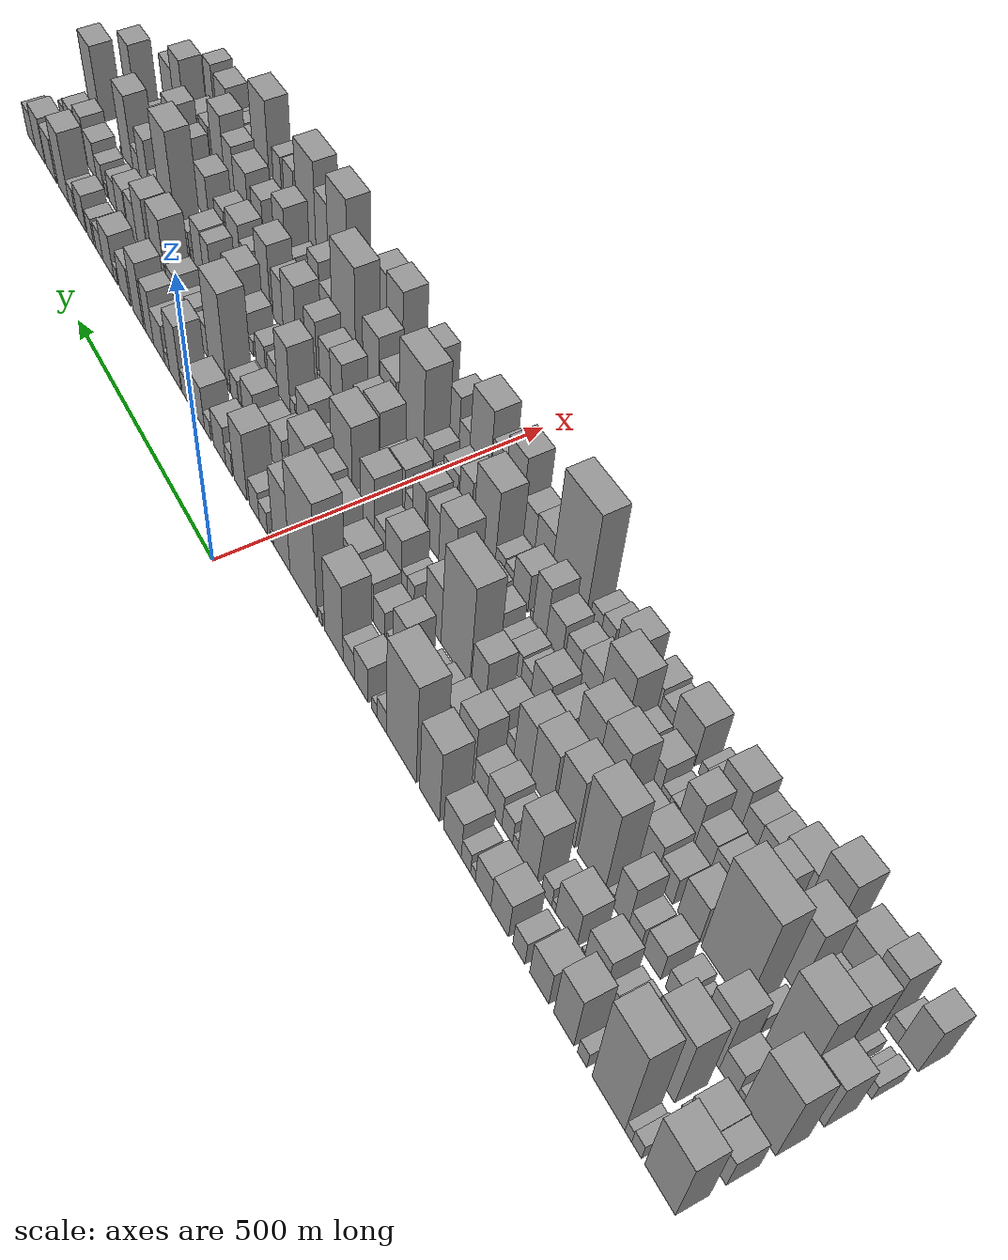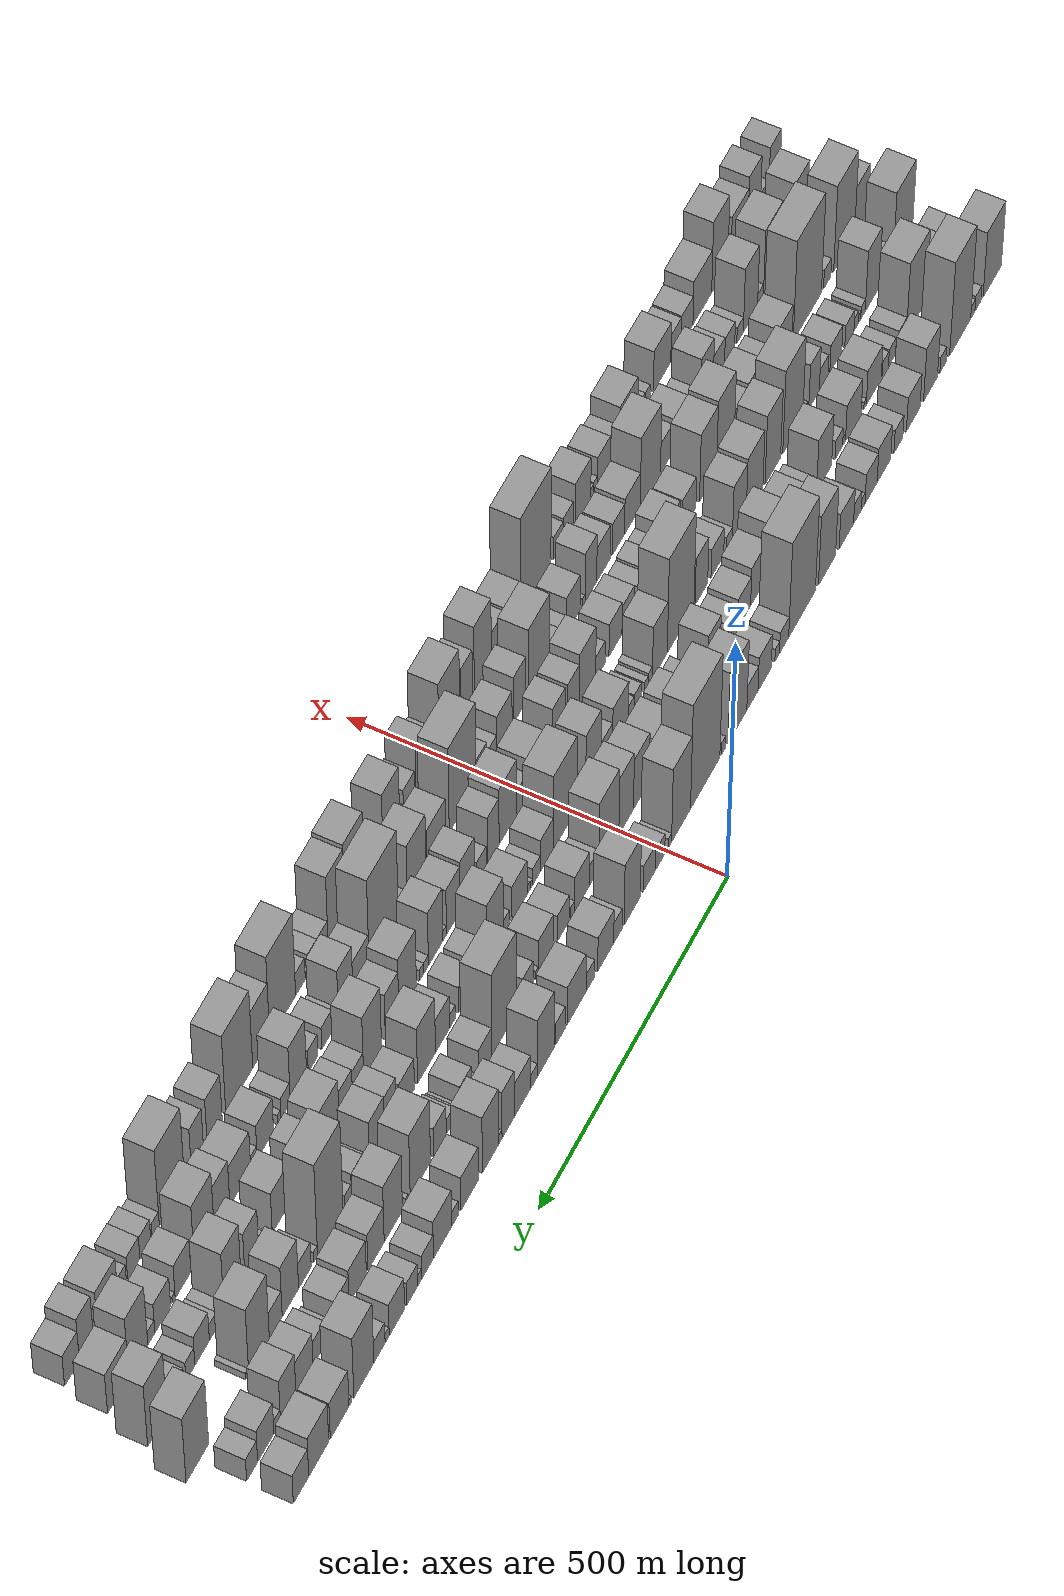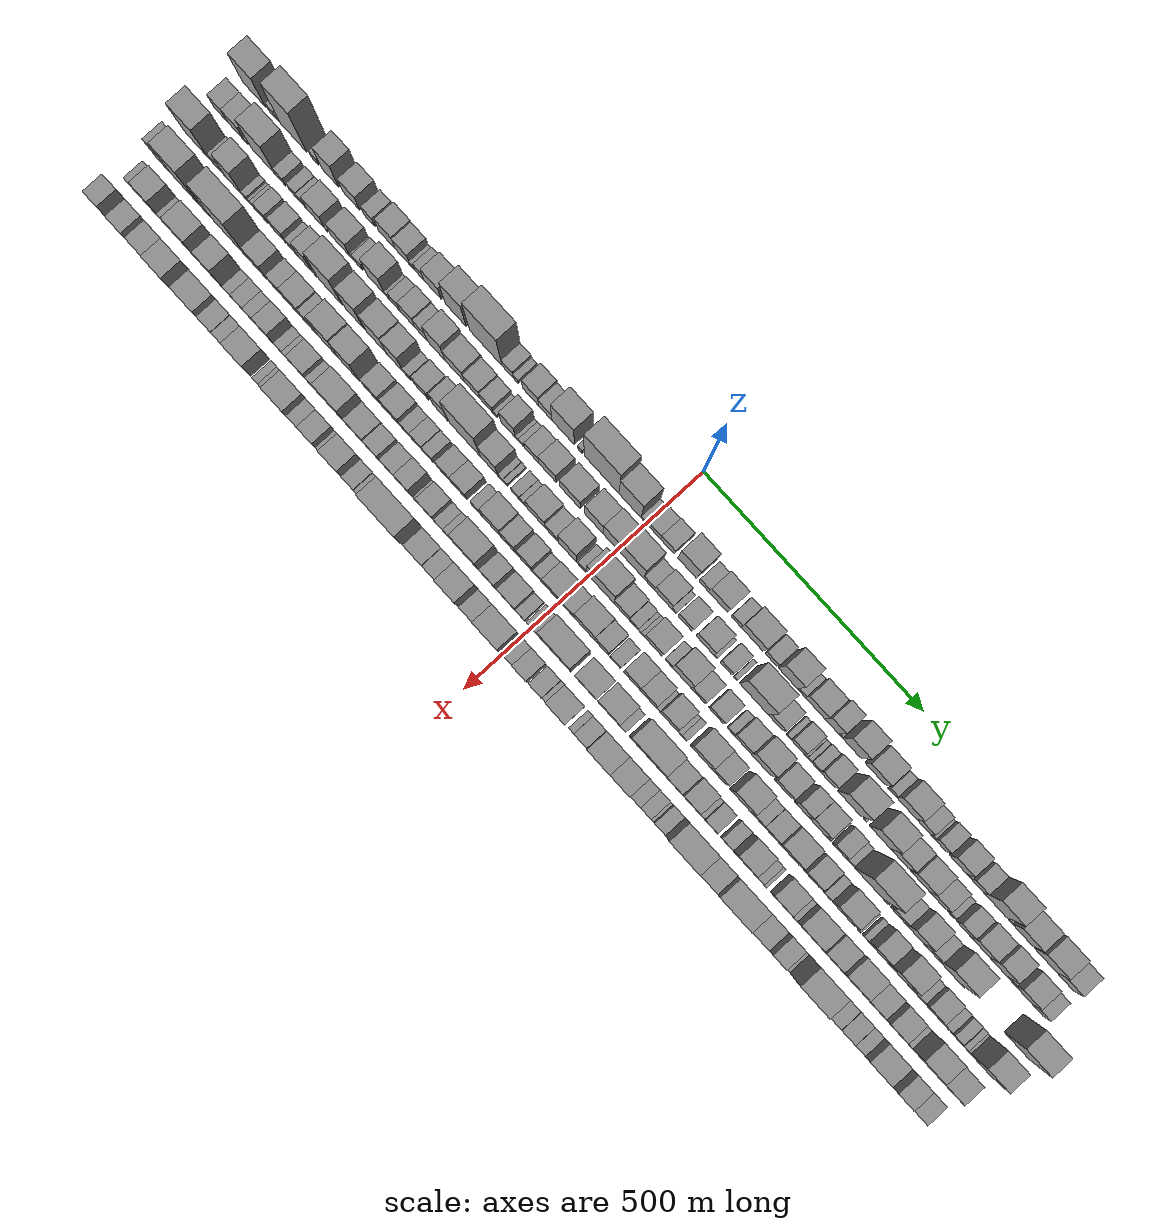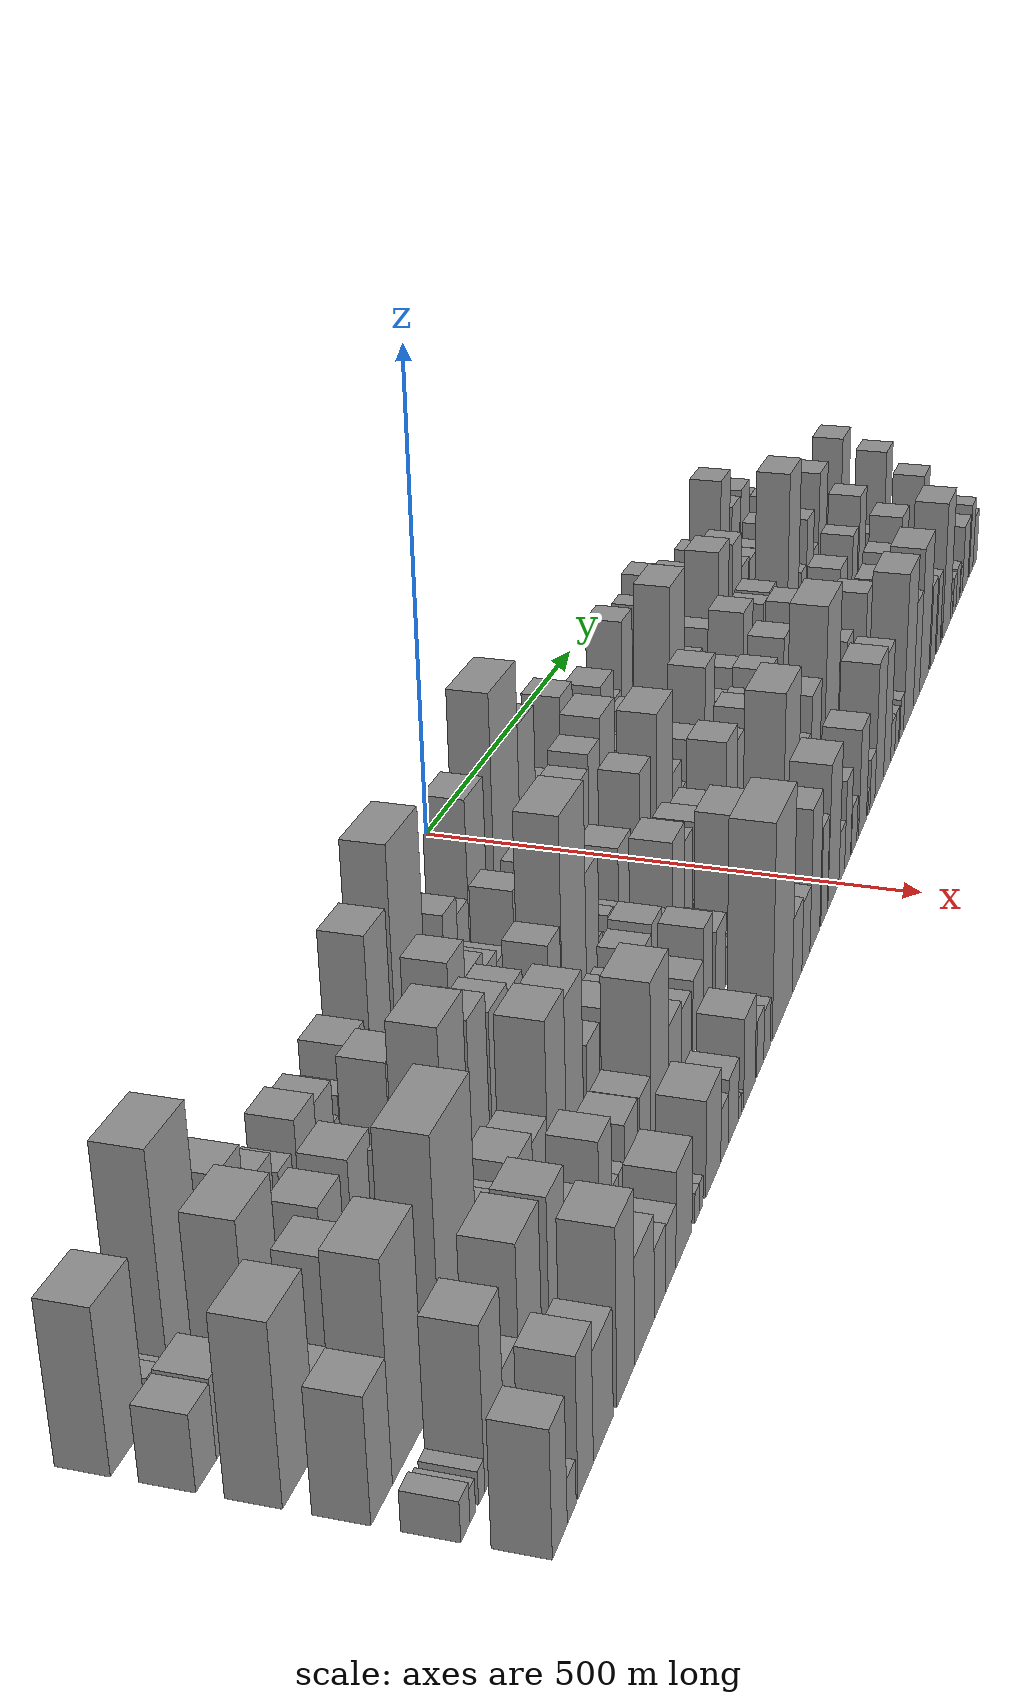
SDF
<sdf version="1.6">
 <world name="default">
  <scene>
   <sky><clouds><speed>12</speed></clouds></sky>
   <ambient>0.4 0.4 0.4 1</ambient>
   <background>0.7 0.7 0.7 1</background>
   <shadows>1</shadows>
  </scene>
  <gravity>0 0 -9.8066</gravity>
  <magnetic_field>6e-06 2.3e-05 -4.2e-05</magnetic_field>
  <physics default="0" name="default_physics" type="ode">
   <ode>
    <solver>
     <type>quick</type>
     <iters>10</iters>
     <sor>1.0</sor>
     <use_dynamic_moi_rescaling>0</use_dynamic_moi_rescaling>
    </solver>
    <constraints>
     <cfm>0</cfm>
     <erp>0.2</erp>
     <contact_max_correcting_vel>100</contact_max_correcting_vel>
     <contact_surface_layer>0.001</contact_surface_layer>
    </constraints>
   </ode>
   <max_step_size>0.004</max_step_size>
   <real_time_factor>1</real_time_factor>
   <real_time_update_rate>250</real_time_update_rate>
  </physics>
  <light name="sun" type="directional">
   <pose>0 0 10 0 0 0</pose>
   <diffuse>0.8 0.8 0.8 1</diffuse>
   <specular>0.2 0.2 0.2 1</specular>
   <attenuation>
    <range>1000</range>
    <constant>0.9</constant>
    <linear>0.01</linear>
    <quadratic>0.001</quadratic>
   </attenuation>
   <direction>-0.5 0.1 -0.9</direction>
  </light>
  <model name="building_1">
   <static>1</static>
   <pose>100.0000 -913.3014 0 0.000000 0.000000 0.000000</pose>
   <link name="link">
    <pose>0 0 67.50 0 0 0</pose>
    <collision name="collision"><geometry><box><size>40.0000 53.3973 135.0000</size></box></geometry></collision>
    <visual name="visual">
     <cast_shadows>0</cast_shadows>
     <geometry><box><size>40.0000 53.3973 135.0000</size></box></geometry>
     <material>
      <script>
       <uri>model://grey_wall/materials/scripts</uri>
       <uri>model://grey_wall/materials/textures</uri>
       <name>vrc/grey_wall</name>
      </script>
     </material>
    </visual>
   </link>
  </model>
  <model name="building_2">
   <static>1</static>
   <pose>100.0000 -871.7648 0 0.000000 0.000000 0.000000</pose>
   <link name="link">
    <pose>0 0 16.50 0 0 0</pose>
    <collision name="collision"><geometry><box><size>40.0000 17.6759 33.0000</size></box></geometry></collision>
    <visual name="visual">
     <cast_shadows>0</cast_shadows>
     <geometry><box><size>40.0000 17.6759 33.0000</size></box></geometry>
     <material>
      <script>
       <uri>model://grey_wall/materials/scripts</uri>
       <uri>model://grey_wall/materials/textures</uri>
       <name>vrc/grey_wall</name>
      </script>
     </material>
    </visual>
   </link>
  </model>
  <model name="building_3">
   <static>1</static>
   <pose>100.0000 -856.7530 0 0.000000 0.000000 0.000000</pose>
   <link name="link">
    <pose>0 0 13.50 0 0 0</pose>
    <collision name="collision"><geometry><box><size>40.0000 12.3477 27.0000</size></box></geometry></collision>
    <visual name="visual">
     <cast_shadows>0</cast_shadows>
     <geometry><box><size>40.0000 12.3477 27.0000</size></box></geometry>
     <material>
      <script>
       <uri>model://grey_wall/materials/scripts</uri>
       <uri>model://grey_wall/materials/textures</uri>
       <name>vrc/grey_wall</name>
      </script>
     </material>
    </visual>
   </link>
  </model>
  <model name="building_4">
   <static>1</static>
   <pose>100.0000 -819.9749 0 0.000000 0.000000 0.000000</pose>
   <link name="link">
    <pose>0 0 97.50 0 0 0</pose>
    <collision name="collision"><geometry><box><size>40.0000 61.2084 195.0000</size></box></geometry></collision>
    <visual name="visual">
     <cast_shadows>0</cast_shadows>
     <geometry><box><size>40.0000 61.2084 195.0000</size></box></geometry>
     <material>
      <script>
       <uri>model://grey_wall/materials/scripts</uri>
       <uri>model://grey_wall/materials/textures</uri>
       <name>vrc/grey_wall</name>
      </script>
     </material>
    </visual>
   </link>
  </model>
  <model name="building_5">
   <static>1</static>
   <pose>100.0000 -770.3430 0 0.000000 0.000000 0.000000</pose>
   <link name="link">
    <pose>0 0 16.50 0 0 0</pose>
    <collision name="collision"><geometry><box><size>40.0000 18.0554 33.0000</size></box></geometry></collision>
    <visual name="visual">
     <cast_shadows>0</cast_shadows>
     <geometry><box><size>40.0000 18.0554 33.0000</size></box></geometry>
     <material>
      <script>
       <uri>model://grey_wall/materials/scripts</uri>
       <uri>model://grey_wall/materials/textures</uri>
       <name>vrc/grey_wall</name>
      </script>
     </material>
    </visual>
   </link>
  </model>
  <model name="building_6">
   <static>1</static>
   <pose>100.0000 -734.3224 0 0.000000 0.000000 0.000000</pose>
   <link name="link">
    <pose>0 0 55.50 0 0 0</pose>
    <collision name="collision"><geometry><box><size>40.0000 39.9858 111.0000</size></box></geometry></collision>
    <visual name="visual">
     <cast_shadows>0</cast_shadows>
     <geometry><box><size>40.0000 39.9858 111.0000</size></box></geometry>
     <material>
      <script>
       <uri>model://grey_wall/materials/scripts</uri>
       <uri>model://grey_wall/materials/textures</uri>
       <name>vrc/grey_wall</name>
      </script>
     </material>
    </visual>
   </link>
  </model>
  <model name="building_7">
   <static>1</static>
   <pose>100.0000 -684.7469 0 0.000000 0.000000 0.000000</pose>
   <link name="link">
    <pose>0 0 36.00 0 0 0</pose>
    <collision name="collision"><geometry><box><size>40.0000 39.1653 72.0000</size></box></geometry></collision>
    <visual name="visual">
     <cast_shadows>0</cast_shadows>
     <geometry><box><size>40.0000 39.1653 72.0000</size></box></geometry>
     <material>
      <script>
       <uri>model://grey_wall/materials/scripts</uri>
       <uri>model://grey_wall/materials/textures</uri>
       <name>vrc/grey_wall</name>
      </script>
     </material>
    </visual>
   </link>
  </model>
  <model name="building_8">
   <static>1</static>
   <pose>100.0000 -642.3426 0 0.000000 0.000000 0.000000</pose>
   <link name="link">
    <pose>0 0 24.00 0 0 0</pose>
    <collision name="collision"><geometry><box><size>40.0000 25.6432 48.0000</size></box></geometry></collision>
    <visual name="visual">
     <cast_shadows>0</cast_shadows>
     <geometry><box><size>40.0000 25.6432 48.0000</size></box></geometry>
     <material>
      <script>
       <uri>model://grey_wall/materials/scripts</uri>
       <uri>model://grey_wall/materials/textures</uri>
       <name>vrc/grey_wall</name>
      </script>
     </material>
    </visual>
   </link>
  </model>
  <model name="building_9">
   <static>1</static>
   <pose>100.0000 -601.1429 0 0.000000 0.000000 0.000000</pose>
   <link name="link">
    <pose>0 0 36.00 0 0 0</pose>
    <collision name="collision"><geometry><box><size>40.0000 38.7562 72.0000</size></box></geometry></collision>
    <visual name="visual">
     <cast_shadows>0</cast_shadows>
     <geometry><box><size>40.0000 38.7562 72.0000</size></box></geometry>
     <material>
      <script>
       <uri>model://grey_wall/materials/scripts</uri>
       <uri>model://grey_wall/materials/textures</uri>
       <name>vrc/grey_wall</name>
      </script>
     </material>
    </visual>
   </link>
  </model>
  <model name="building_10">
   <static>1</static>
   <pose>100.0000 -564.5531 0 0.000000 0.000000 0.000000</pose>
   <link name="link">
    <pose>0 0 31.50 0 0 0</pose>
    <collision name="collision"><geometry><box><size>40.0000 34.4234 63.0000</size></box></geometry></collision>
    <visual name="visual">
     <cast_shadows>0</cast_shadows>
     <geometry><box><size>40.0000 34.4234 63.0000</size></box></geometry>
     <material>
      <script>
       <uri>model://grey_wall/materials/scripts</uri>
       <uri>model://grey_wall/materials/textures</uri>
       <name>vrc/grey_wall</name>
      </script>
     </material>
    </visual>
   </link>
  </model>
  <model name="building_11">
   <static>1</static>
   <pose>100.0000 -541.8997 0 0.000000 0.000000 0.000000</pose>
   <link name="link">
    <pose>0 0 12.00 0 0 0</pose>
    <collision name="collision"><geometry><box><size>40.0000 10.8833 24.0000</size></box></geometry></collision>
    <visual name="visual">
     <cast_shadows>0</cast_shadows>
     <geometry><box><size>40.0000 10.8833 24.0000</size></box></geometry>
     <material>
      <script>
       <uri>model://grey_wall/materials/scripts</uri>
       <uri>model://grey_wall/materials/textures</uri>
       <name>vrc/grey_wall</name>
      </script>
     </material>
    </visual>
   </link>
  </model>
  <model name="building_12">
   <static>1</static>
   <pose>100.0000 -525.7774 0 0.000000 0.000000 0.000000</pose>
   <link name="link">
    <pose>0 0 21.00 0 0 0</pose>
    <collision name="collision"><geometry><box><size>40.0000 21.3615 42.0000</size></box></geometry></collision>
    <visual name="visual">
     <cast_shadows>0</cast_shadows>
     <geometry><box><size>40.0000 21.3615 42.0000</size></box></geometry>
     <material>
      <script>
       <uri>model://grey_wall/materials/scripts</uri>
       <uri>model://grey_wall/materials/textures</uri>
       <name>vrc/grey_wall</name>
      </script>
     </material>
    </visual>
   </link>
  </model>
  <model name="building_13">
   <static>1</static>
   <pose>100.0000 -494.7226 0 0.000000 0.000000 0.000000</pose>
   <link name="link">
    <pose>0 0 37.50 0 0 0</pose>
    <collision name="collision"><geometry><box><size>40.0000 40.7482 75.0000</size></box></geometry></collision>
    <visual name="visual">
     <cast_shadows>0</cast_shadows>
     <geometry><box><size>40.0000 40.7482 75.0000</size></box></geometry>
     <material>
      <script>
       <uri>model://grey_wall/materials/scripts</uri>
       <uri>model://grey_wall/materials/textures</uri>
       <name>vrc/grey_wall</name>
      </script>
     </material>
    </visual>
   </link>
  </model>
  <model name="building_14">
   <static>1</static>
   <pose>100.0000 -440.2460 0 0.000000 0.000000 0.000000</pose>
   <link name="link">
    <pose>0 0 73.50 0 0 0</pose>
    <collision name="collision"><geometry><box><size>40.0000 48.2050 147.0000</size></box></geometry></collision>
    <visual name="visual">
     <cast_shadows>0</cast_shadows>
     <geometry><box><size>40.0000 48.2050 147.0000</size></box></geometry>
     <material>
      <script>
       <uri>model://grey_wall/materials/scripts</uri>
       <uri>model://grey_wall/materials/textures</uri>
       <name>vrc/grey_wall</name>
      </script>
     </material>
    </visual>
   </link>
  </model>
  <model name="building_15">
   <static>1</static>
   <pose>100.0000 -370.8228 0 0.000000 0.000000 0.000000</pose>
   <link name="link">
    <pose>0 0 100.50 0 0 0</pose>
    <collision name="collision"><geometry><box><size>40.0000 74.6413 201.0000</size></box></geometry></collision>
    <visual name="visual">
     <cast_shadows>0</cast_shadows>
     <geometry><box><size>40.0000 74.6413 201.0000</size></box></geometry>
     <material>
      <script>
       <uri>model://grey_wall/materials/scripts</uri>
       <uri>model://grey_wall/materials/textures</uri>
       <name>vrc/grey_wall</name>
      </script>
     </material>
    </visual>
   </link>
  </model>
  <model name="building_16">
   <static>1</static>
   <pose>100.0000 -320.7585 0 0.000000 0.000000 0.000000</pose>
   <link name="link">
    <pose>0 0 22.50 0 0 0</pose>
    <collision name="collision"><geometry><box><size>40.0000 25.4874 45.0000</size></box></geometry></collision>
    <visual name="visual">
     <cast_shadows>0</cast_shadows>
     <geometry><box><size>40.0000 25.4874 45.0000</size></box></geometry>
     <material>
      <script>
       <uri>model://grey_wall/materials/scripts</uri>
       <uri>model://grey_wall/materials/textures</uri>
       <name>vrc/grey_wall</name>
      </script>
     </material>
    </visual>
   </link>
  </model>
  <model name="building_17">
   <static>1</static>
   <pose>100.0000 -301.6495 0 0.000000 0.000000 0.000000</pose>
   <link name="link">
    <pose>0 0 13.50 0 0 0</pose>
    <collision name="collision"><geometry><box><size>40.0000 12.7305 27.0000</size></box></geometry></collision>
    <visual name="visual">
     <cast_shadows>0</cast_shadows>
     <geometry><box><size>40.0000 12.7305 27.0000</size></box></geometry>
     <material>
      <script>
       <uri>model://grey_wall/materials/scripts</uri>
       <uri>model://grey_wall/materials/textures</uri>
       <name>vrc/grey_wall</name>
      </script>
     </material>
    </visual>
   </link>
  </model>
  <model name="building_18">
   <static>1</static>
   <pose>100.0000 -267.0045 0 0.000000 0.000000 0.000000</pose>
   <link name="link">
    <pose>0 0 36.00 0 0 0</pose>
    <collision name="collision"><geometry><box><size>40.0000 36.5595 72.0000</size></box></geometry></collision>
    <visual name="visual">
     <cast_shadows>0</cast_shadows>
     <geometry><box><size>40.0000 36.5595 72.0000</size></box></geometry>
     <material>
      <script>
       <uri>model://grey_wall/materials/scripts</uri>
       <uri>model://grey_wall/materials/textures</uri>
       <name>vrc/grey_wall</name>
      </script>
     </material>
    </visual>
   </link>
  </model>
  <model name="building_19">
   <static>1</static>
   <pose>100.0000 -233.3012 0 0.000000 0.000000 0.000000</pose>
   <link name="link">
    <pose>0 0 27.00 0 0 0</pose>
    <collision name="collision"><geometry><box><size>40.0000 30.8471 54.0000</size></box></geometry></collision>
    <visual name="visual">
     <cast_shadows>0</cast_shadows>
     <geometry><box><size>40.0000 30.8471 54.0000</size></box></geometry>
     <material>
      <script>
       <uri>model://grey_wall/materials/scripts</uri>
       <uri>model://grey_wall/materials/textures</uri>
       <name>vrc/grey_wall</name>
      </script>
     </material>
    </visual>
   </link>
  </model>
  <model name="building_20">
   <static>1</static>
   <pose>100.0000 -192.1349 0 0.000000 0.000000 0.000000</pose>
   <link name="link">
    <pose>0 0 76.50 0 0 0</pose>
    <collision name="collision"><geometry><box><size>40.0000 51.4855 153.0000</size></box></geometry></collision>
    <visual name="visual">
     <cast_shadows>0</cast_shadows>
     <geometry><box><size>40.0000 51.4855 153.0000</size></box></geometry>
     <material>
      <script>
       <uri>model://grey_wall/materials/scripts</uri>
       <uri>model://grey_wall/materials/textures</uri>
       <name>vrc/grey_wall</name>
      </script>
     </material>
    </visual>
   </link>
  </model>
  <model name="building_21">
   <static>1</static>
   <pose>100.0000 -153.6914 0 0.000000 0.000000 0.000000</pose>
   <link name="link">
    <pose>0 0 13.50 0 0 0</pose>
    <collision name="collision"><geometry><box><size>40.0000 11.4014 27.0000</size></box></geometry></collision>
    <visual name="visual">
     <cast_shadows>0</cast_shadows>
     <geometry><box><size>40.0000 11.4014 27.0000</size></box></geometry>
     <material>
      <script>
       <uri>model://grey_wall/materials/scripts</uri>
       <uri>model://grey_wall/materials/textures</uri>
       <name>vrc/grey_wall</name>
      </script>
     </material>
    </visual>
   </link>
  </model>
  <model name="building_22">
   <static>1</static>
   <pose>100.0000 -104.1295 0 0.000000 0.000000 0.000000</pose>
   <link name="link">
    <pose>0 0 112.50 0 0 0</pose>
    <collision name="collision"><geometry><box><size>40.0000 79.7223 225.0000</size></box></geometry></collision>
    <visual name="visual">
     <cast_shadows>0</cast_shadows>
     <geometry><box><size>40.0000 79.7223 225.0000</size></box></geometry>
     <material>
      <script>
       <uri>model://grey_wall/materials/scripts</uri>
       <uri>model://grey_wall/materials/textures</uri>
       <name>vrc/grey_wall</name>
      </script>
     </material>
    </visual>
   </link>
  </model>
  <model name="building_23">
   <static>1</static>
   <pose>100.0000 -38.7275 0 0.000000 0.000000 0.000000</pose>
   <link name="link">
    <pose>0 0 79.50 0 0 0</pose>
    <collision name="collision"><geometry><box><size>40.0000 51.0818 159.0000</size></box></geometry></collision>
    <visual name="visual">
     <cast_shadows>0</cast_shadows>
     <geometry><box><size>40.0000 51.0818 159.0000</size></box></geometry>
     <material>
      <script>
       <uri>model://grey_wall/materials/scripts</uri>
       <uri>model://grey_wall/materials/textures</uri>
       <name>vrc/grey_wall</name>
      </script>
     </material>
    </visual>
   </link>
  </model>
  <model name="building_24">
   <static>1</static>
   <pose>100.0000 -8.4285 0 0.000000 0.000000 0.000000</pose>
   <link name="link">
    <pose>0 0 10.50 0 0 0</pose>
    <collision name="collision"><geometry><box><size>40.0000 9.5163 21.0000</size></box></geometry></collision>
    <visual name="visual">
     <cast_shadows>0</cast_shadows>
     <geometry><box><size>40.0000 9.5163 21.0000</size></box></geometry>
     <material>
      <script>
       <uri>model://grey_wall/materials/scripts</uri>
       <uri>model://grey_wall/materials/textures</uri>
       <name>vrc/grey_wall</name>
      </script>
     </material>
    </visual>
   </link>
  </model>
  <model name="building_25">
   <static>1</static>
   <pose>100.0000 18.3383 0 0.000000 0.000000 0.000000</pose>
   <link name="link">
    <pose>0 0 22.50 0 0 0</pose>
    <collision name="collision"><geometry><box><size>40.0000 26.0173 45.0000</size></box></geometry></collision>
    <visual name="visual">
     <cast_shadows>0</cast_shadows>
     <geometry><box><size>40.0000 26.0173 45.0000</size></box></geometry>
     <material>
      <script>
       <uri>model://grey_wall/materials/scripts</uri>
       <uri>model://grey_wall/materials/textures</uri>
       <name>vrc/grey_wall</name>
      </script>
     </material>
    </visual>
   </link>
  </model>
  <model name="building_26">
   <static>1</static>
   <pose>100.0000 47.0992 0 0.000000 0.000000 0.000000</pose>
   <link name="link">
    <pose>0 0 28.50 0 0 0</pose>
    <collision name="collision"><geometry><box><size>40.0000 31.5045 57.0000</size></box></geometry></collision>
    <visual name="visual">
     <cast_shadows>0</cast_shadows>
     <geometry><box><size>40.0000 31.5045 57.0000</size></box></geometry>
     <material>
      <script>
       <uri>model://grey_wall/materials/scripts</uri>
       <uri>model://grey_wall/materials/textures</uri>
       <name>vrc/grey_wall</name>
      </script>
     </material>
    </visual>
   </link>
  </model>
  <model name="building_27">
   <static>1</static>
   <pose>100.0000 92.4159 0 0.000000 0.000000 0.000000</pose>
   <link name="link">
    <pose>0 0 66.00 0 0 0</pose>
    <collision name="collision"><geometry><box><size>40.0000 43.1290 132.0000</size></box></geometry></collision>
    <visual name="visual">
     <cast_shadows>0</cast_shadows>
     <geometry><box><size>40.0000 43.1290 132.0000</size></box></geometry>
     <material>
      <script>
       <uri>model://grey_wall/materials/scripts</uri>
       <uri>model://grey_wall/materials/textures</uri>
       <name>vrc/grey_wall</name>
      </script>
     </material>
    </visual>
   </link>
  </model>
  <model name="building_28">
   <static>1</static>
   <pose>100.0000 130.3424 0 0.000000 0.000000 0.000000</pose>
   <link name="link">
    <pose>0 0 22.50 0 0 0</pose>
    <collision name="collision"><geometry><box><size>40.0000 22.7241 45.0000</size></box></geometry></collision>
    <visual name="visual">
     <cast_shadows>0</cast_shadows>
     <geometry><box><size>40.0000 22.7241 45.0000</size></box></geometry>
     <material>
      <script>
       <uri>model://grey_wall/materials/scripts</uri>
       <uri>model://grey_wall/materials/textures</uri>
       <name>vrc/grey_wall</name>
      </script>
     </material>
    </visual>
   </link>
  </model>
  <model name="building_29">
   <static>1</static>
   <pose>100.0000 162.9192 0 0.000000 0.000000 0.000000</pose>
   <link name="link">
    <pose>0 0 37.50 0 0 0</pose>
    <collision name="collision"><geometry><box><size>40.0000 42.4296 75.0000</size></box></geometry></collision>
    <visual name="visual">
     <cast_shadows>0</cast_shadows>
     <geometry><box><size>40.0000 42.4296 75.0000</size></box></geometry>
     <material>
      <script>
       <uri>model://grey_wall/materials/scripts</uri>
       <uri>model://grey_wall/materials/textures</uri>
       <name>vrc/grey_wall</name>
      </script>
     </material>
    </visual>
   </link>
  </model>
  <model name="building_30">
   <static>1</static>
   <pose>100.0000 203.5021 0 0.000000 0.000000 0.000000</pose>
   <link name="link">
    <pose>0 0 19.50 0 0 0</pose>
    <collision name="collision"><geometry><box><size>40.0000 22.7361 39.0000</size></box></geometry></collision>
    <visual name="visual">
     <cast_shadows>0</cast_shadows>
     <geometry><box><size>40.0000 22.7361 39.0000</size></box></geometry>
     <material>
      <script>
       <uri>model://grey_wall/materials/scripts</uri>
       <uri>model://grey_wall/materials/textures</uri>
       <name>vrc/grey_wall</name>
      </script>
     </material>
    </visual>
   </link>
  </model>
  <model name="building_31">
   <static>1</static>
   <pose>100.0000 239.9030 0 0.000000 0.000000 0.000000</pose>
   <link name="link">
    <pose>0 0 42.00 0 0 0</pose>
    <collision name="collision"><geometry><box><size>40.0000 50.0657 84.0000</size></box></geometry></collision>
    <visual name="visual">
     <cast_shadows>0</cast_shadows>
     <geometry><box><size>40.0000 50.0657 84.0000</size></box></geometry>
     <material>
      <script>
       <uri>model://grey_wall/materials/scripts</uri>
       <uri>model://grey_wall/materials/textures</uri>
       <name>vrc/grey_wall</name>
      </script>
     </material>
    </visual>
   </link>
  </model>
  <model name="building_32">
   <static>1</static>
   <pose>100.0000 282.4379 0 0.000000 0.000000 0.000000</pose>
   <link name="link">
    <pose>0 0 24.00 0 0 0</pose>
    <collision name="collision"><geometry><box><size>40.0000 27.0040 48.0000</size></box></geometry></collision>
    <visual name="visual">
     <cast_shadows>0</cast_shadows>
     <geometry><box><size>40.0000 27.0040 48.0000</size></box></geometry>
     <material>
      <script>
       <uri>model://grey_wall/materials/scripts</uri>
       <uri>model://grey_wall/materials/textures</uri>
       <name>vrc/grey_wall</name>
      </script>
     </material>
    </visual>
   </link>
  </model>
  <model name="building_33">
   <static>1</static>
   <pose>100.0000 320.5855 0 0.000000 0.000000 0.000000</pose>
   <link name="link">
    <pose>0 0 63.00 0 0 0</pose>
    <collision name="collision"><geometry><box><size>40.0000 43.2914 126.0000</size></box></geometry></collision>
    <visual name="visual">
     <cast_shadows>0</cast_shadows>
     <geometry><box><size>40.0000 43.2914 126.0000</size></box></geometry>
     <material>
      <script>
       <uri>model://grey_wall/materials/scripts</uri>
       <uri>model://grey_wall/materials/textures</uri>
       <name>vrc/grey_wall</name>
      </script>
     </material>
    </visual>
   </link>
  </model>
  <model name="building_34">
   <static>1</static>
   <pose>100.0000 351.0756 0 0.000000 0.000000 0.000000</pose>
   <link name="link">
    <pose>0 0 15.00 0 0 0</pose>
    <collision name="collision"><geometry><box><size>40.0000 17.6887 30.0000</size></box></geometry></collision>
    <visual name="visual">
     <cast_shadows>0</cast_shadows>
     <geometry><box><size>40.0000 17.6887 30.0000</size></box></geometry>
     <material>
      <script>
       <uri>model://grey_wall/materials/scripts</uri>
       <uri>model://grey_wall/materials/textures</uri>
       <name>vrc/grey_wall</name>
      </script>
     </material>
    </visual>
   </link>
  </model>
  <model name="building_35">
   <static>1</static>
   <pose>100.0000 381.4709 0 0.000000 0.000000 0.000000</pose>
   <link name="link">
    <pose>0 0 37.50 0 0 0</pose>
    <collision name="collision"><geometry><box><size>40.0000 43.1019 75.0000</size></box></geometry></collision>
    <visual name="visual">
     <cast_shadows>0</cast_shadows>
     <geometry><box><size>40.0000 43.1019 75.0000</size></box></geometry>
     <material>
      <script>
       <uri>model://grey_wall/materials/scripts</uri>
       <uri>model://grey_wall/materials/textures</uri>
       <name>vrc/grey_wall</name>
      </script>
     </material>
    </visual>
   </link>
  </model>
  <model name="building_36">
   <static>1</static>
   <pose>100.0000 418.7863 0 0.000000 0.000000 0.000000</pose>
   <link name="link">
    <pose>0 0 52.50 0 0 0</pose>
    <collision name="collision"><geometry><box><size>40.0000 31.5288 105.0000</size></box></geometry></collision>
    <visual name="visual">
     <cast_shadows>0</cast_shadows>
     <geometry><box><size>40.0000 31.5288 105.0000</size></box></geometry>
     <material>
      <script>
       <uri>model://grey_wall/materials/scripts</uri>
       <uri>model://grey_wall/materials/textures</uri>
       <name>vrc/grey_wall</name>
      </script>
     </material>
    </visual>
   </link>
  </model>
  <model name="building_37">
   <static>1</static>
   <pose>100.0000 438.9979 0 0.000000 0.000000 0.000000</pose>
   <link name="link">
    <pose>0 0 10.50 0 0 0</pose>
    <collision name="collision"><geometry><box><size>40.0000 8.8945 21.0000</size></box></geometry></collision>
    <visual name="visual">
     <cast_shadows>0</cast_shadows>
     <geometry><box><size>40.0000 8.8945 21.0000</size></box></geometry>
     <material>
      <script>
       <uri>model://grey_wall/materials/scripts</uri>
       <uri>model://grey_wall/materials/textures</uri>
       <name>vrc/grey_wall</name>
      </script>
     </material>
    </visual>
   </link>
  </model>
  <model name="building_38">
   <static>1</static>
   <pose>100.0000 464.3143 0 0.000000 0.000000 0.000000</pose>
   <link name="link">
    <pose>0 0 63.00 0 0 0</pose>
    <collision name="collision"><geometry><box><size>40.0000 41.7383 126.0000</size></box></geometry></collision>
    <visual name="visual">
     <cast_shadows>0</cast_shadows>
     <geometry><box><size>40.0000 41.7383 126.0000</size></box></geometry>
     <material>
      <script>
       <uri>model://grey_wall/materials/scripts</uri>
       <uri>model://grey_wall/materials/textures</uri>
       <name>vrc/grey_wall</name>
      </script>
     </material>
    </visual>
   </link>
  </model>
  <model name="building_39">
   <static>1</static>
   <pose>100.0000 517.6695 0 0.000000 0.000000 0.000000</pose>
   <link name="link">
    <pose>0 0 37.50 0 0 0</pose>
    <collision name="collision"><geometry><box><size>40.0000 44.9721 75.0000</size></box></geometry></collision>
    <visual name="visual">
     <cast_shadows>0</cast_shadows>
     <geometry><box><size>40.0000 44.9721 75.0000</size></box></geometry>
     <material>
      <script>
       <uri>model://grey_wall/materials/scripts</uri>
       <uri>model://grey_wall/materials/textures</uri>
       <name>vrc/grey_wall</name>
      </script>
     </material>
    </visual>
   </link>
  </model>
  <model name="building_40">
   <static>1</static>
   <pose>100.0000 555.5803 0 0.000000 0.000000 0.000000</pose>
   <link name="link">
    <pose>0 0 16.50 0 0 0</pose>
    <collision name="collision"><geometry><box><size>40.0000 16.8495 33.0000</size></box></geometry></collision>
    <visual name="visual">
     <cast_shadows>0</cast_shadows>
     <geometry><box><size>40.0000 16.8495 33.0000</size></box></geometry>
     <material>
      <script>
       <uri>model://grey_wall/materials/scripts</uri>
       <uri>model://grey_wall/materials/textures</uri>
       <name>vrc/grey_wall</name>
      </script>
     </material>
    </visual>
   </link>
  </model>
  <model name="building_41">
   <static>1</static>
   <pose>100.0000 587.2053 0 0.000000 0.000000 0.000000</pose>
   <link name="link">
    <pose>0 0 42.00 0 0 0</pose>
    <collision name="collision"><geometry><box><size>40.0000 46.4006 84.0000</size></box></geometry></collision>
    <visual name="visual">
     <cast_shadows>0</cast_shadows>
     <geometry><box><size>40.0000 46.4006 84.0000</size></box></geometry>
     <material>
      <script>
       <uri>model://grey_wall/materials/scripts</uri>
       <uri>model://grey_wall/materials/textures</uri>
       <name>vrc/grey_wall</name>
      </script>
     </material>
    </visual>
   </link>
  </model>
  <model name="building_42">
   <static>1</static>
   <pose>100.0000 625.5312 0 0.000000 0.000000 0.000000</pose>
   <link name="link">
    <pose>0 0 27.00 0 0 0</pose>
    <collision name="collision"><geometry><box><size>40.0000 30.2512 54.0000</size></box></geometry></collision>
    <visual name="visual">
     <cast_shadows>0</cast_shadows>
     <geometry><box><size>40.0000 30.2512 54.0000</size></box></geometry>
     <material>
      <script>
       <uri>model://grey_wall/materials/scripts</uri>
       <uri>model://grey_wall/materials/textures</uri>
       <name>vrc/grey_wall</name>
      </script>
     </material>
    </visual>
   </link>
  </model>
  <model name="building_43">
   <static>1</static>
   <pose>100.0000 645.5168 0 0.000000 0.000000 0.000000</pose>
   <link name="link">
    <pose>0 0 12.00 0 0 0</pose>
    <collision name="collision"><geometry><box><size>40.0000 9.7201 24.0000</size></box></geometry></collision>
    <visual name="visual">
     <cast_shadows>0</cast_shadows>
     <geometry><box><size>40.0000 9.7201 24.0000</size></box></geometry>
     <material>
      <script>
       <uri>model://grey_wall/materials/scripts</uri>
       <uri>model://grey_wall/materials/textures</uri>
       <name>vrc/grey_wall</name>
      </script>
     </material>
    </visual>
   </link>
  </model>
  <model name="building_44">
   <static>1</static>
   <pose>100.0000 664.0462 0 0.000000 0.000000 0.000000</pose>
   <link name="link">
    <pose>0 0 25.50 0 0 0</pose>
    <collision name="collision"><geometry><box><size>40.0000 27.3386 51.0000</size></box></geometry></collision>
    <visual name="visual">
     <cast_shadows>0</cast_shadows>
     <geometry><box><size>40.0000 27.3386 51.0000</size></box></geometry>
     <material>
      <script>
       <uri>model://grey_wall/materials/scripts</uri>
       <uri>model://grey_wall/materials/textures</uri>
       <name>vrc/grey_wall</name>
      </script>
     </material>
    </visual>
   </link>
  </model>
  <model name="building_45">
   <static>1</static>
   <pose>100.0000 703.0734 0 0.000000 0.000000 0.000000</pose>
   <link name="link">
    <pose>0 0 36.00 0 0 0</pose>
    <collision name="collision"><geometry><box><size>40.0000 38.7160 72.0000</size></box></geometry></collision>
    <visual name="visual">
     <cast_shadows>0</cast_shadows>
     <geometry><box><size>40.0000 38.7160 72.0000</size></box></geometry>
     <material>
      <script>
       <uri>model://grey_wall/materials/scripts</uri>
       <uri>model://grey_wall/materials/textures</uri>
       <name>vrc/grey_wall</name>
      </script>
     </material>
    </visual>
   </link>
  </model>
  <model name="building_46">
   <static>1</static>
   <pose>100.0000 727.5626 0 0.000000 0.000000 0.000000</pose>
   <link name="link">
    <pose>0 0 10.50 0 0 0</pose>
    <collision name="collision"><geometry><box><size>40.0000 10.2623 21.0000</size></box></geometry></collision>
    <visual name="visual">
     <cast_shadows>0</cast_shadows>
     <geometry><box><size>40.0000 10.2623 21.0000</size></box></geometry>
     <material>
      <script>
       <uri>model://grey_wall/materials/scripts</uri>
       <uri>model://grey_wall/materials/textures</uri>
       <name>vrc/grey_wall</name>
      </script>
     </material>
    </visual>
   </link>
  </model>
  <model name="building_47">
   <static>1</static>
   <pose>100.0000 746.8520 0 0.000000 0.000000 0.000000</pose>
   <link name="link">
    <pose>0 0 24.00 0 0 0</pose>
    <collision name="collision"><geometry><box><size>40.0000 28.3164 48.0000</size></box></geometry></collision>
    <visual name="visual">
     <cast_shadows>0</cast_shadows>
     <geometry><box><size>40.0000 28.3164 48.0000</size></box></geometry>
     <material>
      <script>
       <uri>model://grey_wall/materials/scripts</uri>
       <uri>model://grey_wall/materials/textures</uri>
       <name>vrc/grey_wall</name>
      </script>
     </material>
    </visual>
   </link>
  </model>
  <model name="building_48">
   <static>1</static>
   <pose>100.0000 786.0104 0 0.000000 0.000000 0.000000</pose>
   <link name="link">
    <pose>0 0 69.00 0 0 0</pose>
    <collision name="collision"><geometry><box><size>40.0000 50.0005 138.0000</size></box></geometry></collision>
    <visual name="visual">
     <cast_shadows>0</cast_shadows>
     <geometry><box><size>40.0000 50.0005 138.0000</size></box></geometry>
     <material>
      <script>
       <uri>model://grey_wall/materials/scripts</uri>
       <uri>model://grey_wall/materials/textures</uri>
       <name>vrc/grey_wall</name>
      </script>
     </material>
    </visual>
   </link>
  </model>
  <model name="building_49">
   <static>1</static>
   <pose>100.0000 820.0945 0 0.000000 0.000000 0.000000</pose>
   <link name="link">
    <pose>0 0 7.50 0 0 0</pose>
    <collision name="collision"><geometry><box><size>40.0000 6.1677 15.0000</size></box></geometry></collision>
    <visual name="visual">
     <cast_shadows>0</cast_shadows>
     <geometry><box><size>40.0000 6.1677 15.0000</size></box></geometry>
     <material>
      <script>
       <uri>model://grey_wall/materials/scripts</uri>
       <uri>model://grey_wall/materials/textures</uri>
       <name>vrc/grey_wall</name>
      </script>
     </material>
    </visual>
   </link>
  </model>
  <model name="building_50">
   <static>1</static>
   <pose>100.0000 846.4043 0 0.000000 0.000000 0.000000</pose>
   <link name="link">
    <pose>0 0 42.00 0 0 0</pose>
    <collision name="collision"><geometry><box><size>40.0000 46.4519 84.0000</size></box></geometry></collision>
    <visual name="visual">
     <cast_shadows>0</cast_shadows>
     <geometry><box><size>40.0000 46.4519 84.0000</size></box></geometry>
     <material>
      <script>
       <uri>model://grey_wall/materials/scripts</uri>
       <uri>model://grey_wall/materials/textures</uri>
       <name>vrc/grey_wall</name>
      </script>
     </material>
    </visual>
   </link>
  </model>
  <model name="building_51">
   <static>1</static>
   <pose>100.0000 898.2905 0 0.000000 0.000000 0.000000</pose>
   <link name="link">
    <pose>0 0 45.00 0 0 0</pose>
    <collision name="collision"><geometry><box><size>40.0000 49.3204 90.0000</size></box></geometry></collision>
    <visual name="visual">
     <cast_shadows>0</cast_shadows>
     <geometry><box><size>40.0000 49.3204 90.0000</size></box></geometry>
     <material>
      <script>
       <uri>model://grey_wall/materials/scripts</uri>
       <uri>model://grey_wall/materials/textures</uri>
       <name>vrc/grey_wall</name>
      </script>
     </material>
    </visual>
   </link>
  </model>
  <model name="building_52">
   <static>1</static>
   <pose>100.0000 941.9856 0 0.000000 0.000000 0.000000</pose>
   <link name="link">
    <pose>0 0 33.00 0 0 0</pose>
    <collision name="collision"><geometry><box><size>40.0000 38.0699 66.0000</size></box></geometry></collision>
    <visual name="visual">
     <cast_shadows>0</cast_shadows>
     <geometry><box><size>40.0000 38.0699 66.0000</size></box></geometry>
     <material>
      <script>
       <uri>model://grey_wall/materials/scripts</uri>
       <uri>model://grey_wall/materials/textures</uri>
       <name>vrc/grey_wall</name>
      </script>
     </material>
    </visual>
   </link>
  </model>
  <model name="building_53">
   <static>1</static>
   <pose>160.0000 -923.9173 0 0.000000 0.000000 0.000000</pose>
   <link name="link">
    <pose>0 0 31.50 0 0 0</pose>
    <collision name="collision"><geometry><box><size>40.0000 32.1654 63.0000</size></box></geometry></collision>
    <visual name="visual">
     <cast_shadows>0</cast_shadows>
     <geometry><box><size>40.0000 32.1654 63.0000</size></box></geometry>
     <material>
      <script>
       <uri>model://grey_wall/materials/scripts</uri>
       <uri>model://grey_wall/materials/textures</uri>
       <name>vrc/grey_wall</name>
      </script>
     </material>
    </visual>
   </link>
  </model>
  <model name="building_54">
   <static>1</static>
   <pose>160.0000 -888.2326 0 0.000000 0.000000 0.000000</pose>
   <link name="link">
    <pose>0 0 33.00 0 0 0</pose>
    <collision name="collision"><geometry><box><size>40.0000 39.2041 66.0000</size></box></geometry></collision>
    <visual name="visual">
     <cast_shadows>0</cast_shadows>
     <geometry><box><size>40.0000 39.2041 66.0000</size></box></geometry>
     <material>
      <script>
       <uri>model://grey_wall/materials/scripts</uri>
       <uri>model://grey_wall/materials/textures</uri>
       <name>vrc/grey_wall</name>
      </script>
     </material>
    </visual>
   </link>
  </model>
  <model name="building_55">
   <static>1</static>
   <pose>160.0000 -864.2498 0 0.000000 0.000000 0.000000</pose>
   <link name="link">
    <pose>0 0 9.00 0 0 0</pose>
    <collision name="collision"><geometry><box><size>40.0000 8.7616 18.0000</size></box></geometry></collision>
    <visual name="visual">
     <cast_shadows>0</cast_shadows>
     <geometry><box><size>40.0000 8.7616 18.0000</size></box></geometry>
     <material>
      <script>
       <uri>model://grey_wall/materials/scripts</uri>
       <uri>model://grey_wall/materials/textures</uri>
       <name>vrc/grey_wall</name>
      </script>
     </material>
    </visual>
   </link>
  </model>
  <model name="building_56">
   <static>1</static>
   <pose>160.0000 -822.3964 0 0.000000 0.000000 0.000000</pose>
   <link name="link">
    <pose>0 0 75.00 0 0 0</pose>
    <collision name="collision"><geometry><box><size>40.0000 56.9450 150.0000</size></box></geometry></collision>
    <visual name="visual">
     <cast_shadows>0</cast_shadows>
     <geometry><box><size>40.0000 56.9450 150.0000</size></box></geometry>
     <material>
      <script>
       <uri>model://grey_wall/materials/scripts</uri>
       <uri>model://grey_wall/materials/textures</uri>
       <name>vrc/grey_wall</name>
      </script>
     </material>
    </visual>
   </link>
  </model>
  <model name="building_57">
   <static>1</static>
   <pose>160.0000 -782.4329 0 0.000000 0.000000 0.000000</pose>
   <link name="link">
    <pose>0 0 19.50 0 0 0</pose>
    <collision name="collision"><geometry><box><size>40.0000 22.9821 39.0000</size></box></geometry></collision>
    <visual name="visual">
     <cast_shadows>0</cast_shadows>
     <geometry><box><size>40.0000 22.9821 39.0000</size></box></geometry>
     <material>
      <script>
       <uri>model://grey_wall/materials/scripts</uri>
       <uri>model://grey_wall/materials/textures</uri>
       <name>vrc/grey_wall</name>
      </script>
     </material>
    </visual>
   </link>
  </model>
  <model name="building_58">
   <static>1</static>
   <pose>160.0000 -752.6674 0 0.000000 0.000000 0.000000</pose>
   <link name="link">
    <pose>0 0 18.00 0 0 0</pose>
    <collision name="collision"><geometry><box><size>40.0000 20.5488 36.0000</size></box></geometry></collision>
    <visual name="visual">
     <cast_shadows>0</cast_shadows>
     <geometry><box><size>40.0000 20.5488 36.0000</size></box></geometry>
     <material>
      <script>
       <uri>model://grey_wall/materials/scripts</uri>
       <uri>model://grey_wall/materials/textures</uri>
       <name>vrc/grey_wall</name>
      </script>
     </material>
    </visual>
   </link>
  </model>
  <model name="building_59">
   <static>1</static>
   <pose>160.0000 -733.4097 0 0.000000 0.000000 0.000000</pose>
   <link name="link">
    <pose>0 0 16.50 0 0 0</pose>
    <collision name="collision"><geometry><box><size>40.0000 17.9665 33.0000</size></box></geometry></collision>
    <visual name="visual">
     <cast_shadows>0</cast_shadows>
     <geometry><box><size>40.0000 17.9665 33.0000</size></box></geometry>
     <material>
      <script>
       <uri>model://grey_wall/materials/scripts</uri>
       <uri>model://grey_wall/materials/textures</uri>
       <name>vrc/grey_wall</name>
      </script>
     </material>
    </visual>
   </link>
  </model>
  <model name="building_60">
   <static>1</static>
   <pose>160.0000 -700.1859 0 0.000000 0.000000 0.000000</pose>
   <link name="link">
    <pose>0 0 36.00 0 0 0</pose>
    <collision name="collision"><geometry><box><size>40.0000 42.4813 72.0000</size></box></geometry></collision>
    <visual name="visual">
     <cast_shadows>0</cast_shadows>
     <geometry><box><size>40.0000 42.4813 72.0000</size></box></geometry>
     <material>
      <script>
       <uri>model://grey_wall/materials/scripts</uri>
       <uri>model://grey_wall/materials/textures</uri>
       <name>vrc/grey_wall</name>
      </script>
     </material>
    </visual>
   </link>
  </model>
  <model name="building_61">
   <static>1</static>
   <pose>160.0000 -675.5092 0 0.000000 0.000000 0.000000</pose>
   <link name="link">
    <pose>0 0 7.50 0 0 0</pose>
    <collision name="collision"><geometry><box><size>40.0000 6.8719 15.0000</size></box></geometry></collision>
    <visual name="visual">
     <cast_shadows>0</cast_shadows>
     <geometry><box><size>40.0000 6.8719 15.0000</size></box></geometry>
     <material>
      <script>
       <uri>model://grey_wall/materials/scripts</uri>
       <uri>model://grey_wall/materials/textures</uri>
       <name>vrc/grey_wall</name>
      </script>
     </material>
    </visual>
   </link>
  </model>
  <model name="building_62">
   <static>1</static>
   <pose>160.0000 -641.9360 0 0.000000 0.000000 0.000000</pose>
   <link name="link">
    <pose>0 0 37.50 0 0 0</pose>
    <collision name="collision"><geometry><box><size>40.0000 44.2746 75.0000</size></box></geometry></collision>
    <visual name="visual">
     <cast_shadows>0</cast_shadows>
     <geometry><box><size>40.0000 44.2746 75.0000</size></box></geometry>
     <material>
      <script>
       <uri>model://grey_wall/materials/scripts</uri>
       <uri>model://grey_wall/materials/textures</uri>
       <name>vrc/grey_wall</name>
      </script>
     </material>
    </visual>
   </link>
  </model>
  <model name="building_63">
   <static>1</static>
   <pose>160.0000 -615.7325 0 0.000000 0.000000 0.000000</pose>
   <link name="link">
    <pose>0 0 9.00 0 0 0</pose>
    <collision name="collision"><geometry><box><size>40.0000 8.1323 18.0000</size></box></geometry></collision>
    <visual name="visual">
     <cast_shadows>0</cast_shadows>
     <geometry><box><size>40.0000 8.1323 18.0000</size></box></geometry>
     <material>
      <script>
       <uri>model://grey_wall/materials/scripts</uri>
       <uri>model://grey_wall/materials/textures</uri>
       <name>vrc/grey_wall</name>
      </script>
     </material>
    </visual>
   </link>
  </model>
  <model name="building_64">
   <static>1</static>
   <pose>160.0000 -601.0917 0 0.000000 0.000000 0.000000</pose>
   <link name="link">
    <pose>0 0 19.50 0 0 0</pose>
    <collision name="collision"><geometry><box><size>40.0000 21.1492 39.0000</size></box></geometry></collision>
    <visual name="visual">
     <cast_shadows>0</cast_shadows>
     <geometry><box><size>40.0000 21.1492 39.0000</size></box></geometry>
     <material>
      <script>
       <uri>model://grey_wall/materials/scripts</uri>
       <uri>model://grey_wall/materials/textures</uri>
       <name>vrc/grey_wall</name>
      </script>
     </material>
    </visual>
   </link>
  </model>
  <model name="building_65">
   <static>1</static>
   <pose>160.0000 -559.3429 0 0.000000 0.000000 0.000000</pose>
   <link name="link">
    <pose>0 0 54.00 0 0 0</pose>
    <collision name="collision"><geometry><box><size>40.0000 42.3483 108.0000</size></box></geometry></collision>
    <visual name="visual">
     <cast_shadows>0</cast_shadows>
     <geometry><box><size>40.0000 42.3483 108.0000</size></box></geometry>
     <material>
      <script>
       <uri>model://grey_wall/materials/scripts</uri>
       <uri>model://grey_wall/materials/textures</uri>
       <name>vrc/grey_wall</name>
      </script>
     </material>
    </visual>
   </link>
  </model>
  <model name="building_66">
   <static>1</static>
   <pose>160.0000 -532.7288 0 0.000000 0.000000 0.000000</pose>
   <link name="link">
    <pose>0 0 12.00 0 0 0</pose>
    <collision name="collision"><geometry><box><size>40.0000 10.8799 24.0000</size></box></geometry></collision>
    <visual name="visual">
     <cast_shadows>0</cast_shadows>
     <geometry><box><size>40.0000 10.8799 24.0000</size></box></geometry>
     <material>
      <script>
       <uri>model://grey_wall/materials/scripts</uri>
       <uri>model://grey_wall/materials/textures</uri>
       <name>vrc/grey_wall</name>
      </script>
     </material>
    </visual>
   </link>
  </model>
  <model name="building_67">
   <static>1</static>
   <pose>160.0000 -515.0730 0 0.000000 0.000000 0.000000</pose>
   <link name="link">
    <pose>0 0 24.00 0 0 0</pose>
    <collision name="collision"><geometry><box><size>40.0000 24.4317 48.0000</size></box></geometry></collision>
    <visual name="visual">
     <cast_shadows>0</cast_shadows>
     <geometry><box><size>40.0000 24.4317 48.0000</size></box></geometry>
     <material>
      <script>
       <uri>model://grey_wall/materials/scripts</uri>
       <uri>model://grey_wall/materials/textures</uri>
       <name>vrc/grey_wall</name>
      </script>
     </material>
    </visual>
   </link>
  </model>
  <model name="building_68">
   <static>1</static>
   <pose>160.0000 -485.7047 0 0.000000 0.000000 0.000000</pose>
   <link name="link">
    <pose>0 0 33.00 0 0 0</pose>
    <collision name="collision"><geometry><box><size>40.0000 34.3048 66.0000</size></box></geometry></collision>
    <visual name="visual">
     <cast_shadows>0</cast_shadows>
     <geometry><box><size>40.0000 34.3048 66.0000</size></box></geometry>
     <material>
      <script>
       <uri>model://grey_wall/materials/scripts</uri>
       <uri>model://grey_wall/materials/textures</uri>
       <name>vrc/grey_wall</name>
      </script>
     </material>
    </visual>
   </link>
  </model>
  <model name="building_69">
   <static>1</static>
   <pose>160.0000 -453.8238 0 0.000000 0.000000 0.000000</pose>
   <link name="link">
    <pose>0 0 28.50 0 0 0</pose>
    <collision name="collision"><geometry><box><size>40.0000 29.4570 57.0000</size></box></geometry></collision>
    <visual name="visual">
     <cast_shadows>0</cast_shadows>
     <geometry><box><size>40.0000 29.4570 57.0000</size></box></geometry>
     <material>
      <script>
       <uri>model://grey_wall/materials/scripts</uri>
       <uri>model://grey_wall/materials/textures</uri>
       <name>vrc/grey_wall</name>
      </script>
     </material>
    </visual>
   </link>
  </model>
  <model name="building_70">
   <static>1</static>
   <pose>160.0000 -418.7206 0 0.000000 0.000000 0.000000</pose>
   <link name="link">
    <pose>0 0 58.50 0 0 0</pose>
    <collision name="collision"><geometry><box><size>40.0000 40.7494 117.0000</size></box></geometry></collision>
    <visual name="visual">
     <cast_shadows>0</cast_shadows>
     <geometry><box><size>40.0000 40.7494 117.0000</size></box></geometry>
     <material>
      <script>
       <uri>model://grey_wall/materials/scripts</uri>
       <uri>model://grey_wall/materials/textures</uri>
       <name>vrc/grey_wall</name>
      </script>
     </material>
    </visual>
   </link>
  </model>
  <model name="building_71">
   <static>1</static>
   <pose>160.0000 -376.1491 0 0.000000 0.000000 0.000000</pose>
   <link name="link">
    <pose>0 0 40.50 0 0 0</pose>
    <collision name="collision"><geometry><box><size>40.0000 44.3936 81.0000</size></box></geometry></collision>
    <visual name="visual">
     <cast_shadows>0</cast_shadows>
     <geometry><box><size>40.0000 44.3936 81.0000</size></box></geometry>
     <material>
      <script>
       <uri>model://grey_wall/materials/scripts</uri>
       <uri>model://grey_wall/materials/textures</uri>
       <name>vrc/grey_wall</name>
      </script>
     </material>
    </visual>
   </link>
  </model>
  <model name="building_72">
   <static>1</static>
   <pose>160.0000 -335.6543 0 0.000000 0.000000 0.000000</pose>
   <link name="link">
    <pose>0 0 31.50 0 0 0</pose>
    <collision name="collision"><geometry><box><size>40.0000 36.5960 63.0000</size></box></geometry></collision>
    <visual name="visual">
     <cast_shadows>0</cast_shadows>
     <geometry><box><size>40.0000 36.5960 63.0000</size></box></geometry>
     <material>
      <script>
       <uri>model://grey_wall/materials/scripts</uri>
       <uri>model://grey_wall/materials/textures</uri>
       <name>vrc/grey_wall</name>
      </script>
     </material>
    </visual>
   </link>
  </model>
  <model name="building_73">
   <static>1</static>
   <pose>160.0000 -302.4188 0 0.000000 0.000000 0.000000</pose>
   <link name="link">
    <pose>0 0 25.50 0 0 0</pose>
    <collision name="collision"><geometry><box><size>40.0000 29.8750 51.0000</size></box></geometry></collision>
    <visual name="visual">
     <cast_shadows>0</cast_shadows>
     <geometry><box><size>40.0000 29.8750 51.0000</size></box></geometry>
     <material>
      <script>
       <uri>model://grey_wall/materials/scripts</uri>
       <uri>model://grey_wall/materials/textures</uri>
       <name>vrc/grey_wall</name>
      </script>
     </material>
    </visual>
   </link>
  </model>
  <model name="building_74">
   <static>1</static>
   <pose>160.0000 -282.8644 0 0.000000 0.000000 0.000000</pose>
   <link name="link">
    <pose>0 0 10.50 0 0 0</pose>
    <collision name="collision"><geometry><box><size>40.0000 9.2337 21.0000</size></box></geometry></collision>
    <visual name="visual">
     <cast_shadows>0</cast_shadows>
     <geometry><box><size>40.0000 9.2337 21.0000</size></box></geometry>
     <material>
      <script>
       <uri>model://grey_wall/materials/scripts</uri>
       <uri>model://grey_wall/materials/textures</uri>
       <name>vrc/grey_wall</name>
      </script>
     </material>
    </visual>
   </link>
  </model>
  <model name="building_75">
   <static>1</static>
   <pose>160.0000 -252.4959 0 0.000000 0.000000 0.000000</pose>
   <link name="link">
    <pose>0 0 48.00 0 0 0</pose>
    <collision name="collision"><geometry><box><size>40.0000 33.5034 96.0000</size></box></geometry></collision>
    <visual name="visual">
     <cast_shadows>0</cast_shadows>
     <geometry><box><size>40.0000 33.5034 96.0000</size></box></geometry>
     <material>
      <script>
       <uri>model://grey_wall/materials/scripts</uri>
       <uri>model://grey_wall/materials/textures</uri>
       <name>vrc/grey_wall</name>
      </script>
     </material>
    </visual>
   </link>
  </model>
  <model name="building_76">
   <static>1</static>
   <pose>160.0000 -232.1043 0 0.000000 0.000000 0.000000</pose>
   <link name="link">
    <pose>0 0 9.00 0 0 0</pose>
    <collision name="collision"><geometry><box><size>40.0000 7.2798 18.0000</size></box></geometry></collision>
    <visual name="visual">
     <cast_shadows>0</cast_shadows>
     <geometry><box><size>40.0000 7.2798 18.0000</size></box></geometry>
     <material>
      <script>
       <uri>model://grey_wall/materials/scripts</uri>
       <uri>model://grey_wall/materials/textures</uri>
       <name>vrc/grey_wall</name>
      </script>
     </material>
    </visual>
   </link>
  </model>
  <model name="building_77">
   <static>1</static>
   <pose>160.0000 -222.8098 0 0.000000 0.000000 0.000000</pose>
   <link name="link">
    <pose>0 0 12.00 0 0 0</pose>
    <collision name="collision"><geometry><box><size>40.0000 11.3092 24.0000</size></box></geometry></collision>
    <visual name="visual">
     <cast_shadows>0</cast_shadows>
     <geometry><box><size>40.0000 11.3092 24.0000</size></box></geometry>
     <material>
      <script>
       <uri>model://grey_wall/materials/scripts</uri>
       <uri>model://grey_wall/materials/textures</uri>
       <name>vrc/grey_wall</name>
      </script>
     </material>
    </visual>
   </link>
  </model>
  <model name="building_78">
   <static>1</static>
   <pose>160.0000 -198.0480 0 0.000000 0.000000 0.000000</pose>
   <link name="link">
    <pose>0 0 28.50 0 0 0</pose>
    <collision name="collision"><geometry><box><size>40.0000 32.2146 57.0000</size></box></geometry></collision>
    <visual name="visual">
     <cast_shadows>0</cast_shadows>
     <geometry><box><size>40.0000 32.2146 57.0000</size></box></geometry>
     <material>
      <script>
       <uri>model://grey_wall/materials/scripts</uri>
       <uri>model://grey_wall/materials/textures</uri>
       <name>vrc/grey_wall</name>
      </script>
     </material>
    </visual>
   </link>
  </model>
  <model name="building_79">
   <static>1</static>
   <pose>160.0000 -161.7928 0 0.000000 0.000000 0.000000</pose>
   <link name="link">
    <pose>0 0 39.00 0 0 0</pose>
    <collision name="collision"><geometry><box><size>40.0000 40.2958 78.0000</size></box></geometry></collision>
    <visual name="visual">
     <cast_shadows>0</cast_shadows>
     <geometry><box><size>40.0000 40.2958 78.0000</size></box></geometry>
     <material>
      <script>
       <uri>model://grey_wall/materials/scripts</uri>
       <uri>model://grey_wall/materials/textures</uri>
       <name>vrc/grey_wall</name>
      </script>
     </material>
    </visual>
   </link>
  </model>
  <model name="building_80">
   <static>1</static>
   <pose>160.0000 -110.0647 0 0.000000 0.000000 0.000000</pose>
   <link name="link">
    <pose>0 0 40.50 0 0 0</pose>
    <collision name="collision"><geometry><box><size>40.0000 47.1602 81.0000</size></box></geometry></collision>
    <visual name="visual">
     <cast_shadows>0</cast_shadows>
     <geometry><box><size>40.0000 47.1602 81.0000</size></box></geometry>
     <material>
      <script>
       <uri>model://grey_wall/materials/scripts</uri>
       <uri>model://grey_wall/materials/textures</uri>
       <name>vrc/grey_wall</name>
      </script>
     </material>
    </visual>
   </link>
  </model>
  <model name="building_81">
   <static>1</static>
   <pose>160.0000 -55.4200 0 0.000000 0.000000 0.000000</pose>
   <link name="link">
    <pose>0 0 54.00 0 0 0</pose>
    <collision name="collision"><geometry><box><size>40.0000 42.1292 108.0000</size></box></geometry></collision>
    <visual name="visual">
     <cast_shadows>0</cast_shadows>
     <geometry><box><size>40.0000 42.1292 108.0000</size></box></geometry>
     <material>
      <script>
       <uri>model://grey_wall/materials/scripts</uri>
       <uri>model://grey_wall/materials/textures</uri>
       <name>vrc/grey_wall</name>
      </script>
     </material>
    </visual>
   </link>
  </model>
  <model name="building_82">
   <static>1</static>
   <pose>160.0000 -14.7014 0 0.000000 0.000000 0.000000</pose>
   <link name="link">
    <pose>0 0 61.50 0 0 0</pose>
    <collision name="collision"><geometry><box><size>40.0000 39.3080 123.0000</size></box></geometry></collision>
    <visual name="visual">
     <cast_shadows>0</cast_shadows>
     <geometry><box><size>40.0000 39.3080 123.0000</size></box></geometry>
     <material>
      <script>
       <uri>model://grey_wall/materials/scripts</uri>
       <uri>model://grey_wall/materials/textures</uri>
       <name>vrc/grey_wall</name>
      </script>
     </material>
    </visual>
   </link>
  </model>
  <model name="building_83">
   <static>1</static>
   <pose>160.0000 31.8514 0 0.000000 0.000000 0.000000</pose>
   <link name="link">
    <pose>0 0 72.00 0 0 0</pose>
    <collision name="collision"><geometry><box><size>40.0000 53.7976 144.0000</size></box></geometry></collision>
    <visual name="visual">
     <cast_shadows>0</cast_shadows>
     <geometry><box><size>40.0000 53.7976 144.0000</size></box></geometry>
     <material>
      <script>
       <uri>model://grey_wall/materials/scripts</uri>
       <uri>model://grey_wall/materials/textures</uri>
       <name>vrc/grey_wall</name>
      </script>
     </material>
    </visual>
   </link>
  </model>
  <model name="building_84">
   <static>1</static>
   <pose>160.0000 71.2545 0 0.000000 0.000000 0.000000</pose>
   <link name="link">
    <pose>0 0 22.50 0 0 0</pose>
    <collision name="collision"><geometry><box><size>40.0000 25.0087 45.0000</size></box></geometry></collision>
    <visual name="visual">
     <cast_shadows>0</cast_shadows>
     <geometry><box><size>40.0000 25.0087 45.0000</size></box></geometry>
     <material>
      <script>
       <uri>model://grey_wall/materials/scripts</uri>
       <uri>model://grey_wall/materials/textures</uri>
       <name>vrc/grey_wall</name>
      </script>
     </material>
    </visual>
   </link>
  </model>
  <model name="building_85">
   <static>1</static>
   <pose>160.0000 103.1211 0 0.000000 0.000000 0.000000</pose>
   <link name="link">
    <pose>0 0 37.50 0 0 0</pose>
    <collision name="collision"><geometry><box><size>40.0000 38.7245 75.0000</size></box></geometry></collision>
    <visual name="visual">
     <cast_shadows>0</cast_shadows>
     <geometry><box><size>40.0000 38.7245 75.0000</size></box></geometry>
     <material>
      <script>
       <uri>model://grey_wall/materials/scripts</uri>
       <uri>model://grey_wall/materials/textures</uri>
       <name>vrc/grey_wall</name>
      </script>
     </material>
    </visual>
   </link>
  </model>
  <model name="building_86">
   <static>1</static>
   <pose>160.0000 127.6243 0 0.000000 0.000000 0.000000</pose>
   <link name="link">
    <pose>0 0 12.00 0 0 0</pose>
    <collision name="collision"><geometry><box><size>40.0000 10.2819 24.0000</size></box></geometry></collision>
    <visual name="visual">
     <cast_shadows>0</cast_shadows>
     <geometry><box><size>40.0000 10.2819 24.0000</size></box></geometry>
     <material>
      <script>
       <uri>model://grey_wall/materials/scripts</uri>
       <uri>model://grey_wall/materials/textures</uri>
       <name>vrc/grey_wall</name>
      </script>
     </material>
    </visual>
   </link>
  </model>
  <model name="building_87">
   <static>1</static>
   <pose>160.0000 152.9257 0 0.000000 0.000000 0.000000</pose>
   <link name="link">
    <pose>0 0 28.50 0 0 0</pose>
    <collision name="collision"><geometry><box><size>40.0000 32.3210 57.0000</size></box></geometry></collision>
    <visual name="visual">
     <cast_shadows>0</cast_shadows>
     <geometry><box><size>40.0000 32.3210 57.0000</size></box></geometry>
     <material>
      <script>
       <uri>model://grey_wall/materials/scripts</uri>
       <uri>model://grey_wall/materials/textures</uri>
       <name>vrc/grey_wall</name>
      </script>
     </material>
    </visual>
   </link>
  </model>
  <model name="building_88">
   <static>1</static>
   <pose>160.0000 198.1451 0 0.000000 0.000000 0.000000</pose>
   <link name="link">
    <pose>0 0 37.50 0 0 0</pose>
    <collision name="collision"><geometry><box><size>40.0000 40.1176 75.0000</size></box></geometry></collision>
    <visual name="visual">
     <cast_shadows>0</cast_shadows>
     <geometry><box><size>40.0000 40.1176 75.0000</size></box></geometry>
     <material>
      <script>
       <uri>model://grey_wall/materials/scripts</uri>
       <uri>model://grey_wall/materials/textures</uri>
       <name>vrc/grey_wall</name>
      </script>
     </material>
    </visual>
   </link>
  </model>
  <model name="building_89">
   <static>1</static>
   <pose>160.0000 221.8760 0 0.000000 0.000000 0.000000</pose>
   <link name="link">
    <pose>0 0 9.00 0 0 0</pose>
    <collision name="collision"><geometry><box><size>40.0000 7.3442 18.0000</size></box></geometry></collision>
    <visual name="visual">
     <cast_shadows>0</cast_shadows>
     <geometry><box><size>40.0000 7.3442 18.0000</size></box></geometry>
     <material>
      <script>
       <uri>model://grey_wall/materials/scripts</uri>
       <uri>model://grey_wall/materials/textures</uri>
       <name>vrc/grey_wall</name>
      </script>
     </material>
    </visual>
   </link>
  </model>
  <model name="building_90">
   <static>1</static>
   <pose>160.0000 246.0580 0 0.000000 0.000000 0.000000</pose>
   <link name="link">
    <pose>0 0 25.50 0 0 0</pose>
    <collision name="collision"><geometry><box><size>40.0000 27.0197 51.0000</size></box></geometry></collision>
    <visual name="visual">
     <cast_shadows>0</cast_shadows>
     <geometry><box><size>40.0000 27.0197 51.0000</size></box></geometry>
     <material>
      <script>
       <uri>model://grey_wall/materials/scripts</uri>
       <uri>model://grey_wall/materials/textures</uri>
       <name>vrc/grey_wall</name>
      </script>
     </material>
    </visual>
   </link>
  </model>
  <model name="building_91">
   <static>1</static>
   <pose>160.0000 267.3985 0 0.000000 0.000000 0.000000</pose>
   <link name="link">
    <pose>0 0 9.00 0 0 0</pose>
    <collision name="collision"><geometry><box><size>40.0000 7.6613 18.0000</size></box></geometry></collision>
    <visual name="visual">
     <cast_shadows>0</cast_shadows>
     <geometry><box><size>40.0000 7.6613 18.0000</size></box></geometry>
     <material>
      <script>
       <uri>model://grey_wall/materials/scripts</uri>
       <uri>model://grey_wall/materials/textures</uri>
       <name>vrc/grey_wall</name>
      </script>
     </material>
    </visual>
   </link>
  </model>
  <model name="building_92">
   <static>1</static>
   <pose>160.0000 308.3316 0 0.000000 0.000000 0.000000</pose>
   <link name="link">
    <pose>0 0 90.00 0 0 0</pose>
    <collision name="collision"><geometry><box><size>40.0000 64.2050 180.0000</size></box></geometry></collision>
    <visual name="visual">
     <cast_shadows>0</cast_shadows>
     <geometry><box><size>40.0000 64.2050 180.0000</size></box></geometry>
     <material>
      <script>
       <uri>model://grey_wall/materials/scripts</uri>
       <uri>model://grey_wall/materials/textures</uri>
       <name>vrc/grey_wall</name>
      </script>
     </material>
    </visual>
   </link>
  </model>
  <model name="building_93">
   <static>1</static>
   <pose>160.0000 357.6886 0 0.000000 0.000000 0.000000</pose>
   <link name="link">
    <pose>0 0 31.50 0 0 0</pose>
    <collision name="collision"><geometry><box><size>40.0000 34.5089 63.0000</size></box></geometry></collision>
    <visual name="visual">
     <cast_shadows>0</cast_shadows>
     <geometry><box><size>40.0000 34.5089 63.0000</size></box></geometry>
     <material>
      <script>
       <uri>model://grey_wall/materials/scripts</uri>
       <uri>model://grey_wall/materials/textures</uri>
       <name>vrc/grey_wall</name>
      </script>
     </material>
    </visual>
   </link>
  </model>
  <model name="building_94">
   <static>1</static>
   <pose>160.0000 387.1038 0 0.000000 0.000000 0.000000</pose>
   <link name="link">
    <pose>0 0 12.00 0 0 0</pose>
    <collision name="collision"><geometry><box><size>40.0000 10.3215 24.0000</size></box></geometry></collision>
    <visual name="visual">
     <cast_shadows>0</cast_shadows>
     <geometry><box><size>40.0000 10.3215 24.0000</size></box></geometry>
     <material>
      <script>
       <uri>model://grey_wall/materials/scripts</uri>
       <uri>model://grey_wall/materials/textures</uri>
       <name>vrc/grey_wall</name>
      </script>
     </material>
    </visual>
   </link>
  </model>
  <model name="building_95">
   <static>1</static>
   <pose>160.0000 407.3738 0 0.000000 0.000000 0.000000</pose>
   <link name="link">
    <pose>0 0 27.00 0 0 0</pose>
    <collision name="collision"><geometry><box><size>40.0000 30.2186 54.0000</size></box></geometry></collision>
    <visual name="visual">
     <cast_shadows>0</cast_shadows>
     <geometry><box><size>40.0000 30.2186 54.0000</size></box></geometry>
     <material>
      <script>
       <uri>model://grey_wall/materials/scripts</uri>
       <uri>model://grey_wall/materials/textures</uri>
       <name>vrc/grey_wall</name>
      </script>
     </material>
    </visual>
   </link>
  </model>
  <model name="building_96">
   <static>1</static>
   <pose>160.0000 426.1069 0 0.000000 0.000000 0.000000</pose>
   <link name="link">
    <pose>0 0 7.50 0 0 0</pose>
    <collision name="collision"><geometry><box><size>40.0000 7.2475 15.0000</size></box></geometry></collision>
    <visual name="visual">
     <cast_shadows>0</cast_shadows>
     <geometry><box><size>40.0000 7.2475 15.0000</size></box></geometry>
     <material>
      <script>
       <uri>model://grey_wall/materials/scripts</uri>
       <uri>model://grey_wall/materials/textures</uri>
       <name>vrc/grey_wall</name>
      </script>
     </material>
    </visual>
   </link>
  </model>
  <model name="building_97">
   <static>1</static>
   <pose>160.0000 434.0408 0 0.000000 0.000000 0.000000</pose>
   <link name="link">
    <pose>0 0 10.50 0 0 0</pose>
    <collision name="collision"><geometry><box><size>40.0000 8.6204 21.0000</size></box></geometry></collision>
    <visual name="visual">
     <cast_shadows>0</cast_shadows>
     <geometry><box><size>40.0000 8.6204 21.0000</size></box></geometry>
     <material>
      <script>
       <uri>model://grey_wall/materials/scripts</uri>
       <uri>model://grey_wall/materials/textures</uri>
       <name>vrc/grey_wall</name>
      </script>
     </material>
    </visual>
   </link>
  </model>
  <model name="building_98">
   <static>1</static>
   <pose>160.0000 448.1103 0 0.000000 0.000000 0.000000</pose>
   <link name="link">
    <pose>0 0 16.50 0 0 0</pose>
    <collision name="collision"><geometry><box><size>40.0000 19.5187 33.0000</size></box></geometry></collision>
    <visual name="visual">
     <cast_shadows>0</cast_shadows>
     <geometry><box><size>40.0000 19.5187 33.0000</size></box></geometry>
     <material>
      <script>
       <uri>model://grey_wall/materials/scripts</uri>
       <uri>model://grey_wall/materials/textures</uri>
       <name>vrc/grey_wall</name>
      </script>
     </material>
    </visual>
   </link>
  </model>
  <model name="building_99">
   <static>1</static>
   <pose>160.0000 474.0867 0 0.000000 0.000000 0.000000</pose>
   <link name="link">
    <pose>0 0 31.50 0 0 0</pose>
    <collision name="collision"><geometry><box><size>40.0000 32.4342 63.0000</size></box></geometry></collision>
    <visual name="visual">
     <cast_shadows>0</cast_shadows>
     <geometry><box><size>40.0000 32.4342 63.0000</size></box></geometry>
     <material>
      <script>
       <uri>model://grey_wall/materials/scripts</uri>
       <uri>model://grey_wall/materials/textures</uri>
       <name>vrc/grey_wall</name>
      </script>
     </material>
    </visual>
   </link>
  </model>
  <model name="building_100">
   <static>1</static>
   <pose>160.0000 524.2451 0 0.000000 0.000000 0.000000</pose>
   <link name="link">
    <pose>0 0 70.50 0 0 0</pose>
    <collision name="collision"><geometry><box><size>40.0000 51.8826 141.0000</size></box></geometry></collision>
    <visual name="visual">
     <cast_shadows>0</cast_shadows>
     <geometry><box><size>40.0000 51.8826 141.0000</size></box></geometry>
     <material>
      <script>
       <uri>model://grey_wall/materials/scripts</uri>
       <uri>model://grey_wall/materials/textures</uri>
       <name>vrc/grey_wall</name>
      </script>
     </material>
    </visual>
   </link>
  </model>
  <model name="building_101">
   <static>1</static>
   <pose>160.0000 558.5130 0 0.000000 0.000000 0.000000</pose>
   <link name="link">
    <pose>0 0 7.50 0 0 0</pose>
    <collision name="collision"><geometry><box><size>40.0000 6.6532 15.0000</size></box></geometry></collision>
    <visual name="visual">
     <cast_shadows>0</cast_shadows>
     <geometry><box><size>40.0000 6.6532 15.0000</size></box></geometry>
     <material>
      <script>
       <uri>model://grey_wall/materials/scripts</uri>
       <uri>model://grey_wall/materials/textures</uri>
       <name>vrc/grey_wall</name>
      </script>
     </material>
    </visual>
   </link>
  </model>
  <model name="building_102">
   <static>1</static>
   <pose>160.0000 592.9886 0 0.000000 0.000000 0.000000</pose>
   <link name="link">
    <pose>0 0 63.00 0 0 0</pose>
    <collision name="collision"><geometry><box><size>40.0000 46.2979 126.0000</size></box></geometry></collision>
    <visual name="visual">
     <cast_shadows>0</cast_shadows>
     <geometry><box><size>40.0000 46.2979 126.0000</size></box></geometry>
     <material>
      <script>
       <uri>model://grey_wall/materials/scripts</uri>
       <uri>model://grey_wall/materials/textures</uri>
       <name>vrc/grey_wall</name>
      </script>
     </material>
    </visual>
   </link>
  </model>
  <model name="building_103">
   <static>1</static>
   <pose>160.0000 636.7119 0 0.000000 0.000000 0.000000</pose>
   <link name="link">
    <pose>0 0 40.50 0 0 0</pose>
    <collision name="collision"><geometry><box><size>40.0000 41.1486 81.0000</size></box></geometry></collision>
    <visual name="visual">
     <cast_shadows>0</cast_shadows>
     <geometry><box><size>40.0000 41.1486 81.0000</size></box></geometry>
     <material>
      <script>
       <uri>model://grey_wall/materials/scripts</uri>
       <uri>model://grey_wall/materials/textures</uri>
       <name>vrc/grey_wall</name>
      </script>
     </material>
    </visual>
   </link>
  </model>
  <model name="building_104">
   <static>1</static>
   <pose>160.0000 683.0461 0 0.000000 0.000000 0.000000</pose>
   <link name="link">
    <pose>0 0 37.50 0 0 0</pose>
    <collision name="collision"><geometry><box><size>40.0000 43.5198 75.0000</size></box></geometry></collision>
    <visual name="visual">
     <cast_shadows>0</cast_shadows>
     <geometry><box><size>40.0000 43.5198 75.0000</size></box></geometry>
     <material>
      <script>
       <uri>model://grey_wall/materials/scripts</uri>
       <uri>model://grey_wall/materials/textures</uri>
       <name>vrc/grey_wall</name>
      </script>
     </material>
    </visual>
   </link>
  </model>
  <model name="building_105">
   <static>1</static>
   <pose>160.0000 722.4778 0 0.000000 0.000000 0.000000</pose>
   <link name="link">
    <pose>0 0 30.00 0 0 0</pose>
    <collision name="collision"><geometry><box><size>40.0000 35.3437 60.0000</size></box></geometry></collision>
    <visual name="visual">
     <cast_shadows>0</cast_shadows>
     <geometry><box><size>40.0000 35.3437 60.0000</size></box></geometry>
     <material>
      <script>
       <uri>model://grey_wall/materials/scripts</uri>
       <uri>model://grey_wall/materials/textures</uri>
       <name>vrc/grey_wall</name>
      </script>
     </material>
    </visual>
   </link>
  </model>
  <model name="building_106">
   <static>1</static>
   <pose>160.0000 751.8383 0 0.000000 0.000000 0.000000</pose>
   <link name="link">
    <pose>0 0 13.50 0 0 0</pose>
    <collision name="collision"><geometry><box><size>40.0000 13.3772 27.0000</size></box></geometry></collision>
    <visual name="visual">
     <cast_shadows>0</cast_shadows>
     <geometry><box><size>40.0000 13.3772 27.0000</size></box></geometry>
     <material>
      <script>
       <uri>model://grey_wall/materials/scripts</uri>
       <uri>model://grey_wall/materials/textures</uri>
       <name>vrc/grey_wall</name>
      </script>
     </material>
    </visual>
   </link>
  </model>
  <model name="building_107">
   <static>1</static>
   <pose>160.0000 779.0751 0 0.000000 0.000000 0.000000</pose>
   <link name="link">
    <pose>0 0 27.00 0 0 0</pose>
    <collision name="collision"><geometry><box><size>40.0000 31.0965 54.0000</size></box></geometry></collision>
    <visual name="visual">
     <cast_shadows>0</cast_shadows>
     <geometry><box><size>40.0000 31.0965 54.0000</size></box></geometry>
     <material>
      <script>
       <uri>model://grey_wall/materials/scripts</uri>
       <uri>model://grey_wall/materials/textures</uri>
       <name>vrc/grey_wall</name>
      </script>
     </material>
    </visual>
   </link>
  </model>
  <model name="building_108">
   <static>1</static>
   <pose>160.0000 815.8469 0 0.000000 0.000000 0.000000</pose>
   <link name="link">
    <pose>0 0 37.50 0 0 0</pose>
    <collision name="collision"><geometry><box><size>40.0000 42.4470 75.0000</size></box></geometry></collision>
    <visual name="visual">
     <cast_shadows>0</cast_shadows>
     <geometry><box><size>40.0000 42.4470 75.0000</size></box></geometry>
     <material>
      <script>
       <uri>model://grey_wall/materials/scripts</uri>
       <uri>model://grey_wall/materials/textures</uri>
       <name>vrc/grey_wall</name>
      </script>
     </material>
    </visual>
   </link>
  </model>
  <model name="building_109">
   <static>1</static>
   <pose>160.0000 856.2392 0 0.000000 0.000000 0.000000</pose>
   <link name="link">
    <pose>0 0 48.00 0 0 0</pose>
    <collision name="collision"><geometry><box><size>40.0000 38.3378 96.0000</size></box></geometry></collision>
    <visual name="visual">
     <cast_shadows>0</cast_shadows>
     <geometry><box><size>40.0000 38.3378 96.0000</size></box></geometry>
     <material>
      <script>
       <uri>model://grey_wall/materials/scripts</uri>
       <uri>model://grey_wall/materials/textures</uri>
       <name>vrc/grey_wall</name>
      </script>
     </material>
    </visual>
   </link>
  </model>
  <model name="building_110">
   <static>1</static>
   <pose>160.0000 883.5119 0 0.000000 0.000000 0.000000</pose>
   <link name="link">
    <pose>0 0 15.00 0 0 0</pose>
    <collision name="collision"><geometry><box><size>40.0000 16.2075 30.0000</size></box></geometry></collision>
    <visual name="visual">
     <cast_shadows>0</cast_shadows>
     <geometry><box><size>40.0000 16.2075 30.0000</size></box></geometry>
     <material>
      <script>
       <uri>model://grey_wall/materials/scripts</uri>
       <uri>model://grey_wall/materials/textures</uri>
       <name>vrc/grey_wall</name>
      </script>
     </material>
    </visual>
   </link>
  </model>
  <model name="building_111">
   <static>1</static>
   <pose>160.0000 911.6833 0 0.000000 0.000000 0.000000</pose>
   <link name="link">
    <pose>0 0 36.00 0 0 0</pose>
    <collision name="collision"><geometry><box><size>40.0000 40.1352 72.0000</size></box></geometry></collision>
    <visual name="visual">
     <cast_shadows>0</cast_shadows>
     <geometry><box><size>40.0000 40.1352 72.0000</size></box></geometry>
     <material>
      <script>
       <uri>model://grey_wall/materials/scripts</uri>
       <uri>model://grey_wall/materials/textures</uri>
       <name>vrc/grey_wall</name>
      </script>
     </material>
    </visual>
   </link>
  </model>
  <model name="building_112">
   <static>1</static>
   <pose>160.0000 945.2777 0 0.000000 0.000000 0.000000</pose>
   <link name="link">
    <pose>0 0 25.50 0 0 0</pose>
    <collision name="collision"><geometry><box><size>40.0000 27.0537 51.0000</size></box></geometry></collision>
    <visual name="visual">
     <cast_shadows>0</cast_shadows>
     <geometry><box><size>40.0000 27.0537 51.0000</size></box></geometry>
     <material>
      <script>
       <uri>model://grey_wall/materials/scripts</uri>
       <uri>model://grey_wall/materials/textures</uri>
       <name>vrc/grey_wall</name>
      </script>
     </material>
    </visual>
   </link>
  </model>
  <model name="building_113">
   <static>1</static>
   <pose>220.0000 -911.9587 0 0.000000 0.000000 0.000000</pose>
   <link name="link">
    <pose>0 0 73.50 0 0 0</pose>
    <collision name="collision"><geometry><box><size>40.0000 56.0827 147.0000</size></box></geometry></collision>
    <visual name="visual">
     <cast_shadows>0</cast_shadows>
     <geometry><box><size>40.0000 56.0827 147.0000</size></box></geometry>
     <material>
      <script>
       <uri>model://grey_wall/materials/scripts</uri>
       <uri>model://grey_wall/materials/textures</uri>
       <name>vrc/grey_wall</name>
      </script>
     </material>
    </visual>
   </link>
  </model>
  <model name="building_114">
   <static>1</static>
   <pose>220.0000 -879.0949 0 0.000000 0.000000 0.000000</pose>
   <link name="link">
    <pose>0 0 12.00 0 0 0</pose>
    <collision name="collision"><geometry><box><size>40.0000 9.6449 24.0000</size></box></geometry></collision>
    <visual name="visual">
     <cast_shadows>0</cast_shadows>
     <geometry><box><size>40.0000 9.6449 24.0000</size></box></geometry>
     <material>
      <script>
       <uri>model://grey_wall/materials/scripts</uri>
       <uri>model://grey_wall/materials/textures</uri>
       <name>vrc/grey_wall</name>
      </script>
     </material>
    </visual>
   </link>
  </model>
  <model name="building_115">
   <static>1</static>
   <pose>220.0000 -858.9068 0 0.000000 0.000000 0.000000</pose>
   <link name="link">
    <pose>0 0 27.00 0 0 0</pose>
    <collision name="collision"><geometry><box><size>40.0000 30.7313 54.0000</size></box></geometry></collision>
    <visual name="visual">
     <cast_shadows>0</cast_shadows>
     <geometry><box><size>40.0000 30.7313 54.0000</size></box></geometry>
     <material>
      <script>
       <uri>model://grey_wall/materials/scripts</uri>
       <uri>model://grey_wall/materials/textures</uri>
       <name>vrc/grey_wall</name>
      </script>
     </material>
    </visual>
   </link>
  </model>
  <model name="building_116">
   <static>1</static>
   <pose>220.0000 -823.7626 0 0.000000 0.000000 0.000000</pose>
   <link name="link">
    <pose>0 0 63.00 0 0 0</pose>
    <collision name="collision"><geometry><box><size>40.0000 39.5571 126.0000</size></box></geometry></collision>
    <visual name="visual">
     <cast_shadows>0</cast_shadows>
     <geometry><box><size>40.0000 39.5571 126.0000</size></box></geometry>
     <material>
      <script>
       <uri>model://grey_wall/materials/scripts</uri>
       <uri>model://grey_wall/materials/textures</uri>
       <name>vrc/grey_wall</name>
      </script>
     </material>
    </visual>
   </link>
  </model>
  <model name="building_117">
   <static>1</static>
   <pose>220.0000 -797.4761 0 0.000000 0.000000 0.000000</pose>
   <link name="link">
    <pose>0 0 13.50 0 0 0</pose>
    <collision name="collision"><geometry><box><size>40.0000 13.0158 27.0000</size></box></geometry></collision>
    <visual name="visual">
     <cast_shadows>0</cast_shadows>
     <geometry><box><size>40.0000 13.0158 27.0000</size></box></geometry>
     <material>
      <script>
       <uri>model://grey_wall/materials/scripts</uri>
       <uri>model://grey_wall/materials/textures</uri>
       <name>vrc/grey_wall</name>
      </script>
     </material>
    </visual>
   </link>
  </model>
  <model name="building_118">
   <static>1</static>
   <pose>220.0000 -787.1967 0 0.000000 0.000000 0.000000</pose>
   <link name="link">
    <pose>0 0 9.00 0 0 0</pose>
    <collision name="collision"><geometry><box><size>40.0000 7.5431 18.0000</size></box></geometry></collision>
    <visual name="visual">
     <cast_shadows>0</cast_shadows>
     <geometry><box><size>40.0000 7.5431 18.0000</size></box></geometry>
     <material>
      <script>
       <uri>model://grey_wall/materials/scripts</uri>
       <uri>model://grey_wall/materials/textures</uri>
       <name>vrc/grey_wall</name>
      </script>
     </material>
    </visual>
   </link>
  </model>
  <model name="building_119">
   <static>1</static>
   <pose>220.0000 -777.4645 0 0.000000 0.000000 0.000000</pose>
   <link name="link">
    <pose>0 0 13.50 0 0 0</pose>
    <collision name="collision"><geometry><box><size>40.0000 11.9212 27.0000</size></box></geometry></collision>
    <visual name="visual">
     <cast_shadows>0</cast_shadows>
     <geometry><box><size>40.0000 11.9212 27.0000</size></box></geometry>
     <material>
      <script>
       <uri>model://grey_wall/materials/scripts</uri>
       <uri>model://grey_wall/materials/textures</uri>
       <name>vrc/grey_wall</name>
      </script>
     </material>
    </visual>
   </link>
  </model>
  <model name="building_120">
   <static>1</static>
   <pose>220.0000 -758.4835 0 0.000000 0.000000 0.000000</pose>
   <link name="link">
    <pose>0 0 22.50 0 0 0</pose>
    <collision name="collision"><geometry><box><size>40.0000 26.0409 45.0000</size></box></geometry></collision>
    <visual name="visual">
     <cast_shadows>0</cast_shadows>
     <geometry><box><size>40.0000 26.0409 45.0000</size></box></geometry>
     <material>
      <script>
       <uri>model://grey_wall/materials/scripts</uri>
       <uri>model://grey_wall/materials/textures</uri>
       <name>vrc/grey_wall</name>
      </script>
     </material>
    </visual>
   </link>
  </model>
  <model name="building_121">
   <static>1</static>
   <pose>220.0000 -719.5982 0 0.000000 0.000000 0.000000</pose>
   <link name="link">
    <pose>0 0 28.50 0 0 0</pose>
    <collision name="collision"><geometry><box><size>40.0000 33.7297 57.0000</size></box></geometry></collision>
    <visual name="visual">
     <cast_shadows>0</cast_shadows>
     <geometry><box><size>40.0000 33.7297 57.0000</size></box></geometry>
     <material>
      <script>
       <uri>model://grey_wall/materials/scripts</uri>
       <uri>model://grey_wall/materials/textures</uri>
       <name>vrc/grey_wall</name>
      </script>
     </material>
    </visual>
   </link>
  </model>
  <model name="building_122">
   <static>1</static>
   <pose>220.0000 -685.2011 0 0.000000 0.000000 0.000000</pose>
   <link name="link">
    <pose>0 0 22.50 0 0 0</pose>
    <collision name="collision"><geometry><box><size>40.0000 25.0645 45.0000</size></box></geometry></collision>
    <visual name="visual">
     <cast_shadows>0</cast_shadows>
     <geometry><box><size>40.0000 25.0645 45.0000</size></box></geometry>
     <material>
      <script>
       <uri>model://grey_wall/materials/scripts</uri>
       <uri>model://grey_wall/materials/textures</uri>
       <name>vrc/grey_wall</name>
      </script>
     </material>
    </visual>
   </link>
  </model>
  <model name="building_123">
   <static>1</static>
   <pose>220.0000 -657.7205 0 0.000000 0.000000 0.000000</pose>
   <link name="link">
    <pose>0 0 46.50 0 0 0</pose>
    <collision name="collision"><geometry><box><size>40.0000 29.8967 93.0000</size></box></geometry></collision>
    <visual name="visual">
     <cast_shadows>0</cast_shadows>
     <geometry><box><size>40.0000 29.8967 93.0000</size></box></geometry>
     <material>
      <script>
       <uri>model://grey_wall/materials/scripts</uri>
       <uri>model://grey_wall/materials/textures</uri>
       <name>vrc/grey_wall</name>
      </script>
     </material>
    </visual>
   </link>
  </model>
  <model name="building_124">
   <static>1</static>
   <pose>220.0000 -634.7199 0 0.000000 0.000000 0.000000</pose>
   <link name="link">
    <pose>0 0 10.50 0 0 0</pose>
    <collision name="collision"><geometry><box><size>40.0000 10.1045 21.0000</size></box></geometry></collision>
    <visual name="visual">
     <cast_shadows>0</cast_shadows>
     <geometry><box><size>40.0000 10.1045 21.0000</size></box></geometry>
     <material>
      <script>
       <uri>model://grey_wall/materials/scripts</uri>
       <uri>model://grey_wall/materials/textures</uri>
       <name>vrc/grey_wall</name>
      </script>
     </material>
    </visual>
   </link>
  </model>
  <model name="building_125">
   <static>1</static>
   <pose>220.0000 -597.5794 0 0.000000 0.000000 0.000000</pose>
   <link name="link">
    <pose>0 0 87.00 0 0 0</pose>
    <collision name="collision"><geometry><box><size>40.0000 56.1765 174.0000</size></box></geometry></collision>
    <visual name="visual">
     <cast_shadows>0</cast_shadows>
     <geometry><box><size>40.0000 56.1765 174.0000</size></box></geometry>
     <material>
      <script>
       <uri>model://grey_wall/materials/scripts</uri>
       <uri>model://grey_wall/materials/textures</uri>
       <name>vrc/grey_wall</name>
      </script>
     </material>
    </visual>
   </link>
  </model>
  <model name="building_126">
   <static>1</static>
   <pose>220.0000 -541.6400 0 0.000000 0.000000 0.000000</pose>
   <link name="link">
    <pose>0 0 72.00 0 0 0</pose>
    <collision name="collision"><geometry><box><size>40.0000 43.7023 144.0000</size></box></geometry></collision>
    <visual name="visual">
     <cast_shadows>0</cast_shadows>
     <geometry><box><size>40.0000 43.7023 144.0000</size></box></geometry>
     <material>
      <script>
       <uri>model://grey_wall/materials/scripts</uri>
       <uri>model://grey_wall/materials/textures</uri>
       <name>vrc/grey_wall</name>
      </script>
     </material>
    </visual>
   </link>
  </model>
  <model name="building_127">
   <static>1</static>
   <pose>220.0000 -490.3939 0 0.000000 0.000000 0.000000</pose>
   <link name="link">
    <pose>0 0 61.50 0 0 0</pose>
    <collision name="collision"><geometry><box><size>40.0000 46.7900 123.0000</size></box></geometry></collision>
    <visual name="visual">
     <cast_shadows>0</cast_shadows>
     <geometry><box><size>40.0000 46.7900 123.0000</size></box></geometry>
     <material>
      <script>
       <uri>model://grey_wall/materials/scripts</uri>
       <uri>model://grey_wall/materials/textures</uri>
       <name>vrc/grey_wall</name>
      </script>
     </material>
    </visual>
   </link>
  </model>
  <model name="building_128">
   <static>1</static>
   <pose>220.0000 -447.9117 0 0.000000 0.000000 0.000000</pose>
   <link name="link">
    <pose>0 0 57.00 0 0 0</pose>
    <collision name="collision"><geometry><box><size>40.0000 38.1744 114.0000</size></box></geometry></collision>
    <visual name="visual">
     <cast_shadows>0</cast_shadows>
     <geometry><box><size>40.0000 38.1744 114.0000</size></box></geometry>
     <material>
      <script>
       <uri>model://grey_wall/materials/scripts</uri>
       <uri>model://grey_wall/materials/textures</uri>
       <name>vrc/grey_wall</name>
      </script>
     </material>
    </visual>
   </link>
  </model>
  <model name="building_129">
   <static>1</static>
   <pose>220.0000 -420.2541 0 0.000000 0.000000 0.000000</pose>
   <link name="link">
    <pose>0 0 15.00 0 0 0</pose>
    <collision name="collision"><geometry><box><size>40.0000 17.1408 30.0000</size></box></geometry></collision>
    <visual name="visual">
     <cast_shadows>0</cast_shadows>
     <geometry><box><size>40.0000 17.1408 30.0000</size></box></geometry>
     <material>
      <script>
       <uri>model://grey_wall/materials/scripts</uri>
       <uri>model://grey_wall/materials/textures</uri>
       <name>vrc/grey_wall</name>
      </script>
     </material>
    </visual>
   </link>
  </model>
  <model name="building_130">
   <static>1</static>
   <pose>220.0000 -387.1114 0 0.000000 0.000000 0.000000</pose>
   <link name="link">
    <pose>0 0 30.00 0 0 0</pose>
    <collision name="collision"><geometry><box><size>40.0000 35.1445 60.0000</size></box></geometry></collision>
    <visual name="visual">
     <cast_shadows>0</cast_shadows>
     <geometry><box><size>40.0000 35.1445 60.0000</size></box></geometry>
     <material>
      <script>
       <uri>model://grey_wall/materials/scripts</uri>
       <uri>model://grey_wall/materials/textures</uri>
       <name>vrc/grey_wall</name>
      </script>
     </material>
    </visual>
   </link>
  </model>
  <model name="building_131">
   <static>1</static>
   <pose>220.0000 -343.0385 0 0.000000 0.000000 0.000000</pose>
   <link name="link">
    <pose>0 0 49.50 0 0 0</pose>
    <collision name="collision"><geometry><box><size>40.0000 35.0013 99.0000</size></box></geometry></collision>
    <visual name="visual">
     <cast_shadows>0</cast_shadows>
     <geometry><box><size>40.0000 35.0013 99.0000</size></box></geometry>
     <material>
      <script>
       <uri>model://grey_wall/materials/scripts</uri>
       <uri>model://grey_wall/materials/textures</uri>
       <name>vrc/grey_wall</name>
      </script>
     </material>
    </visual>
   </link>
  </model>
  <model name="building_132">
   <static>1</static>
   <pose>220.0000 -286.0686 0 0.000000 0.000000 0.000000</pose>
   <link name="link">
    <pose>0 0 100.50 0 0 0</pose>
    <collision name="collision"><geometry><box><size>40.0000 72.9386 201.0000</size></box></geometry></collision>
    <visual name="visual">
     <cast_shadows>0</cast_shadows>
     <geometry><box><size>40.0000 72.9386 201.0000</size></box></geometry>
     <material>
      <script>
       <uri>model://grey_wall/materials/scripts</uri>
       <uri>model://grey_wall/materials/textures</uri>
       <name>vrc/grey_wall</name>
      </script>
     </material>
    </visual>
   </link>
  </model>
  <model name="building_133">
   <static>1</static>
   <pose>220.0000 -229.3079 0 0.000000 0.000000 0.000000</pose>
   <link name="link">
    <pose>0 0 55.50 0 0 0</pose>
    <collision name="collision"><geometry><box><size>40.0000 40.5828 111.0000</size></box></geometry></collision>
    <visual name="visual">
     <cast_shadows>0</cast_shadows>
     <geometry><box><size>40.0000 40.5828 111.0000</size></box></geometry>
     <material>
      <script>
       <uri>model://grey_wall/materials/scripts</uri>
       <uri>model://grey_wall/materials/textures</uri>
       <name>vrc/grey_wall</name>
      </script>
     </material>
    </visual>
   </link>
  </model>
  <model name="building_134">
   <static>1</static>
   <pose>220.0000 -203.5215 0 0.000000 0.000000 0.000000</pose>
   <link name="link">
    <pose>0 0 13.50 0 0 0</pose>
    <collision name="collision"><geometry><box><size>40.0000 10.9900 27.0000</size></box></geometry></collision>
    <visual name="visual">
     <cast_shadows>0</cast_shadows>
     <geometry><box><size>40.0000 10.9900 27.0000</size></box></geometry>
     <material>
      <script>
       <uri>model://grey_wall/materials/scripts</uri>
       <uri>model://grey_wall/materials/textures</uri>
       <name>vrc/grey_wall</name>
      </script>
     </material>
    </visual>
   </link>
  </model>
  <model name="building_135">
   <static>1</static>
   <pose>220.0000 -193.0680 0 0.000000 0.000000 0.000000</pose>
   <link name="link">
    <pose>0 0 10.50 0 0 0</pose>
    <collision name="collision"><geometry><box><size>40.0000 9.9171 21.0000</size></box></geometry></collision>
    <visual name="visual">
     <cast_shadows>0</cast_shadows>
     <geometry><box><size>40.0000 9.9171 21.0000</size></box></geometry>
     <material>
      <script>
       <uri>model://grey_wall/materials/scripts</uri>
       <uri>model://grey_wall/materials/textures</uri>
       <name>vrc/grey_wall</name>
      </script>
     </material>
    </visual>
   </link>
  </model>
  <model name="building_136">
   <static>1</static>
   <pose>220.0000 -169.4732 0 0.000000 0.000000 0.000000</pose>
   <link name="link">
    <pose>0 0 16.50 0 0 0</pose>
    <collision name="collision"><geometry><box><size>40.0000 19.2726 33.0000</size></box></geometry></collision>
    <visual name="visual">
     <cast_shadows>0</cast_shadows>
     <geometry><box><size>40.0000 19.2726 33.0000</size></box></geometry>
     <material>
      <script>
       <uri>model://grey_wall/materials/scripts</uri>
       <uri>model://grey_wall/materials/textures</uri>
       <name>vrc/grey_wall</name>
      </script>
     </material>
    </visual>
   </link>
  </model>
  <model name="building_137">
   <static>1</static>
   <pose>220.0000 -151.9447 0 0.000000 0.000000 0.000000</pose>
   <link name="link">
    <pose>0 0 15.00 0 0 0</pose>
    <collision name="collision"><geometry><box><size>40.0000 15.7844 30.0000</size></box></geometry></collision>
    <visual name="visual">
     <cast_shadows>0</cast_shadows>
     <geometry><box><size>40.0000 15.7844 30.0000</size></box></geometry>
     <material>
      <script>
       <uri>model://grey_wall/materials/scripts</uri>
       <uri>model://grey_wall/materials/textures</uri>
       <name>vrc/grey_wall</name>
      </script>
     </material>
    </visual>
   </link>
  </model>
  <model name="building_138">
   <static>1</static>
   <pose>220.0000 -122.6325 0 0.000000 0.000000 0.000000</pose>
   <link name="link">
    <pose>0 0 42.00 0 0 0</pose>
    <collision name="collision"><geometry><box><size>40.0000 42.8398 84.0000</size></box></geometry></collision>
    <visual name="visual">
     <cast_shadows>0</cast_shadows>
     <geometry><box><size>40.0000 42.8398 84.0000</size></box></geometry>
     <material>
      <script>
       <uri>model://grey_wall/materials/scripts</uri>
       <uri>model://grey_wall/materials/textures</uri>
       <name>vrc/grey_wall</name>
      </script>
     </material>
    </visual>
   </link>
  </model>
  <model name="building_139">
   <static>1</static>
   <pose>220.0000 -85.4542 0 0.000000 0.000000 0.000000</pose>
   <link name="link">
    <pose>0 0 27.00 0 0 0</pose>
    <collision name="collision"><geometry><box><size>40.0000 31.5167 54.0000</size></box></geometry></collision>
    <visual name="visual">
     <cast_shadows>0</cast_shadows>
     <geometry><box><size>40.0000 31.5167 54.0000</size></box></geometry>
     <material>
      <script>
       <uri>model://grey_wall/materials/scripts</uri>
       <uri>model://grey_wall/materials/textures</uri>
       <name>vrc/grey_wall</name>
      </script>
     </material>
    </visual>
   </link>
  </model>
  <model name="building_140">
   <static>1</static>
   <pose>220.0000 -49.3287 0 0.000000 0.000000 0.000000</pose>
   <link name="link">
    <pose>0 0 63.00 0 0 0</pose>
    <collision name="collision"><geometry><box><size>40.0000 40.7344 126.0000</size></box></geometry></collision>
    <visual name="visual">
     <cast_shadows>0</cast_shadows>
     <geometry><box><size>40.0000 40.7344 126.0000</size></box></geometry>
     <material>
      <script>
       <uri>model://grey_wall/materials/scripts</uri>
       <uri>model://grey_wall/materials/textures</uri>
       <name>vrc/grey_wall</name>
      </script>
     </material>
    </visual>
   </link>
  </model>
  <model name="building_141">
   <static>1</static>
   <pose>220.0000 -15.6013 0 0.000000 0.000000 0.000000</pose>
   <link name="link">
    <pose>0 0 18.00 0 0 0</pose>
    <collision name="collision"><geometry><box><size>40.0000 20.7205 36.0000</size></box></geometry></collision>
    <visual name="visual">
     <cast_shadows>0</cast_shadows>
     <geometry><box><size>40.0000 20.7205 36.0000</size></box></geometry>
     <material>
      <script>
       <uri>model://grey_wall/materials/scripts</uri>
       <uri>model://grey_wall/materials/textures</uri>
       <name>vrc/grey_wall</name>
      </script>
     </material>
    </visual>
   </link>
  </model>
  <model name="building_142">
   <static>1</static>
   <pose>220.0000 25.6760 0 0.000000 0.000000 0.000000</pose>
   <link name="link">
    <pose>0 0 79.50 0 0 0</pose>
    <collision name="collision"><geometry><box><size>40.0000 61.8340 159.0000</size></box></geometry></collision>
    <visual name="visual">
     <cast_shadows>0</cast_shadows>
     <geometry><box><size>40.0000 61.8340 159.0000</size></box></geometry>
     <material>
      <script>
       <uri>model://grey_wall/materials/scripts</uri>
       <uri>model://grey_wall/materials/textures</uri>
       <name>vrc/grey_wall</name>
      </script>
     </material>
    </visual>
   </link>
  </model>
  <model name="building_143">
   <static>1</static>
   <pose>220.0000 74.0322 0 0.000000 0.000000 0.000000</pose>
   <link name="link">
    <pose>0 0 34.50 0 0 0</pose>
    <collision name="collision"><geometry><box><size>40.0000 34.8783 69.0000</size></box></geometry></collision>
    <visual name="visual">
     <cast_shadows>0</cast_shadows>
     <geometry><box><size>40.0000 34.8783 69.0000</size></box></geometry>
     <material>
      <script>
       <uri>model://grey_wall/materials/scripts</uri>
       <uri>model://grey_wall/materials/textures</uri>
       <name>vrc/grey_wall</name>
      </script>
     </material>
    </visual>
   </link>
  </model>
  <model name="building_144">
   <static>1</static>
   <pose>220.0000 101.6621 0 0.000000 0.000000 0.000000</pose>
   <link name="link">
    <pose>0 0 18.00 0 0 0</pose>
    <collision name="collision"><geometry><box><size>40.0000 20.3816 36.0000</size></box></geometry></collision>
    <visual name="visual">
     <cast_shadows>0</cast_shadows>
     <geometry><box><size>40.0000 20.3816 36.0000</size></box></geometry>
     <material>
      <script>
       <uri>model://grey_wall/materials/scripts</uri>
       <uri>model://grey_wall/materials/textures</uri>
       <name>vrc/grey_wall</name>
      </script>
     </material>
    </visual>
   </link>
  </model>
  <model name="building_145">
   <static>1</static>
   <pose>220.0000 115.4025 0 0.000000 0.000000 0.000000</pose>
   <link name="link">
    <pose>0 0 7.50 0 0 0</pose>
    <collision name="collision"><geometry><box><size>40.0000 7.0992 15.0000</size></box></geometry></collision>
    <visual name="visual">
     <cast_shadows>0</cast_shadows>
     <geometry><box><size>40.0000 7.0992 15.0000</size></box></geometry>
     <material>
      <script>
       <uri>model://grey_wall/materials/scripts</uri>
       <uri>model://grey_wall/materials/textures</uri>
       <name>vrc/grey_wall</name>
      </script>
     </material>
    </visual>
   </link>
  </model>
  <model name="building_146">
   <static>1</static>
   <pose>220.0000 122.6395 0 0.000000 0.000000 0.000000</pose>
   <link name="link">
    <pose>0 0 9.00 0 0 0</pose>
    <collision name="collision"><geometry><box><size>40.0000 7.3749 18.0000</size></box></geometry></collision>
    <visual name="visual">
     <cast_shadows>0</cast_shadows>
     <geometry><box><size>40.0000 7.3749 18.0000</size></box></geometry>
     <material>
      <script>
       <uri>model://grey_wall/materials/scripts</uri>
       <uri>model://grey_wall/materials/textures</uri>
       <name>vrc/grey_wall</name>
      </script>
     </material>
    </visual>
   </link>
  </model>
  <model name="building_147">
   <static>1</static>
   <pose>220.0000 146.3898 0 0.000000 0.000000 0.000000</pose>
   <link name="link">
    <pose>0 0 37.50 0 0 0</pose>
    <collision name="collision"><geometry><box><size>40.0000 40.1257 75.0000</size></box></geometry></collision>
    <visual name="visual">
     <cast_shadows>0</cast_shadows>
     <geometry><box><size>40.0000 40.1257 75.0000</size></box></geometry>
     <material>
      <script>
       <uri>model://grey_wall/materials/scripts</uri>
       <uri>model://grey_wall/materials/textures</uri>
       <name>vrc/grey_wall</name>
      </script>
     </material>
    </visual>
   </link>
  </model>
  <model name="building_148">
   <static>1</static>
   <pose>220.0000 180.8749 0 0.000000 0.000000 0.000000</pose>
   <link name="link">
    <pose>0 0 16.50 0 0 0</pose>
    <collision name="collision"><geometry><box><size>40.0000 16.8444 33.0000</size></box></geometry></collision>
    <visual name="visual">
     <cast_shadows>0</cast_shadows>
     <geometry><box><size>40.0000 16.8444 33.0000</size></box></geometry>
     <material>
      <script>
       <uri>model://grey_wall/materials/scripts</uri>
       <uri>model://grey_wall/materials/textures</uri>
       <name>vrc/grey_wall</name>
      </script>
     </material>
    </visual>
   </link>
  </model>
  <model name="building_149">
   <static>1</static>
   <pose>220.0000 210.6465 0 0.000000 0.000000 0.000000</pose>
   <link name="link">
    <pose>0 0 64.50 0 0 0</pose>
    <collision name="collision"><geometry><box><size>40.0000 42.6989 129.0000</size></box></geometry></collision>
    <visual name="visual">
     <cast_shadows>0</cast_shadows>
     <geometry><box><size>40.0000 42.6989 129.0000</size></box></geometry>
     <material>
      <script>
       <uri>model://grey_wall/materials/scripts</uri>
       <uri>model://grey_wall/materials/textures</uri>
       <name>vrc/grey_wall</name>
      </script>
     </material>
    </visual>
   </link>
  </model>
  <model name="building_150">
   <static>1</static>
   <pose>220.0000 248.0326 0 0.000000 0.000000 0.000000</pose>
   <link name="link">
    <pose>0 0 27.00 0 0 0</pose>
    <collision name="collision"><geometry><box><size>40.0000 32.0732 54.0000</size></box></geometry></collision>
    <visual name="visual">
     <cast_shadows>0</cast_shadows>
     <geometry><box><size>40.0000 32.0732 54.0000</size></box></geometry>
     <material>
      <script>
       <uri>model://grey_wall/materials/scripts</uri>
       <uri>model://grey_wall/materials/textures</uri>
       <name>vrc/grey_wall</name>
      </script>
     </material>
    </visual>
   </link>
  </model>
  <model name="building_151">
   <static>1</static>
   <pose>220.0000 288.9795 0 0.000000 0.000000 0.000000</pose>
   <link name="link">
    <pose>0 0 28.50 0 0 0</pose>
    <collision name="collision"><geometry><box><size>40.0000 33.8206 57.0000</size></box></geometry></collision>
    <visual name="visual">
     <cast_shadows>0</cast_shadows>
     <geometry><box><size>40.0000 33.8206 57.0000</size></box></geometry>
     <material>
      <script>
       <uri>model://grey_wall/materials/scripts</uri>
       <uri>model://grey_wall/materials/textures</uri>
       <name>vrc/grey_wall</name>
      </script>
     </material>
    </visual>
   </link>
  </model>
  <model name="building_152">
   <static>1</static>
   <pose>220.0000 321.6605 0 0.000000 0.000000 0.000000</pose>
   <link name="link">
    <pose>0 0 15.00 0 0 0</pose>
    <collision name="collision"><geometry><box><size>40.0000 15.5413 30.0000</size></box></geometry></collision>
    <visual name="visual">
     <cast_shadows>0</cast_shadows>
     <geometry><box><size>40.0000 15.5413 30.0000</size></box></geometry>
     <material>
      <script>
       <uri>model://grey_wall/materials/scripts</uri>
       <uri>model://grey_wall/materials/textures</uri>
       <name>vrc/grey_wall</name>
      </script>
     </material>
    </visual>
   </link>
  </model>
  <model name="building_153">
   <static>1</static>
   <pose>220.0000 347.6059 0 0.000000 0.000000 0.000000</pose>
   <link name="link">
    <pose>0 0 36.00 0 0 0</pose>
    <collision name="collision"><geometry><box><size>40.0000 36.3496 72.0000</size></box></geometry></collision>
    <visual name="visual">
     <cast_shadows>0</cast_shadows>
     <geometry><box><size>40.0000 36.3496 72.0000</size></box></geometry>
     <material>
      <script>
       <uri>model://grey_wall/materials/scripts</uri>
       <uri>model://grey_wall/materials/textures</uri>
       <name>vrc/grey_wall</name>
      </script>
     </material>
    </visual>
   </link>
  </model>
  <model name="building_154">
   <static>1</static>
   <pose>220.0000 388.8734 0 0.000000 0.000000 0.000000</pose>
   <link name="link">
    <pose>0 0 61.50 0 0 0</pose>
    <collision name="collision"><geometry><box><size>40.0000 46.1854 123.0000</size></box></geometry></collision>
    <visual name="visual">
     <cast_shadows>0</cast_shadows>
     <geometry><box><size>40.0000 46.1854 123.0000</size></box></geometry>
     <material>
      <script>
       <uri>model://grey_wall/materials/scripts</uri>
       <uri>model://grey_wall/materials/textures</uri>
       <name>vrc/grey_wall</name>
      </script>
     </material>
    </visual>
   </link>
  </model>
  <model name="building_155">
   <static>1</static>
   <pose>220.0000 439.4248 0 0.000000 0.000000 0.000000</pose>
   <link name="link">
    <pose>0 0 34.50 0 0 0</pose>
    <collision name="collision"><geometry><box><size>40.0000 38.9174 69.0000</size></box></geometry></collision>
    <visual name="visual">
     <cast_shadows>0</cast_shadows>
     <geometry><box><size>40.0000 38.9174 69.0000</size></box></geometry>
     <material>
      <script>
       <uri>model://grey_wall/materials/scripts</uri>
       <uri>model://grey_wall/materials/textures</uri>
       <name>vrc/grey_wall</name>
      </script>
     </material>
    </visual>
   </link>
  </model>
  <model name="building_156">
   <static>1</static>
   <pose>220.0000 480.9396 0 0.000000 0.000000 0.000000</pose>
   <link name="link">
    <pose>0 0 48.00 0 0 0</pose>
    <collision name="collision"><geometry><box><size>40.0000 30.1122 96.0000</size></box></geometry></collision>
    <visual name="visual">
     <cast_shadows>0</cast_shadows>
     <geometry><box><size>40.0000 30.1122 96.0000</size></box></geometry>
     <material>
      <script>
       <uri>model://grey_wall/materials/scripts</uri>
       <uri>model://grey_wall/materials/textures</uri>
       <name>vrc/grey_wall</name>
      </script>
     </material>
    </visual>
   </link>
  </model>
  <model name="building_157">
   <static>1</static>
   <pose>220.0000 515.1963 0 0.000000 0.000000 0.000000</pose>
   <link name="link">
    <pose>0 0 49.50 0 0 0</pose>
    <collision name="collision"><geometry><box><size>40.0000 38.4012 99.0000</size></box></geometry></collision>
    <visual name="visual">
     <cast_shadows>0</cast_shadows>
     <geometry><box><size>40.0000 38.4012 99.0000</size></box></geometry>
     <material>
      <script>
       <uri>model://grey_wall/materials/scripts</uri>
       <uri>model://grey_wall/materials/textures</uri>
       <name>vrc/grey_wall</name>
      </script>
     </material>
    </visual>
   </link>
  </model>
  <model name="building_158">
   <static>1</static>
   <pose>220.0000 540.1635 0 0.000000 0.000000 0.000000</pose>
   <link name="link">
    <pose>0 0 13.50 0 0 0</pose>
    <collision name="collision"><geometry><box><size>40.0000 11.5331 27.0000</size></box></geometry></collision>
    <visual name="visual">
     <cast_shadows>0</cast_shadows>
     <geometry><box><size>40.0000 11.5331 27.0000</size></box></geometry>
     <material>
      <script>
       <uri>model://grey_wall/materials/scripts</uri>
       <uri>model://grey_wall/materials/textures</uri>
       <name>vrc/grey_wall</name>
      </script>
     </material>
    </visual>
   </link>
  </model>
  <model name="building_159">
   <static>1</static>
   <pose>220.0000 565.5804 0 0.000000 0.000000 0.000000</pose>
   <link name="link">
    <pose>0 0 27.00 0 0 0</pose>
    <collision name="collision"><geometry><box><size>40.0000 29.3006 54.0000</size></box></geometry></collision>
    <visual name="visual">
     <cast_shadows>0</cast_shadows>
     <geometry><box><size>40.0000 29.3006 54.0000</size></box></geometry>
     <material>
      <script>
       <uri>model://grey_wall/materials/scripts</uri>
       <uri>model://grey_wall/materials/textures</uri>
       <name>vrc/grey_wall</name>
      </script>
     </material>
    </visual>
   </link>
  </model>
  <model name="building_160">
   <static>1</static>
   <pose>220.0000 588.3846 0 0.000000 0.000000 0.000000</pose>
   <link name="link">
    <pose>0 0 15.00 0 0 0</pose>
    <collision name="collision"><geometry><box><size>40.0000 16.3079 30.0000</size></box></geometry></collision>
    <visual name="visual">
     <cast_shadows>0</cast_shadows>
     <geometry><box><size>40.0000 16.3079 30.0000</size></box></geometry>
     <material>
      <script>
       <uri>model://grey_wall/materials/scripts</uri>
       <uri>model://grey_wall/materials/textures</uri>
       <name>vrc/grey_wall</name>
      </script>
     </material>
    </visual>
   </link>
  </model>
  <model name="building_161">
   <static>1</static>
   <pose>220.0000 633.6879 0 0.000000 0.000000 0.000000</pose>
   <link name="link">
    <pose>0 0 103.50 0 0 0</pose>
    <collision name="collision"><geometry><box><size>40.0000 64.2986 207.0000</size></box></geometry></collision>
    <visual name="visual">
     <cast_shadows>0</cast_shadows>
     <geometry><box><size>40.0000 64.2986 207.0000</size></box></geometry>
     <material>
      <script>
       <uri>model://grey_wall/materials/scripts</uri>
       <uri>model://grey_wall/materials/textures</uri>
       <name>vrc/grey_wall</name>
      </script>
     </material>
    </visual>
   </link>
  </model>
  <model name="building_162">
   <static>1</static>
   <pose>220.0000 670.8033 0 0.000000 0.000000 0.000000</pose>
   <link name="link">
    <pose>0 0 12.00 0 0 0</pose>
    <collision name="collision"><geometry><box><size>40.0000 9.9323 24.0000</size></box></geometry></collision>
    <visual name="visual">
     <cast_shadows>0</cast_shadows>
     <geometry><box><size>40.0000 9.9323 24.0000</size></box></geometry>
     <material>
      <script>
       <uri>model://grey_wall/materials/scripts</uri>
       <uri>model://grey_wall/materials/textures</uri>
       <name>vrc/grey_wall</name>
      </script>
     </material>
    </visual>
   </link>
  </model>
  <model name="building_163">
   <static>1</static>
   <pose>220.0000 697.5514 0 0.000000 0.000000 0.000000</pose>
   <link name="link">
    <pose>0 0 28.50 0 0 0</pose>
    <collision name="collision"><geometry><box><size>40.0000 31.5639 57.0000</size></box></geometry></collision>
    <visual name="visual">
     <cast_shadows>0</cast_shadows>
     <geometry><box><size>40.0000 31.5639 57.0000</size></box></geometry>
     <material>
      <script>
       <uri>model://grey_wall/materials/scripts</uri>
       <uri>model://grey_wall/materials/textures</uri>
       <name>vrc/grey_wall</name>
      </script>
     </material>
    </visual>
   </link>
  </model>
  <model name="building_164">
   <static>1</static>
   <pose>220.0000 733.7500 0 0.000000 0.000000 0.000000</pose>
   <link name="link">
    <pose>0 0 57.00 0 0 0</pose>
    <collision name="collision"><geometry><box><size>40.0000 40.8334 114.0000</size></box></geometry></collision>
    <visual name="visual">
     <cast_shadows>0</cast_shadows>
     <geometry><box><size>40.0000 40.8334 114.0000</size></box></geometry>
     <material>
      <script>
       <uri>model://grey_wall/materials/scripts</uri>
       <uri>model://grey_wall/materials/textures</uri>
       <name>vrc/grey_wall</name>
      </script>
     </material>
    </visual>
   </link>
  </model>
  <model name="building_165">
   <static>1</static>
   <pose>220.0000 770.1458 0 0.000000 0.000000 0.000000</pose>
   <link name="link">
    <pose>0 0 30.00 0 0 0</pose>
    <collision name="collision"><geometry><box><size>40.0000 31.9581 60.0000</size></box></geometry></collision>
    <visual name="visual">
     <cast_shadows>0</cast_shadows>
     <geometry><box><size>40.0000 31.9581 60.0000</size></box></geometry>
     <material>
      <script>
       <uri>model://grey_wall/materials/scripts</uri>
       <uri>model://grey_wall/materials/textures</uri>
       <name>vrc/grey_wall</name>
      </script>
     </material>
    </visual>
   </link>
  </model>
  <model name="building_166">
   <static>1</static>
   <pose>220.0000 811.6166 0 0.000000 0.000000 0.000000</pose>
   <link name="link">
    <pose>0 0 75.00 0 0 0</pose>
    <collision name="collision"><geometry><box><size>40.0000 50.9834 150.0000</size></box></geometry></collision>
    <visual name="visual">
     <cast_shadows>0</cast_shadows>
     <geometry><box><size>40.0000 50.9834 150.0000</size></box></geometry>
     <material>
      <script>
       <uri>model://grey_wall/materials/scripts</uri>
       <uri>model://grey_wall/materials/textures</uri>
       <name>vrc/grey_wall</name>
      </script>
     </material>
    </visual>
   </link>
  </model>
  <model name="building_167">
   <static>1</static>
   <pose>220.0000 840.6278 0 0.000000 0.000000 0.000000</pose>
   <link name="link">
    <pose>0 0 7.50 0 0 0</pose>
    <collision name="collision"><geometry><box><size>40.0000 7.0390 15.0000</size></box></geometry></collision>
    <visual name="visual">
     <cast_shadows>0</cast_shadows>
     <geometry><box><size>40.0000 7.0390 15.0000</size></box></geometry>
     <material>
      <script>
       <uri>model://grey_wall/materials/scripts</uri>
       <uri>model://grey_wall/materials/textures</uri>
       <name>vrc/grey_wall</name>
      </script>
     </material>
    </visual>
   </link>
  </model>
  <model name="building_168">
   <static>1</static>
   <pose>220.0000 963.1942 0 0.000000 0.000000 0.000000</pose>
   <link name="link">
    <pose>0 0 75.00 0 0 0</pose>
    <collision name="collision"><geometry><box><size>40.0000 55.3646 150.0000</size></box></geometry></collision>
    <visual name="visual">
     <cast_shadows>0</cast_shadows>
     <geometry><box><size>40.0000 55.3646 150.0000</size></box></geometry>
     <material>
      <script>
       <uri>model://grey_wall/materials/scripts</uri>
       <uri>model://grey_wall/materials/textures</uri>
       <name>vrc/grey_wall</name>
      </script>
     </material>
    </visual>
   </link>
  </model>
  <model name="building_169">
   <static>1</static>
   <pose>280.0000 -920.4448 0 0.000000 0.000000 0.000000</pose>
   <link name="link">
    <pose>0 0 51.00 0 0 0</pose>
    <collision name="collision"><geometry><box><size>40.0000 39.1103 102.0000</size></box></geometry></collision>
    <visual name="visual">
     <cast_shadows>0</cast_shadows>
     <geometry><box><size>40.0000 39.1103 102.0000</size></box></geometry>
     <material>
      <script>
       <uri>model://grey_wall/materials/scripts</uri>
       <uri>model://grey_wall/materials/textures</uri>
       <name>vrc/grey_wall</name>
      </script>
     </material>
    </visual>
   </link>
  </model>
  <model name="building_170">
   <static>1</static>
   <pose>280.0000 -870.9176 0 0.000000 0.000000 0.000000</pose>
   <link name="link">
    <pose>0 0 88.50 0 0 0</pose>
    <collision name="collision"><geometry><box><size>40.0000 59.9442 177.0000</size></box></geometry></collision>
    <visual name="visual">
     <cast_shadows>0</cast_shadows>
     <geometry><box><size>40.0000 59.9442 177.0000</size></box></geometry>
     <material>
      <script>
       <uri>model://grey_wall/materials/scripts</uri>
       <uri>model://grey_wall/materials/textures</uri>
       <name>vrc/grey_wall</name>
      </script>
     </material>
    </visual>
   </link>
  </model>
  <model name="building_171">
   <static>1</static>
   <pose>280.0000 -822.4061 0 0.000000 0.000000 0.000000</pose>
   <link name="link">
    <pose>0 0 19.50 0 0 0</pose>
    <collision name="collision"><geometry><box><size>40.0000 21.0786 39.0000</size></box></geometry></collision>
    <visual name="visual">
     <cast_shadows>0</cast_shadows>
     <geometry><box><size>40.0000 21.0786 39.0000</size></box></geometry>
     <material>
      <script>
       <uri>model://grey_wall/materials/scripts</uri>
       <uri>model://grey_wall/materials/textures</uri>
       <name>vrc/grey_wall</name>
      </script>
     </material>
    </visual>
   </link>
  </model>
  <model name="building_172">
   <static>1</static>
   <pose>280.0000 -765.7270 0 0.000000 0.000000 0.000000</pose>
   <link name="link">
    <pose>0 0 103.50 0 0 0</pose>
    <collision name="collision"><geometry><box><size>40.0000 80.2797 207.0000</size></box></geometry></collision>
    <visual name="visual">
     <cast_shadows>0</cast_shadows>
     <geometry><box><size>40.0000 80.2797 207.0000</size></box></geometry>
     <material>
      <script>
       <uri>model://grey_wall/materials/scripts</uri>
       <uri>model://grey_wall/materials/textures</uri>
       <name>vrc/grey_wall</name>
      </script>
     </material>
    </visual>
   </link>
  </model>
  <model name="building_173">
   <static>1</static>
   <pose>280.0000 -701.0826 0 0.000000 0.000000 0.000000</pose>
   <link name="link">
    <pose>0 0 40.50 0 0 0</pose>
    <collision name="collision"><geometry><box><size>40.0000 41.0090 81.0000</size></box></geometry></collision>
    <visual name="visual">
     <cast_shadows>0</cast_shadows>
     <geometry><box><size>40.0000 41.0090 81.0000</size></box></geometry>
     <material>
      <script>
       <uri>model://grey_wall/materials/scripts</uri>
       <uri>model://grey_wall/materials/textures</uri>
       <name>vrc/grey_wall</name>
      </script>
     </material>
    </visual>
   </link>
  </model>
  <model name="building_174">
   <static>1</static>
   <pose>280.0000 -655.0791 0 0.000000 0.000000 0.000000</pose>
   <link name="link">
    <pose>0 0 28.50 0 0 0</pose>
    <collision name="collision"><geometry><box><size>40.0000 32.9980 57.0000</size></box></geometry></collision>
    <visual name="visual">
     <cast_shadows>0</cast_shadows>
     <geometry><box><size>40.0000 32.9980 57.0000</size></box></geometry>
     <material>
      <script>
       <uri>model://grey_wall/materials/scripts</uri>
       <uri>model://grey_wall/materials/textures</uri>
       <name>vrc/grey_wall</name>
      </script>
     </material>
    </visual>
   </link>
  </model>
  <model name="building_175">
   <static>1</static>
   <pose>280.0000 -617.4718 0 0.000000 0.000000 0.000000</pose>
   <link name="link">
    <pose>0 0 37.50 0 0 0</pose>
    <collision name="collision"><geometry><box><size>40.0000 42.2165 75.0000</size></box></geometry></collision>
    <visual name="visual">
     <cast_shadows>0</cast_shadows>
     <geometry><box><size>40.0000 42.2165 75.0000</size></box></geometry>
     <material>
      <script>
       <uri>model://grey_wall/materials/scripts</uri>
       <uri>model://grey_wall/materials/textures</uri>
       <name>vrc/grey_wall</name>
      </script>
     </material>
    </visual>
   </link>
  </model>
  <model name="building_176">
   <static>1</static>
   <pose>280.0000 -577.7357 0 0.000000 0.000000 0.000000</pose>
   <link name="link">
    <pose>0 0 33.00 0 0 0</pose>
    <collision name="collision"><geometry><box><size>40.0000 37.2557 66.0000</size></box></geometry></collision>
    <visual name="visual">
     <cast_shadows>0</cast_shadows>
     <geometry><box><size>40.0000 37.2557 66.0000</size></box></geometry>
     <material>
      <script>
       <uri>model://grey_wall/materials/scripts</uri>
       <uri>model://grey_wall/materials/textures</uri>
       <name>vrc/grey_wall</name>
      </script>
     </material>
    </visual>
   </link>
  </model>
  <model name="building_177">
   <static>1</static>
   <pose>280.0000 -534.4441 0 0.000000 0.000000 0.000000</pose>
   <link name="link">
    <pose>0 0 75.00 0 0 0</pose>
    <collision name="collision"><geometry><box><size>40.0000 49.3274 150.0000</size></box></geometry></collision>
    <visual name="visual">
     <cast_shadows>0</cast_shadows>
     <geometry><box><size>40.0000 49.3274 150.0000</size></box></geometry>
     <material>
      <script>
       <uri>model://grey_wall/materials/scripts</uri>
       <uri>model://grey_wall/materials/textures</uri>
       <name>vrc/grey_wall</name>
      </script>
     </material>
    </visual>
   </link>
  </model>
  <model name="building_178">
   <static>1</static>
   <pose>280.0000 -486.1781 0 0.000000 0.000000 0.000000</pose>
   <link name="link">
    <pose>0 0 70.50 0 0 0</pose>
    <collision name="collision"><geometry><box><size>40.0000 47.2047 141.0000</size></box></geometry></collision>
    <visual name="visual">
     <cast_shadows>0</cast_shadows>
     <geometry><box><size>40.0000 47.2047 141.0000</size></box></geometry>
     <material>
      <script>
       <uri>model://grey_wall/materials/scripts</uri>
       <uri>model://grey_wall/materials/textures</uri>
       <name>vrc/grey_wall</name>
      </script>
     </material>
    </visual>
   </link>
  </model>
  <model name="building_179">
   <static>1</static>
   <pose>280.0000 -433.6228 0 0.000000 0.000000 0.000000</pose>
   <link name="link">
    <pose>0 0 33.00 0 0 0</pose>
    <collision name="collision"><geometry><box><size>40.0000 37.9060 66.0000</size></box></geometry></collision>
    <visual name="visual">
     <cast_shadows>0</cast_shadows>
     <geometry><box><size>40.0000 37.9060 66.0000</size></box></geometry>
     <material>
      <script>
       <uri>model://grey_wall/materials/scripts</uri>
       <uri>model://grey_wall/materials/textures</uri>
       <name>vrc/grey_wall</name>
      </script>
     </material>
    </visual>
   </link>
  </model>
  <model name="building_180">
   <static>1</static>
   <pose>280.0000 -411.3586 0 0.000000 0.000000 0.000000</pose>
   <link name="link">
    <pose>0 0 7.50 0 0 0</pose>
    <collision name="collision"><geometry><box><size>40.0000 6.6224 15.0000</size></box></geometry></collision>
    <visual name="visual">
     <cast_shadows>0</cast_shadows>
     <geometry><box><size>40.0000 6.6224 15.0000</size></box></geometry>
     <material>
      <script>
       <uri>model://grey_wall/materials/scripts</uri>
       <uri>model://grey_wall/materials/textures</uri>
       <name>vrc/grey_wall</name>
      </script>
     </material>
    </visual>
   </link>
  </model>
  <model name="building_181">
   <static>1</static>
   <pose>280.0000 -387.4340 0 0.000000 0.000000 0.000000</pose>
   <link name="link">
    <pose>0 0 37.50 0 0 0</pose>
    <collision name="collision"><geometry><box><size>40.0000 41.2268 75.0000</size></box></geometry></collision>
    <visual name="visual">
     <cast_shadows>0</cast_shadows>
     <geometry><box><size>40.0000 41.2268 75.0000</size></box></geometry>
     <material>
      <script>
       <uri>model://grey_wall/materials/scripts</uri>
       <uri>model://grey_wall/materials/textures</uri>
       <name>vrc/grey_wall</name>
      </script>
     </material>
    </visual>
   </link>
  </model>
  <model name="building_182">
   <static>1</static>
   <pose>280.0000 -355.0391 0 0.000000 0.000000 0.000000</pose>
   <link name="link">
    <pose>0 0 22.50 0 0 0</pose>
    <collision name="collision"><geometry><box><size>40.0000 23.5630 45.0000</size></box></geometry></collision>
    <visual name="visual">
     <cast_shadows>0</cast_shadows>
     <geometry><box><size>40.0000 23.5630 45.0000</size></box></geometry>
     <material>
      <script>
       <uri>model://grey_wall/materials/scripts</uri>
       <uri>model://grey_wall/materials/textures</uri>
       <name>vrc/grey_wall</name>
      </script>
     </material>
    </visual>
   </link>
  </model>
  <model name="building_183">
   <static>1</static>
   <pose>280.0000 -329.2338 0 0.000000 0.000000 0.000000</pose>
   <link name="link">
    <pose>0 0 25.50 0 0 0</pose>
    <collision name="collision"><geometry><box><size>40.0000 28.0474 51.0000</size></box></geometry></collision>
    <visual name="visual">
     <cast_shadows>0</cast_shadows>
     <geometry><box><size>40.0000 28.0474 51.0000</size></box></geometry>
     <material>
      <script>
       <uri>model://grey_wall/materials/scripts</uri>
       <uri>model://grey_wall/materials/textures</uri>
       <name>vrc/grey_wall</name>
      </script>
     </material>
    </visual>
   </link>
  </model>
  <model name="building_184">
   <static>1</static>
   <pose>280.0000 -303.7472 0 0.000000 0.000000 0.000000</pose>
   <link name="link">
    <pose>0 0 22.50 0 0 0</pose>
    <collision name="collision"><geometry><box><size>40.0000 22.9258 45.0000</size></box></geometry></collision>
    <visual name="visual">
     <cast_shadows>0</cast_shadows>
     <geometry><box><size>40.0000 22.9258 45.0000</size></box></geometry>
     <material>
      <script>
       <uri>model://grey_wall/materials/scripts</uri>
       <uri>model://grey_wall/materials/textures</uri>
       <name>vrc/grey_wall</name>
      </script>
     </material>
    </visual>
   </link>
  </model>
  <model name="building_185">
   <static>1</static>
   <pose>280.0000 -266.4656 0 0.000000 0.000000 0.000000</pose>
   <link name="link">
    <pose>0 0 30.00 0 0 0</pose>
    <collision name="collision"><geometry><box><size>40.0000 33.6374 60.0000</size></box></geometry></collision>
    <visual name="visual">
     <cast_shadows>0</cast_shadows>
     <geometry><box><size>40.0000 33.6374 60.0000</size></box></geometry>
     <material>
      <script>
       <uri>model://grey_wall/materials/scripts</uri>
       <uri>model://grey_wall/materials/textures</uri>
       <name>vrc/grey_wall</name>
      </script>
     </material>
    </visual>
   </link>
  </model>
  <model name="building_186">
   <static>1</static>
   <pose>280.0000 -231.9913 0 0.000000 0.000000 0.000000</pose>
   <link name="link">
    <pose>0 0 34.50 0 0 0</pose>
    <collision name="collision"><geometry><box><size>40.0000 35.3112 69.0000</size></box></geometry></collision>
    <visual name="visual">
     <cast_shadows>0</cast_shadows>
     <geometry><box><size>40.0000 35.3112 69.0000</size></box></geometry>
     <material>
      <script>
       <uri>model://grey_wall/materials/scripts</uri>
       <uri>model://grey_wall/materials/textures</uri>
       <name>vrc/grey_wall</name>
      </script>
     </material>
    </visual>
   </link>
  </model>
  <model name="building_187">
   <static>1</static>
   <pose>280.0000 -191.3762 0 0.000000 0.000000 0.000000</pose>
   <link name="link">
    <pose>0 0 24.00 0 0 0</pose>
    <collision name="collision"><geometry><box><size>40.0000 25.9190 48.0000</size></box></geometry></collision>
    <visual name="visual">
     <cast_shadows>0</cast_shadows>
     <geometry><box><size>40.0000 25.9190 48.0000</size></box></geometry>
     <material>
      <script>
       <uri>model://grey_wall/materials/scripts</uri>
       <uri>model://grey_wall/materials/textures</uri>
       <name>vrc/grey_wall</name>
      </script>
     </material>
    </visual>
   </link>
  </model>
  <model name="building_188">
   <static>1</static>
   <pose>280.0000 -156.3448 0 0.000000 0.000000 0.000000</pose>
   <link name="link">
    <pose>0 0 57.00 0 0 0</pose>
    <collision name="collision"><geometry><box><size>40.0000 44.1439 114.0000</size></box></geometry></collision>
    <visual name="visual">
     <cast_shadows>0</cast_shadows>
     <geometry><box><size>40.0000 44.1439 114.0000</size></box></geometry>
     <material>
      <script>
       <uri>model://grey_wall/materials/scripts</uri>
       <uri>model://grey_wall/materials/textures</uri>
       <name>vrc/grey_wall</name>
      </script>
     </material>
    </visual>
   </link>
  </model>
  <model name="building_189">
   <static>1</static>
   <pose>280.0000 -118.4212 0 0.000000 0.000000 0.000000</pose>
   <link name="link">
    <pose>0 0 46.50 0 0 0</pose>
    <collision name="collision"><geometry><box><size>40.0000 31.7032 93.0000</size></box></geometry></collision>
    <visual name="visual">
     <cast_shadows>0</cast_shadows>
     <geometry><box><size>40.0000 31.7032 93.0000</size></box></geometry>
     <material>
      <script>
       <uri>model://grey_wall/materials/scripts</uri>
       <uri>model://grey_wall/materials/textures</uri>
       <name>vrc/grey_wall</name>
      </script>
     </material>
    </visual>
   </link>
  </model>
  <model name="building_190">
   <static>1</static>
   <pose>280.0000 -99.5163 0 0.000000 0.000000 0.000000</pose>
   <link name="link">
    <pose>0 0 7.50 0 0 0</pose>
    <collision name="collision"><geometry><box><size>40.0000 6.1066 15.0000</size></box></geometry></collision>
    <visual name="visual">
     <cast_shadows>0</cast_shadows>
     <geometry><box><size>40.0000 6.1066 15.0000</size></box></geometry>
     <material>
      <script>
       <uri>model://grey_wall/materials/scripts</uri>
       <uri>model://grey_wall/materials/textures</uri>
       <name>vrc/grey_wall</name>
      </script>
     </material>
    </visual>
   </link>
  </model>
  <model name="building_191">
   <static>1</static>
   <pose>280.0000 -79.3899 0 0.000000 0.000000 0.000000</pose>
   <link name="link">
    <pose>0 0 48.00 0 0 0</pose>
    <collision name="collision"><geometry><box><size>40.0000 34.1463 96.0000</size></box></geometry></collision>
    <visual name="visual">
     <cast_shadows>0</cast_shadows>
     <geometry><box><size>40.0000 34.1463 96.0000</size></box></geometry>
     <material>
      <script>
       <uri>model://grey_wall/materials/scripts</uri>
       <uri>model://grey_wall/materials/textures</uri>
       <name>vrc/grey_wall</name>
      </script>
     </material>
    </visual>
   </link>
  </model>
  <model name="building_192">
   <static>1</static>
   <pose>280.0000 -51.5282 0 0.000000 0.000000 0.000000</pose>
   <link name="link">
    <pose>0 0 21.00 0 0 0</pose>
    <collision name="collision"><geometry><box><size>40.0000 21.5771 42.0000</size></box></geometry></collision>
    <visual name="visual">
     <cast_shadows>0</cast_shadows>
     <geometry><box><size>40.0000 21.5771 42.0000</size></box></geometry>
     <material>
      <script>
       <uri>model://grey_wall/materials/scripts</uri>
       <uri>model://grey_wall/materials/textures</uri>
       <name>vrc/grey_wall</name>
      </script>
     </material>
    </visual>
   </link>
  </model>
  <model name="building_193">
   <static>1</static>
   <pose>280.0000 -18.2314 0 0.000000 0.000000 0.000000</pose>
   <link name="link">
    <pose>0 0 40.50 0 0 0</pose>
    <collision name="collision"><geometry><box><size>40.0000 45.0166 81.0000</size></box></geometry></collision>
    <visual name="visual">
     <cast_shadows>0</cast_shadows>
     <geometry><box><size>40.0000 45.0166 81.0000</size></box></geometry>
     <material>
      <script>
       <uri>model://grey_wall/materials/scripts</uri>
       <uri>model://grey_wall/materials/textures</uri>
       <name>vrc/grey_wall</name>
      </script>
     </material>
    </visual>
   </link>
  </model>
  <model name="building_194">
   <static>1</static>
   <pose>280.0000 18.2433 0 0.000000 0.000000 0.000000</pose>
   <link name="link">
    <pose>0 0 25.50 0 0 0</pose>
    <collision name="collision"><geometry><box><size>40.0000 27.9328 51.0000</size></box></geometry></collision>
    <visual name="visual">
     <cast_shadows>0</cast_shadows>
     <geometry><box><size>40.0000 27.9328 51.0000</size></box></geometry>
     <material>
      <script>
       <uri>model://grey_wall/materials/scripts</uri>
       <uri>model://grey_wall/materials/textures</uri>
       <name>vrc/grey_wall</name>
      </script>
     </material>
    </visual>
   </link>
  </model>
  <model name="building_195">
   <static>1</static>
   <pose>280.0000 55.7903 0 0.000000 0.000000 0.000000</pose>
   <link name="link">
    <pose>0 0 60.00 0 0 0</pose>
    <collision name="collision"><geometry><box><size>40.0000 47.1613 120.0000</size></box></geometry></collision>
    <visual name="visual">
     <cast_shadows>0</cast_shadows>
     <geometry><box><size>40.0000 47.1613 120.0000</size></box></geometry>
     <material>
      <script>
       <uri>model://grey_wall/materials/scripts</uri>
       <uri>model://grey_wall/materials/textures</uri>
       <name>vrc/grey_wall</name>
      </script>
     </material>
    </visual>
   </link>
  </model>
  <model name="building_196">
   <static>1</static>
   <pose>280.0000 94.6993 0 0.000000 0.000000 0.000000</pose>
   <link name="link">
    <pose>0 0 51.00 0 0 0</pose>
    <collision name="collision"><geometry><box><size>40.0000 30.6566 102.0000</size></box></geometry></collision>
    <visual name="visual">
     <cast_shadows>0</cast_shadows>
     <geometry><box><size>40.0000 30.6566 102.0000</size></box></geometry>
     <material>
      <script>
       <uri>model://grey_wall/materials/scripts</uri>
       <uri>model://grey_wall/materials/textures</uri>
       <name>vrc/grey_wall</name>
      </script>
     </material>
    </visual>
   </link>
  </model>
  <model name="building_197">
   <static>1</static>
   <pose>280.0000 125.4680 0 0.000000 0.000000 0.000000</pose>
   <link name="link">
    <pose>0 0 22.50 0 0 0</pose>
    <collision name="collision"><geometry><box><size>40.0000 24.8808 45.0000</size></box></geometry></collision>
    <visual name="visual">
     <cast_shadows>0</cast_shadows>
     <geometry><box><size>40.0000 24.8808 45.0000</size></box></geometry>
     <material>
      <script>
       <uri>model://grey_wall/materials/scripts</uri>
       <uri>model://grey_wall/materials/textures</uri>
       <name>vrc/grey_wall</name>
      </script>
     </material>
    </visual>
   </link>
  </model>
  <model name="building_198">
   <static>1</static>
   <pose>280.0000 162.5862 0 0.000000 0.000000 0.000000</pose>
   <link name="link">
    <pose>0 0 54.00 0 0 0</pose>
    <collision name="collision"><geometry><box><size>40.0000 37.3557 108.0000</size></box></geometry></collision>
    <visual name="visual">
     <cast_shadows>0</cast_shadows>
     <geometry><box><size>40.0000 37.3557 108.0000</size></box></geometry>
     <material>
      <script>
       <uri>model://grey_wall/materials/scripts</uri>
       <uri>model://grey_wall/materials/textures</uri>
       <name>vrc/grey_wall</name>
      </script>
     </material>
    </visual>
   </link>
  </model>
  <model name="building_199">
   <static>1</static>
   <pose>280.0000 199.3553 0 0.000000 0.000000 0.000000</pose>
   <link name="link">
    <pose>0 0 49.50 0 0 0</pose>
    <collision name="collision"><geometry><box><size>40.0000 36.1824 99.0000</size></box></geometry></collision>
    <visual name="visual">
     <cast_shadows>0</cast_shadows>
     <geometry><box><size>40.0000 36.1824 99.0000</size></box></geometry>
     <material>
      <script>
       <uri>model://grey_wall/materials/scripts</uri>
       <uri>model://grey_wall/materials/textures</uri>
       <name>vrc/grey_wall</name>
      </script>
     </material>
    </visual>
   </link>
  </model>
  <model name="building_200">
   <static>1</static>
   <pose>280.0000 222.1697 0 0.000000 0.000000 0.000000</pose>
   <link name="link">
    <pose>0 0 10.50 0 0 0</pose>
    <collision name="collision"><geometry><box><size>40.0000 9.4466 21.0000</size></box></geometry></collision>
    <visual name="visual">
     <cast_shadows>0</cast_shadows>
     <geometry><box><size>40.0000 9.4466 21.0000</size></box></geometry>
     <material>
      <script>
       <uri>model://grey_wall/materials/scripts</uri>
       <uri>model://grey_wall/materials/textures</uri>
       <name>vrc/grey_wall</name>
      </script>
     </material>
    </visual>
   </link>
  </model>
  <model name="building_201">
   <static>1</static>
   <pose>280.0000 245.6310 0 0.000000 0.000000 0.000000</pose>
   <link name="link">
    <pose>0 0 58.50 0 0 0</pose>
    <collision name="collision"><geometry><box><size>40.0000 37.4759 117.0000</size></box></geometry></collision>
    <visual name="visual">
     <cast_shadows>0</cast_shadows>
     <geometry><box><size>40.0000 37.4759 117.0000</size></box></geometry>
     <material>
      <script>
       <uri>model://grey_wall/materials/scripts</uri>
       <uri>model://grey_wall/materials/textures</uri>
       <name>vrc/grey_wall</name>
      </script>
     </material>
    </visual>
   </link>
  </model>
  <model name="building_202">
   <static>1</static>
   <pose>280.0000 270.2227 0 0.000000 0.000000 0.000000</pose>
   <link name="link">
    <pose>0 0 12.00 0 0 0</pose>
    <collision name="collision"><geometry><box><size>40.0000 11.7076 24.0000</size></box></geometry></collision>
    <visual name="visual">
     <cast_shadows>0</cast_shadows>
     <geometry><box><size>40.0000 11.7076 24.0000</size></box></geometry>
     <material>
      <script>
       <uri>model://grey_wall/materials/scripts</uri>
       <uri>model://grey_wall/materials/textures</uri>
       <name>vrc/grey_wall</name>
      </script>
     </material>
    </visual>
   </link>
  </model>
  <model name="building_203">
   <static>1</static>
   <pose>280.0000 281.7889 0 0.000000 0.000000 0.000000</pose>
   <link name="link">
    <pose>0 0 12.00 0 0 0</pose>
    <collision name="collision"><geometry><box><size>40.0000 11.4247 24.0000</size></box></geometry></collision>
    <visual name="visual">
     <cast_shadows>0</cast_shadows>
     <geometry><box><size>40.0000 11.4247 24.0000</size></box></geometry>
     <material>
      <script>
       <uri>model://grey_wall/materials/scripts</uri>
       <uri>model://grey_wall/materials/textures</uri>
       <name>vrc/grey_wall</name>
      </script>
     </material>
    </visual>
   </link>
  </model>
  <model name="building_204">
   <static>1</static>
   <pose>280.0000 318.1011 0 0.000000 0.000000 0.000000</pose>
   <link name="link">
    <pose>0 0 63.00 0 0 0</pose>
    <collision name="collision"><geometry><box><size>40.0000 45.1996 126.0000</size></box></geometry></collision>
    <visual name="visual">
     <cast_shadows>0</cast_shadows>
     <geometry><box><size>40.0000 45.1996 126.0000</size></box></geometry>
     <material>
      <script>
       <uri>model://grey_wall/materials/scripts</uri>
       <uri>model://grey_wall/materials/textures</uri>
       <name>vrc/grey_wall</name>
      </script>
     </material>
    </visual>
   </link>
  </model>
  <model name="building_205">
   <static>1</static>
   <pose>280.0000 358.1148 0 0.000000 0.000000 0.000000</pose>
   <link name="link">
    <pose>0 0 49.50 0 0 0</pose>
    <collision name="collision"><geometry><box><size>40.0000 34.8279 99.0000</size></box></geometry></collision>
    <visual name="visual">
     <cast_shadows>0</cast_shadows>
     <geometry><box><size>40.0000 34.8279 99.0000</size></box></geometry>
     <material>
      <script>
       <uri>model://grey_wall/materials/scripts</uri>
       <uri>model://grey_wall/materials/textures</uri>
       <name>vrc/grey_wall</name>
      </script>
     </material>
    </visual>
   </link>
  </model>
  <model name="building_206">
   <static>1</static>
   <pose>280.0000 408.3843 0 0.000000 0.000000 0.000000</pose>
   <link name="link">
    <pose>0 0 66.00 0 0 0</pose>
    <collision name="collision"><geometry><box><size>40.0000 45.7112 132.0000</size></box></geometry></collision>
    <visual name="visual">
     <cast_shadows>0</cast_shadows>
     <geometry><box><size>40.0000 45.7112 132.0000</size></box></geometry>
     <material>
      <script>
       <uri>model://grey_wall/materials/scripts</uri>
       <uri>model://grey_wall/materials/textures</uri>
       <name>vrc/grey_wall</name>
      </script>
     </material>
    </visual>
   </link>
  </model>
  <model name="building_207">
   <static>1</static>
   <pose>280.0000 445.4644 0 0.000000 0.000000 0.000000</pose>
   <link name="link">
    <pose>0 0 27.00 0 0 0</pose>
    <collision name="collision"><geometry><box><size>40.0000 28.4489 54.0000</size></box></geometry></collision>
    <visual name="visual">
     <cast_shadows>0</cast_shadows>
     <geometry><box><size>40.0000 28.4489 54.0000</size></box></geometry>
     <material>
      <script>
       <uri>model://grey_wall/materials/scripts</uri>
       <uri>model://grey_wall/materials/textures</uri>
       <name>vrc/grey_wall</name>
      </script>
     </material>
    </visual>
   </link>
  </model>
  <model name="building_208">
   <static>1</static>
   <pose>280.0000 476.7838 0 0.000000 0.000000 0.000000</pose>
   <link name="link">
    <pose>0 0 30.00 0 0 0</pose>
    <collision name="collision"><geometry><box><size>40.0000 34.1899 60.0000</size></box></geometry></collision>
    <visual name="visual">
     <cast_shadows>0</cast_shadows>
     <geometry><box><size>40.0000 34.1899 60.0000</size></box></geometry>
     <material>
      <script>
       <uri>model://grey_wall/materials/scripts</uri>
       <uri>model://grey_wall/materials/textures</uri>
       <name>vrc/grey_wall</name>
      </script>
     </material>
    </visual>
   </link>
  </model>
  <model name="building_209">
   <static>1</static>
   <pose>280.0000 518.1580 0 0.000000 0.000000 0.000000</pose>
   <link name="link">
    <pose>0 0 43.50 0 0 0</pose>
    <collision name="collision"><geometry><box><size>40.0000 48.5585 87.0000</size></box></geometry></collision>
    <visual name="visual">
     <cast_shadows>0</cast_shadows>
     <geometry><box><size>40.0000 48.5585 87.0000</size></box></geometry>
     <material>
      <script>
       <uri>model://grey_wall/materials/scripts</uri>
       <uri>model://grey_wall/materials/textures</uri>
       <name>vrc/grey_wall</name>
      </script>
     </material>
    </visual>
   </link>
  </model>
  <model name="building_210">
   <static>1</static>
   <pose>280.0000 568.8109 0 0.000000 0.000000 0.000000</pose>
   <link name="link">
    <pose>0 0 36.00 0 0 0</pose>
    <collision name="collision"><geometry><box><size>40.0000 36.7473 72.0000</size></box></geometry></collision>
    <visual name="visual">
     <cast_shadows>0</cast_shadows>
     <geometry><box><size>40.0000 36.7473 72.0000</size></box></geometry>
     <material>
      <script>
       <uri>model://grey_wall/materials/scripts</uri>
       <uri>model://grey_wall/materials/textures</uri>
       <name>vrc/grey_wall</name>
      </script>
     </material>
    </visual>
   </link>
  </model>
  <model name="building_211">
   <static>1</static>
   <pose>280.0000 603.7996 0 0.000000 0.000000 0.000000</pose>
   <link name="link">
    <pose>0 0 15.00 0 0 0</pose>
    <collision name="collision"><geometry><box><size>40.0000 17.2301 30.0000</size></box></geometry></collision>
    <visual name="visual">
     <cast_shadows>0</cast_shadows>
     <geometry><box><size>40.0000 17.2301 30.0000</size></box></geometry>
     <material>
      <script>
       <uri>model://grey_wall/materials/scripts</uri>
       <uri>model://grey_wall/materials/textures</uri>
       <name>vrc/grey_wall</name>
      </script>
     </material>
    </visual>
   </link>
  </model>
  <model name="building_212">
   <static>1</static>
   <pose>280.0000 639.2503 0 0.000000 0.000000 0.000000</pose>
   <link name="link">
    <pose>0 0 45.00 0 0 0</pose>
    <collision name="collision"><geometry><box><size>40.0000 45.6713 90.0000</size></box></geometry></collision>
    <visual name="visual">
     <cast_shadows>0</cast_shadows>
     <geometry><box><size>40.0000 45.6713 90.0000</size></box></geometry>
     <material>
      <script>
       <uri>model://grey_wall/materials/scripts</uri>
       <uri>model://grey_wall/materials/textures</uri>
       <name>vrc/grey_wall</name>
      </script>
     </material>
    </visual>
   </link>
  </model>
  <model name="building_213">
   <static>1</static>
   <pose>280.0000 674.8148 0 0.000000 0.000000 0.000000</pose>
   <link name="link">
    <pose>0 0 7.50 0 0 0</pose>
    <collision name="collision"><geometry><box><size>40.0000 7.4578 15.0000</size></box></geometry></collision>
    <visual name="visual">
     <cast_shadows>0</cast_shadows>
     <geometry><box><size>40.0000 7.4578 15.0000</size></box></geometry>
     <material>
      <script>
       <uri>model://grey_wall/materials/scripts</uri>
       <uri>model://grey_wall/materials/textures</uri>
       <name>vrc/grey_wall</name>
      </script>
     </material>
    </visual>
   </link>
  </model>
  <model name="building_214">
   <static>1</static>
   <pose>280.0000 689.2759 0 0.000000 0.000000 0.000000</pose>
   <link name="link">
    <pose>0 0 12.00 0 0 0</pose>
    <collision name="collision"><geometry><box><size>40.0000 11.4644 24.0000</size></box></geometry></collision>
    <visual name="visual">
     <cast_shadows>0</cast_shadows>
     <geometry><box><size>40.0000 11.4644 24.0000</size></box></geometry>
     <material>
      <script>
       <uri>model://grey_wall/materials/scripts</uri>
       <uri>model://grey_wall/materials/textures</uri>
       <name>vrc/grey_wall</name>
      </script>
     </material>
    </visual>
   </link>
  </model>
  <model name="building_215">
   <static>1</static>
   <pose>280.0000 712.3663 0 0.000000 0.000000 0.000000</pose>
   <link name="link">
    <pose>0 0 52.50 0 0 0</pose>
    <collision name="collision"><geometry><box><size>40.0000 34.7164 105.0000</size></box></geometry></collision>
    <visual name="visual">
     <cast_shadows>0</cast_shadows>
     <geometry><box><size>40.0000 34.7164 105.0000</size></box></geometry>
     <material>
      <script>
       <uri>model://grey_wall/materials/scripts</uri>
       <uri>model://grey_wall/materials/textures</uri>
       <name>vrc/grey_wall</name>
      </script>
     </material>
    </visual>
   </link>
  </model>
  <model name="building_216">
   <static>1</static>
   <pose>280.0000 734.1529 0 0.000000 0.000000 0.000000</pose>
   <link name="link">
    <pose>0 0 10.50 0 0 0</pose>
    <collision name="collision"><geometry><box><size>40.0000 8.8568 21.0000</size></box></geometry></collision>
    <visual name="visual">
     <cast_shadows>0</cast_shadows>
     <geometry><box><size>40.0000 8.8568 21.0000</size></box></geometry>
     <material>
      <script>
       <uri>model://grey_wall/materials/scripts</uri>
       <uri>model://grey_wall/materials/textures</uri>
       <name>vrc/grey_wall</name>
      </script>
     </material>
    </visual>
   </link>
  </model>
  <model name="building_217">
   <static>1</static>
   <pose>280.0000 759.8941 0 0.000000 0.000000 0.000000</pose>
   <link name="link">
    <pose>0 0 70.50 0 0 0</pose>
    <collision name="collision"><geometry><box><size>40.0000 42.6255 141.0000</size></box></geometry></collision>
    <visual name="visual">
     <cast_shadows>0</cast_shadows>
     <geometry><box><size>40.0000 42.6255 141.0000</size></box></geometry>
     <material>
      <script>
       <uri>model://grey_wall/materials/scripts</uri>
       <uri>model://grey_wall/materials/textures</uri>
       <name>vrc/grey_wall</name>
      </script>
     </material>
    </visual>
   </link>
  </model>
  <model name="building_218">
   <static>1</static>
   <pose>280.0000 789.8733 0 0.000000 0.000000 0.000000</pose>
   <link name="link">
    <pose>0 0 16.50 0 0 0</pose>
    <collision name="collision"><geometry><box><size>40.0000 17.3330 33.0000</size></box></geometry></collision>
    <visual name="visual">
     <cast_shadows>0</cast_shadows>
     <geometry><box><size>40.0000 17.3330 33.0000</size></box></geometry>
     <material>
      <script>
       <uri>model://grey_wall/materials/scripts</uri>
       <uri>model://grey_wall/materials/textures</uri>
       <name>vrc/grey_wall</name>
      </script>
     </material>
    </visual>
   </link>
  </model>
  <model name="building_219">
   <static>1</static>
   <pose>280.0000 808.2654 0 0.000000 0.000000 0.000000</pose>
   <link name="link">
    <pose>0 0 18.00 0 0 0</pose>
    <collision name="collision"><geometry><box><size>40.0000 19.4511 36.0000</size></box></geometry></collision>
    <visual name="visual">
     <cast_shadows>0</cast_shadows>
     <geometry><box><size>40.0000 19.4511 36.0000</size></box></geometry>
     <material>
      <script>
       <uri>model://grey_wall/materials/scripts</uri>
       <uri>model://grey_wall/materials/textures</uri>
       <name>vrc/grey_wall</name>
      </script>
     </material>
    </visual>
   </link>
  </model>
  <model name="building_220">
   <static>1</static>
   <pose>280.0000 835.8054 0 0.000000 0.000000 0.000000</pose>
   <link name="link">
    <pose>0 0 33.00 0 0 0</pose>
    <collision name="collision"><geometry><box><size>40.0000 35.6289 66.0000</size></box></geometry></collision>
    <visual name="visual">
     <cast_shadows>0</cast_shadows>
     <geometry><box><size>40.0000 35.6289 66.0000</size></box></geometry>
     <material>
      <script>
       <uri>model://grey_wall/materials/scripts</uri>
       <uri>model://grey_wall/materials/textures</uri>
       <name>vrc/grey_wall</name>
      </script>
     </material>
    </visual>
   </link>
  </model>
  <model name="building_221">
   <static>1</static>
   <pose>280.0000 864.6109 0 0.000000 0.000000 0.000000</pose>
   <link name="link">
    <pose>0 0 21.00 0 0 0</pose>
    <collision name="collision"><geometry><box><size>40.0000 21.9822 42.0000</size></box></geometry></collision>
    <visual name="visual">
     <cast_shadows>0</cast_shadows>
     <geometry><box><size>40.0000 21.9822 42.0000</size></box></geometry>
     <material>
      <script>
       <uri>model://grey_wall/materials/scripts</uri>
       <uri>model://grey_wall/materials/textures</uri>
       <name>vrc/grey_wall</name>
      </script>
     </material>
    </visual>
   </link>
  </model>
  <model name="building_222">
   <static>1</static>
   <pose>280.0000 890.4169 0 0.000000 0.000000 0.000000</pose>
   <link name="link">
    <pose>0 0 19.50 0 0 0</pose>
    <collision name="collision"><geometry><box><size>40.0000 19.6298 39.0000</size></box></geometry></collision>
    <visual name="visual">
     <cast_shadows>0</cast_shadows>
     <geometry><box><size>40.0000 19.6298 39.0000</size></box></geometry>
     <material>
      <script>
       <uri>model://grey_wall/materials/scripts</uri>
       <uri>model://grey_wall/materials/textures</uri>
       <name>vrc/grey_wall</name>
      </script>
     </material>
    </visual>
   </link>
  </model>
  <model name="building_223">
   <static>1</static>
   <pose>280.0000 910.2996 0 0.000000 0.000000 0.000000</pose>
   <link name="link">
    <pose>0 0 12.00 0 0 0</pose>
    <collision name="collision"><geometry><box><size>40.0000 10.1356 24.0000</size></box></geometry></collision>
    <visual name="visual">
     <cast_shadows>0</cast_shadows>
     <geometry><box><size>40.0000 10.1356 24.0000</size></box></geometry>
     <material>
      <script>
       <uri>model://grey_wall/materials/scripts</uri>
       <uri>model://grey_wall/materials/textures</uri>
       <name>vrc/grey_wall</name>
      </script>
     </material>
    </visual>
   </link>
  </model>
  <model name="building_224">
   <static>1</static>
   <pose>280.0000 918.8472 0 0.000000 0.000000 0.000000</pose>
   <link name="link">
    <pose>0 0 7.50 0 0 0</pose>
    <collision name="collision"><geometry><box><size>40.0000 6.9596 15.0000</size></box></geometry></collision>
    <visual name="visual">
     <cast_shadows>0</cast_shadows>
     <geometry><box><size>40.0000 6.9596 15.0000</size></box></geometry>
     <material>
      <script>
       <uri>model://grey_wall/materials/scripts</uri>
       <uri>model://grey_wall/materials/textures</uri>
       <name>vrc/grey_wall</name>
      </script>
     </material>
    </visual>
   </link>
  </model>
  <model name="building_225">
   <static>1</static>
   <pose>280.0000 945.6553 0 0.000000 0.000000 0.000000</pose>
   <link name="link">
    <pose>0 0 70.50 0 0 0</pose>
    <collision name="collision"><geometry><box><size>40.0000 46.6565 141.0000</size></box></geometry></collision>
    <visual name="visual">
     <cast_shadows>0</cast_shadows>
     <geometry><box><size>40.0000 46.6565 141.0000</size></box></geometry>
     <material>
      <script>
       <uri>model://grey_wall/materials/scripts</uri>
       <uri>model://grey_wall/materials/textures</uri>
       <name>vrc/grey_wall</name>
      </script>
     </material>
    </visual>
   </link>
  </model>
  <model name="building_226">
   <static>1</static>
   <pose>340.0000 -931.0111 0 0.000000 0.000000 0.000000</pose>
   <link name="link">
    <pose>0 0 16.50 0 0 0</pose>
    <collision name="collision"><geometry><box><size>40.0000 17.9778 33.0000</size></box></geometry></collision>
    <visual name="visual">
     <cast_shadows>0</cast_shadows>
     <geometry><box><size>40.0000 17.9778 33.0000</size></box></geometry>
     <material>
      <script>
       <uri>model://grey_wall/materials/scripts</uri>
       <uri>model://grey_wall/materials/textures</uri>
       <name>vrc/grey_wall</name>
      </script>
     </material>
    </visual>
   </link>
  </model>
  <model name="building_227">
   <static>1</static>
   <pose>340.0000 -916.4655 0 0.000000 0.000000 0.000000</pose>
   <link name="link">
    <pose>0 0 13.50 0 0 0</pose>
    <collision name="collision"><geometry><box><size>40.0000 11.1134 27.0000</size></box></geometry></collision>
    <visual name="visual">
     <cast_shadows>0</cast_shadows>
     <geometry><box><size>40.0000 11.1134 27.0000</size></box></geometry>
     <material>
      <script>
       <uri>model://grey_wall/materials/scripts</uri>
       <uri>model://grey_wall/materials/textures</uri>
       <name>vrc/grey_wall</name>
      </script>
     </material>
    </visual>
   </link>
  </model>
  <model name="building_228">
   <static>1</static>
   <pose>340.0000 -898.6084 0 0.000000 0.000000 0.000000</pose>
   <link name="link">
    <pose>0 0 13.50 0 0 0</pose>
    <collision name="collision"><geometry><box><size>40.0000 12.6008 27.0000</size></box></geometry></collision>
    <visual name="visual">
     <cast_shadows>0</cast_shadows>
     <geometry><box><size>40.0000 12.6008 27.0000</size></box></geometry>
     <material>
      <script>
       <uri>model://grey_wall/materials/scripts</uri>
       <uri>model://grey_wall/materials/textures</uri>
       <name>vrc/grey_wall</name>
      </script>
     </material>
    </visual>
   </link>
  </model>
  <model name="building_229">
   <static>1</static>
   <pose>340.0000 -872.0327 0 0.000000 0.000000 0.000000</pose>
   <link name="link">
    <pose>0 0 66.00 0 0 0</pose>
    <collision name="collision"><geometry><box><size>40.0000 40.5506 132.0000</size></box></geometry></collision>
    <visual name="visual">
     <cast_shadows>0</cast_shadows>
     <geometry><box><size>40.0000 40.5506 132.0000</size></box></geometry>
     <material>
      <script>
       <uri>model://grey_wall/materials/scripts</uri>
       <uri>model://grey_wall/materials/textures</uri>
       <name>vrc/grey_wall</name>
      </script>
     </material>
    </visual>
   </link>
  </model>
  <model name="building_230">
   <static>1</static>
   <pose>340.0000 -834.5014 0 0.000000 0.000000 0.000000</pose>
   <link name="link">
    <pose>0 0 33.00 0 0 0</pose>
    <collision name="collision"><geometry><box><size>40.0000 34.5118 66.0000</size></box></geometry></collision>
    <visual name="visual">
     <cast_shadows>0</cast_shadows>
     <geometry><box><size>40.0000 34.5118 66.0000</size></box></geometry>
     <material>
      <script>
       <uri>model://grey_wall/materials/scripts</uri>
       <uri>model://grey_wall/materials/textures</uri>
       <name>vrc/grey_wall</name>
      </script>
     </material>
    </visual>
   </link>
  </model>
  <model name="building_231">
   <static>1</static>
   <pose>340.0000 -792.1340 0 0.000000 0.000000 0.000000</pose>
   <link name="link">
    <pose>0 0 70.50 0 0 0</pose>
    <collision name="collision"><geometry><box><size>40.0000 50.2230 141.0000</size></box></geometry></collision>
    <visual name="visual">
     <cast_shadows>0</cast_shadows>
     <geometry><box><size>40.0000 50.2230 141.0000</size></box></geometry>
     <material>
      <script>
       <uri>model://grey_wall/materials/scripts</uri>
       <uri>model://grey_wall/materials/textures</uri>
       <name>vrc/grey_wall</name>
      </script>
     </material>
    </visual>
   </link>
  </model>
  <model name="building_232">
   <static>1</static>
   <pose>340.0000 -758.5983 0 0.000000 0.000000 0.000000</pose>
   <link name="link">
    <pose>0 0 15.00 0 0 0</pose>
    <collision name="collision"><geometry><box><size>40.0000 16.8485 30.0000</size></box></geometry></collision>
    <visual name="visual">
     <cast_shadows>0</cast_shadows>
     <geometry><box><size>40.0000 16.8485 30.0000</size></box></geometry>
     <material>
      <script>
       <uri>model://grey_wall/materials/scripts</uri>
       <uri>model://grey_wall/materials/textures</uri>
       <name>vrc/grey_wall</name>
      </script>
     </material>
    </visual>
   </link>
  </model>
  <model name="building_233">
   <static>1</static>
   <pose>340.0000 -730.2761 0 0.000000 0.000000 0.000000</pose>
   <link name="link">
    <pose>0 0 66.00 0 0 0</pose>
    <collision name="collision"><geometry><box><size>40.0000 39.7958 132.0000</size></box></geometry></collision>
    <visual name="visual">
     <cast_shadows>0</cast_shadows>
     <geometry><box><size>40.0000 39.7958 132.0000</size></box></geometry>
     <material>
      <script>
       <uri>model://grey_wall/materials/scripts</uri>
       <uri>model://grey_wall/materials/textures</uri>
       <name>vrc/grey_wall</name>
      </script>
     </material>
    </visual>
   </link>
  </model>
  <model name="building_234">
   <static>1</static>
   <pose>340.0000 -701.0867 0 0.000000 0.000000 0.000000</pose>
   <link name="link">
    <pose>0 0 16.50 0 0 0</pose>
    <collision name="collision"><geometry><box><size>40.0000 18.5831 33.0000</size></box></geometry></collision>
    <visual name="visual">
     <cast_shadows>0</cast_shadows>
     <geometry><box><size>40.0000 18.5831 33.0000</size></box></geometry>
     <material>
      <script>
       <uri>model://grey_wall/materials/scripts</uri>
       <uri>model://grey_wall/materials/textures</uri>
       <name>vrc/grey_wall</name>
      </script>
     </material>
    </visual>
   </link>
  </model>
  <model name="building_235">
   <static>1</static>
   <pose>340.0000 -671.5606 0 0.000000 0.000000 0.000000</pose>
   <link name="link">
    <pose>0 0 27.00 0 0 0</pose>
    <collision name="collision"><geometry><box><size>40.0000 28.4691 54.0000</size></box></geometry></collision>
    <visual name="visual">
     <cast_shadows>0</cast_shadows>
     <geometry><box><size>40.0000 28.4691 54.0000</size></box></geometry>
     <material>
      <script>
       <uri>model://grey_wall/materials/scripts</uri>
       <uri>model://grey_wall/materials/textures</uri>
       <name>vrc/grey_wall</name>
      </script>
     </material>
    </visual>
   </link>
  </model>
  <model name="building_236">
   <static>1</static>
   <pose>340.0000 -641.4350 0 0.000000 0.000000 0.000000</pose>
   <link name="link">
    <pose>0 0 28.50 0 0 0</pose>
    <collision name="collision"><geometry><box><size>40.0000 31.7821 57.0000</size></box></geometry></collision>
    <visual name="visual">
     <cast_shadows>0</cast_shadows>
     <geometry><box><size>40.0000 31.7821 57.0000</size></box></geometry>
     <material>
      <script>
       <uri>model://grey_wall/materials/scripts</uri>
       <uri>model://grey_wall/materials/textures</uri>
       <name>vrc/grey_wall</name>
      </script>
     </material>
    </visual>
   </link>
  </model>
  <model name="building_237">
   <static>1</static>
   <pose>340.0000 -608.2324 0 0.000000 0.000000 0.000000</pose>
   <link name="link">
    <pose>0 0 48.00 0 0 0</pose>
    <collision name="collision"><geometry><box><size>40.0000 34.6230 96.0000</size></box></geometry></collision>
    <visual name="visual">
     <cast_shadows>0</cast_shadows>
     <geometry><box><size>40.0000 34.6230 96.0000</size></box></geometry>
     <material>
      <script>
       <uri>model://grey_wall/materials/scripts</uri>
       <uri>model://grey_wall/materials/textures</uri>
       <name>vrc/grey_wall</name>
      </script>
     </material>
    </visual>
   </link>
  </model>
  <model name="building_238">
   <static>1</static>
   <pose>340.0000 -581.6152 0 0.000000 0.000000 0.000000</pose>
   <link name="link">
    <pose>0 0 16.50 0 0 0</pose>
    <collision name="collision"><geometry><box><size>40.0000 18.6115 33.0000</size></box></geometry></collision>
    <visual name="visual">
     <cast_shadows>0</cast_shadows>
     <geometry><box><size>40.0000 18.6115 33.0000</size></box></geometry>
     <material>
      <script>
       <uri>model://grey_wall/materials/scripts</uri>
       <uri>model://grey_wall/materials/textures</uri>
       <name>vrc/grey_wall</name>
      </script>
     </material>
    </visual>
   </link>
  </model>
  <model name="building_239">
   <static>1</static>
   <pose>340.0000 -564.0219 0 0.000000 0.000000 0.000000</pose>
   <link name="link">
    <pose>0 0 16.50 0 0 0</pose>
    <collision name="collision"><geometry><box><size>40.0000 16.5750 33.0000</size></box></geometry></collision>
    <visual name="visual">
     <cast_shadows>0</cast_shadows>
     <geometry><box><size>40.0000 16.5750 33.0000</size></box></geometry>
     <material>
      <script>
       <uri>model://grey_wall/materials/scripts</uri>
       <uri>model://grey_wall/materials/textures</uri>
       <name>vrc/grey_wall</name>
      </script>
     </material>
    </visual>
   </link>
  </model>
  <model name="building_240">
   <static>1</static>
   <pose>340.0000 -535.9977 0 0.000000 0.000000 0.000000</pose>
   <link name="link">
    <pose>0 0 33.00 0 0 0</pose>
    <collision name="collision"><geometry><box><size>40.0000 39.4734 66.0000</size></box></geometry></collision>
    <visual name="visual">
     <cast_shadows>0</cast_shadows>
     <geometry><box><size>40.0000 39.4734 66.0000</size></box></geometry>
     <material>
      <script>
       <uri>model://grey_wall/materials/scripts</uri>
       <uri>model://grey_wall/materials/textures</uri>
       <name>vrc/grey_wall</name>
      </script>
     </material>
    </visual>
   </link>
  </model>
  <model name="building_241">
   <static>1</static>
   <pose>340.0000 -495.0600 0 0.000000 0.000000 0.000000</pose>
   <link name="link">
    <pose>0 0 31.50 0 0 0</pose>
    <collision name="collision"><geometry><box><size>40.0000 32.4020 63.0000</size></box></geometry></collision>
    <visual name="visual">
     <cast_shadows>0</cast_shadows>
     <geometry><box><size>40.0000 32.4020 63.0000</size></box></geometry>
     <material>
      <script>
       <uri>model://grey_wall/materials/scripts</uri>
       <uri>model://grey_wall/materials/textures</uri>
       <name>vrc/grey_wall</name>
      </script>
     </material>
    </visual>
   </link>
  </model>
  <model name="building_242">
   <static>1</static>
   <pose>340.0000 -450.9078 0 0.000000 0.000000 0.000000</pose>
   <link name="link">
    <pose>0 0 73.50 0 0 0</pose>
    <collision name="collision"><geometry><box><size>40.0000 55.9024 147.0000</size></box></geometry></collision>
    <visual name="visual">
     <cast_shadows>0</cast_shadows>
     <geometry><box><size>40.0000 55.9024 147.0000</size></box></geometry>
     <material>
      <script>
       <uri>model://grey_wall/materials/scripts</uri>
       <uri>model://grey_wall/materials/textures</uri>
       <name>vrc/grey_wall</name>
      </script>
     </material>
    </visual>
   </link>
  </model>
  <model name="building_243">
   <static>1</static>
   <pose>340.0000 -401.4774 0 0.000000 0.000000 0.000000</pose>
   <link name="link">
    <pose>0 0 37.50 0 0 0</pose>
    <collision name="collision"><geometry><box><size>40.0000 42.9585 75.0000</size></box></geometry></collision>
    <visual name="visual">
     <cast_shadows>0</cast_shadows>
     <geometry><box><size>40.0000 42.9585 75.0000</size></box></geometry>
     <material>
      <script>
       <uri>model://grey_wall/materials/scripts</uri>
       <uri>model://grey_wall/materials/textures</uri>
       <name>vrc/grey_wall</name>
      </script>
     </material>
    </visual>
   </link>
  </model>
  <model name="building_244">
   <static>1</static>
   <pose>340.0000 -363.4784 0 0.000000 0.000000 0.000000</pose>
   <link name="link">
    <pose>0 0 33.00 0 0 0</pose>
    <collision name="collision"><geometry><box><size>40.0000 33.0395 66.0000</size></box></geometry></collision>
    <visual name="visual">
     <cast_shadows>0</cast_shadows>
     <geometry><box><size>40.0000 33.0395 66.0000</size></box></geometry>
     <material>
      <script>
       <uri>model://grey_wall/materials/scripts</uri>
       <uri>model://grey_wall/materials/textures</uri>
       <name>vrc/grey_wall</name>
      </script>
     </material>
    </visual>
   </link>
  </model>
  <model name="building_245">
   <static>1</static>
   <pose>340.0000 -322.4895 0 0.000000 0.000000 0.000000</pose>
   <link name="link">
    <pose>0 0 36.00 0 0 0</pose>
    <collision name="collision"><geometry><box><size>40.0000 36.9385 72.0000</size></box></geometry></collision>
    <visual name="visual">
     <cast_shadows>0</cast_shadows>
     <geometry><box><size>40.0000 36.9385 72.0000</size></box></geometry>
     <material>
      <script>
       <uri>model://grey_wall/materials/scripts</uri>
       <uri>model://grey_wall/materials/textures</uri>
       <name>vrc/grey_wall</name>
      </script>
     </material>
    </visual>
   </link>
  </model>
  <model name="building_246">
   <static>1</static>
   <pose>340.0000 -288.0757 0 0.000000 0.000000 0.000000</pose>
   <link name="link">
    <pose>0 0 51.00 0 0 0</pose>
    <collision name="collision"><geometry><box><size>40.0000 31.8890 102.0000</size></box></geometry></collision>
    <visual name="visual">
     <cast_shadows>0</cast_shadows>
     <geometry><box><size>40.0000 31.8890 102.0000</size></box></geometry>
     <material>
      <script>
       <uri>model://grey_wall/materials/scripts</uri>
       <uri>model://grey_wall/materials/textures</uri>
       <name>vrc/grey_wall</name>
      </script>
     </material>
    </visual>
   </link>
  </model>
  <model name="building_247">
   <static>1</static>
   <pose>340.0000 -268.7389 0 0.000000 0.000000 0.000000</pose>
   <link name="link">
    <pose>0 0 7.50 0 0 0</pose>
    <collision name="collision"><geometry><box><size>40.0000 6.7847 15.0000</size></box></geometry></collision>
    <visual name="visual">
     <cast_shadows>0</cast_shadows>
     <geometry><box><size>40.0000 6.7847 15.0000</size></box></geometry>
     <material>
      <script>
       <uri>model://grey_wall/materials/scripts</uri>
       <uri>model://grey_wall/materials/textures</uri>
       <name>vrc/grey_wall</name>
      </script>
     </material>
    </visual>
   </link>
  </model>
  <model name="building_248">
   <static>1</static>
   <pose>340.0000 -240.5138 0 0.000000 0.000000 0.000000</pose>
   <link name="link">
    <pose>0 0 37.50 0 0 0</pose>
    <collision name="collision"><geometry><box><size>40.0000 37.6655 75.0000</size></box></geometry></collision>
    <visual name="visual">
     <cast_shadows>0</cast_shadows>
     <geometry><box><size>40.0000 37.6655 75.0000</size></box></geometry>
     <material>
      <script>
       <uri>model://grey_wall/materials/scripts</uri>
       <uri>model://grey_wall/materials/textures</uri>
       <name>vrc/grey_wall</name>
      </script>
     </material>
    </visual>
   </link>
  </model>
  <model name="building_249">
   <static>1</static>
   <pose>340.0000 -211.0846 0 0.000000 0.000000 0.000000</pose>
   <link name="link">
    <pose>0 0 19.50 0 0 0</pose>
    <collision name="collision"><geometry><box><size>40.0000 21.1928 39.0000</size></box></geometry></collision>
    <visual name="visual">
     <cast_shadows>0</cast_shadows>
     <geometry><box><size>40.0000 21.1928 39.0000</size></box></geometry>
     <material>
      <script>
       <uri>model://grey_wall/materials/scripts</uri>
       <uri>model://grey_wall/materials/textures</uri>
       <name>vrc/grey_wall</name>
      </script>
     </material>
    </visual>
   </link>
  </model>
  <model name="building_250">
   <static>1</static>
   <pose>340.0000 -188.6340 0 0.000000 0.000000 0.000000</pose>
   <link name="link">
    <pose>0 0 21.00 0 0 0</pose>
    <collision name="collision"><geometry><box><size>40.0000 23.7086 42.0000</size></box></geometry></collision>
    <visual name="visual">
     <cast_shadows>0</cast_shadows>
     <geometry><box><size>40.0000 23.7086 42.0000</size></box></geometry>
     <material>
      <script>
       <uri>model://grey_wall/materials/scripts</uri>
       <uri>model://grey_wall/materials/textures</uri>
       <name>vrc/grey_wall</name>
      </script>
     </material>
    </visual>
   </link>
  </model>
  <model name="building_251">
   <static>1</static>
   <pose>340.0000 -148.0539 0 0.000000 0.000000 0.000000</pose>
   <link name="link">
    <pose>0 0 73.50 0 0 0</pose>
    <collision name="collision"><geometry><box><size>40.0000 57.4516 147.0000</size></box></geometry></collision>
    <visual name="visual">
     <cast_shadows>0</cast_shadows>
     <geometry><box><size>40.0000 57.4516 147.0000</size></box></geometry>
     <material>
      <script>
       <uri>model://grey_wall/materials/scripts</uri>
       <uri>model://grey_wall/materials/textures</uri>
       <name>vrc/grey_wall</name>
      </script>
     </material>
    </visual>
   </link>
  </model>
  <model name="building_252">
   <static>1</static>
   <pose>340.0000 -116.1346 0 0.000000 0.000000 0.000000</pose>
   <link name="link">
    <pose>0 0 7.50 0 0 0</pose>
    <collision name="collision"><geometry><box><size>40.0000 6.3870 15.0000</size></box></geometry></collision>
    <visual name="visual">
     <cast_shadows>0</cast_shadows>
     <geometry><box><size>40.0000 6.3870 15.0000</size></box></geometry>
     <material>
      <script>
       <uri>model://grey_wall/materials/scripts</uri>
       <uri>model://grey_wall/materials/textures</uri>
       <name>vrc/grey_wall</name>
      </script>
     </material>
    </visual>
   </link>
  </model>
  <model name="building_253">
   <static>1</static>
   <pose>340.0000 -96.4524 0 0.000000 0.000000 0.000000</pose>
   <link name="link">
    <pose>0 0 49.50 0 0 0</pose>
    <collision name="collision"><geometry><box><size>40.0000 32.9773 99.0000</size></box></geometry></collision>
    <visual name="visual">
     <cast_shadows>0</cast_shadows>
     <geometry><box><size>40.0000 32.9773 99.0000</size></box></geometry>
     <material>
      <script>
       <uri>model://grey_wall/materials/scripts</uri>
       <uri>model://grey_wall/materials/textures</uri>
       <name>vrc/grey_wall</name>
      </script>
     </material>
    </visual>
   </link>
  </model>
  <model name="building_254">
   <static>1</static>
   <pose>340.0000 -55.8753 0 0.000000 0.000000 0.000000</pose>
   <link name="link">
    <pose>0 0 37.50 0 0 0</pose>
    <collision name="collision"><geometry><box><size>40.0000 40.1769 75.0000</size></box></geometry></collision>
    <visual name="visual">
     <cast_shadows>0</cast_shadows>
     <geometry><box><size>40.0000 40.1769 75.0000</size></box></geometry>
     <material>
      <script>
       <uri>model://grey_wall/materials/scripts</uri>
       <uri>model://grey_wall/materials/textures</uri>
       <name>vrc/grey_wall</name>
      </script>
     </material>
    </visual>
   </link>
  </model>
  <model name="building_255">
   <static>1</static>
   <pose>340.0000 -25.0910 0 0.000000 0.000000 0.000000</pose>
   <link name="link">
    <pose>0 0 18.00 0 0 0</pose>
    <collision name="collision"><geometry><box><size>40.0000 21.3918 36.0000</size></box></geometry></collision>
    <visual name="visual">
     <cast_shadows>0</cast_shadows>
     <geometry><box><size>40.0000 21.3918 36.0000</size></box></geometry>
     <material>
      <script>
       <uri>model://grey_wall/materials/scripts</uri>
       <uri>model://grey_wall/materials/textures</uri>
       <name>vrc/grey_wall</name>
      </script>
     </material>
    </visual>
   </link>
  </model>
  <model name="building_256">
   <static>1</static>
   <pose>340.0000 4.9002 0 0.000000 0.000000 0.000000</pose>
   <link name="link">
    <pose>0 0 28.50 0 0 0</pose>
    <collision name="collision"><geometry><box><size>40.0000 28.5906 57.0000</size></box></geometry></collision>
    <visual name="visual">
     <cast_shadows>0</cast_shadows>
     <geometry><box><size>40.0000 28.5906 57.0000</size></box></geometry>
     <material>
      <script>
       <uri>model://grey_wall/materials/scripts</uri>
       <uri>model://grey_wall/materials/textures</uri>
       <name>vrc/grey_wall</name>
      </script>
     </material>
    </visual>
   </link>
  </model>
  <model name="building_257">
   <static>1</static>
   <pose>340.0000 54.7826 0 0.000000 0.000000 0.000000</pose>
   <link name="link">
    <pose>0 0 91.50 0 0 0</pose>
    <collision name="collision"><geometry><box><size>40.0000 71.1743 183.0000</size></box></geometry></collision>
    <visual name="visual">
     <cast_shadows>0</cast_shadows>
     <geometry><box><size>40.0000 71.1743 183.0000</size></box></geometry>
     <material>
      <script>
       <uri>model://grey_wall/materials/scripts</uri>
       <uri>model://grey_wall/materials/textures</uri>
       <name>vrc/grey_wall</name>
      </script>
     </material>
    </visual>
   </link>
  </model>
  <model name="building_258">
   <static>1</static>
   <pose>340.0000 123.6533 0 0.000000 0.000000 0.000000</pose>
   <link name="link">
    <pose>0 0 43.50 0 0 0</pose>
    <collision name="collision"><geometry><box><size>40.0000 48.5670 87.0000</size></box></geometry></collision>
    <visual name="visual">
     <cast_shadows>0</cast_shadows>
     <geometry><box><size>40.0000 48.5670 87.0000</size></box></geometry>
     <material>
      <script>
       <uri>model://grey_wall/materials/scripts</uri>
       <uri>model://grey_wall/materials/textures</uri>
       <name>vrc/grey_wall</name>
      </script>
     </material>
    </visual>
   </link>
  </model>
  <model name="building_259">
   <static>1</static>
   <pose>340.0000 175.3327 0 0.000000 0.000000 0.000000</pose>
   <link name="link">
    <pose>0 0 63.00 0 0 0</pose>
    <collision name="collision"><geometry><box><size>40.0000 48.7920 126.0000</size></box></geometry></collision>
    <visual name="visual">
     <cast_shadows>0</cast_shadows>
     <geometry><box><size>40.0000 48.7920 126.0000</size></box></geometry>
     <material>
      <script>
       <uri>model://grey_wall/materials/scripts</uri>
       <uri>model://grey_wall/materials/textures</uri>
       <name>vrc/grey_wall</name>
      </script>
     </material>
    </visual>
   </link>
  </model>
  <model name="building_260">
   <static>1</static>
   <pose>340.0000 207.3594 0 0.000000 0.000000 0.000000</pose>
   <link name="link">
    <pose>0 0 15.00 0 0 0</pose>
    <collision name="collision"><geometry><box><size>40.0000 15.2614 30.0000</size></box></geometry></collision>
    <visual name="visual">
     <cast_shadows>0</cast_shadows>
     <geometry><box><size>40.0000 15.2614 30.0000</size></box></geometry>
     <material>
      <script>
       <uri>model://grey_wall/materials/scripts</uri>
       <uri>model://grey_wall/materials/textures</uri>
       <name>vrc/grey_wall</name>
      </script>
     </material>
    </visual>
   </link>
  </model>
  <model name="building_261">
   <static>1</static>
   <pose>340.0000 260.7293 0 0.000000 0.000000 0.000000</pose>
   <link name="link">
    <pose>0 0 97.50 0 0 0</pose>
    <collision name="collision"><geometry><box><size>40.0000 75.4783 195.0000</size></box></geometry></collision>
    <visual name="visual">
     <cast_shadows>0</cast_shadows>
     <geometry><box><size>40.0000 75.4783 195.0000</size></box></geometry>
     <material>
      <script>
       <uri>model://grey_wall/materials/scripts</uri>
       <uri>model://grey_wall/materials/textures</uri>
       <name>vrc/grey_wall</name>
      </script>
     </material>
    </visual>
   </link>
  </model>
  <model name="building_262">
   <static>1</static>
   <pose>340.0000 319.3008 0 0.000000 0.000000 0.000000</pose>
   <link name="link">
    <pose>0 0 37.50 0 0 0</pose>
    <collision name="collision"><geometry><box><size>40.0000 41.6646 75.0000</size></box></geometry></collision>
    <visual name="visual">
     <cast_shadows>0</cast_shadows>
     <geometry><box><size>40.0000 41.6646 75.0000</size></box></geometry>
     <material>
      <script>
       <uri>model://grey_wall/materials/scripts</uri>
       <uri>model://grey_wall/materials/textures</uri>
       <name>vrc/grey_wall</name>
      </script>
     </material>
    </visual>
   </link>
  </model>
  <model name="building_263">
   <static>1</static>
   <pose>340.0000 358.6591 0 0.000000 0.000000 0.000000</pose>
   <link name="link">
    <pose>0 0 55.50 0 0 0</pose>
    <collision name="collision"><geometry><box><size>40.0000 37.0520 111.0000</size></box></geometry></collision>
    <visual name="visual">
     <cast_shadows>0</cast_shadows>
     <geometry><box><size>40.0000 37.0520 111.0000</size></box></geometry>
     <material>
      <script>
       <uri>model://grey_wall/materials/scripts</uri>
       <uri>model://grey_wall/materials/textures</uri>
       <name>vrc/grey_wall</name>
      </script>
     </material>
    </visual>
   </link>
  </model>
  <model name="building_264">
   <static>1</static>
   <pose>340.0000 384.7673 0 0.000000 0.000000 0.000000</pose>
   <link name="link">
    <pose>0 0 15.00 0 0 0</pose>
    <collision name="collision"><geometry><box><size>40.0000 15.1644 30.0000</size></box></geometry></collision>
    <visual name="visual">
     <cast_shadows>0</cast_shadows>
     <geometry><box><size>40.0000 15.1644 30.0000</size></box></geometry>
     <material>
      <script>
       <uri>model://grey_wall/materials/scripts</uri>
       <uri>model://grey_wall/materials/textures</uri>
       <name>vrc/grey_wall</name>
      </script>
     </material>
    </visual>
   </link>
  </model>
  <model name="building_265">
   <static>1</static>
   <pose>340.0000 406.1052 0 0.000000 0.000000 0.000000</pose>
   <link name="link">
    <pose>0 0 24.00 0 0 0</pose>
    <collision name="collision"><geometry><box><size>40.0000 27.5115 48.0000</size></box></geometry></collision>
    <visual name="visual">
     <cast_shadows>0</cast_shadows>
     <geometry><box><size>40.0000 27.5115 48.0000</size></box></geometry>
     <material>
      <script>
       <uri>model://grey_wall/materials/scripts</uri>
       <uri>model://grey_wall/materials/textures</uri>
       <name>vrc/grey_wall</name>
      </script>
     </material>
    </visual>
   </link>
  </model>
  <model name="building_266">
   <static>1</static>
   <pose>340.0000 442.0676 0 0.000000 0.000000 0.000000</pose>
   <link name="link">
    <pose>0 0 24.00 0 0 0</pose>
    <collision name="collision"><geometry><box><size>40.0000 24.4134 48.0000</size></box></geometry></collision>
    <visual name="visual">
     <cast_shadows>0</cast_shadows>
     <geometry><box><size>40.0000 24.4134 48.0000</size></box></geometry>
     <material>
      <script>
       <uri>model://grey_wall/materials/scripts</uri>
       <uri>model://grey_wall/materials/textures</uri>
       <name>vrc/grey_wall</name>
      </script>
     </material>
    </visual>
   </link>
  </model>
  <model name="building_267">
   <static>1</static>
   <pose>340.0000 478.9217 0 0.000000 0.000000 0.000000</pose>
   <link name="link">
    <pose>0 0 61.50 0 0 0</pose>
    <collision name="collision"><geometry><box><size>40.0000 41.2948 123.0000</size></box></geometry></collision>
    <visual name="visual">
     <cast_shadows>0</cast_shadows>
     <geometry><box><size>40.0000 41.2948 123.0000</size></box></geometry>
     <material>
      <script>
       <uri>model://grey_wall/materials/scripts</uri>
       <uri>model://grey_wall/materials/textures</uri>
       <name>vrc/grey_wall</name>
      </script>
     </material>
    </visual>
   </link>
  </model>
  <model name="building_268">
   <static>1</static>
   <pose>340.0000 511.5509 0 0.000000 0.000000 0.000000</pose>
   <link name="link">
    <pose>0 0 22.50 0 0 0</pose>
    <collision name="collision"><geometry><box><size>40.0000 23.9636 45.0000</size></box></geometry></collision>
    <visual name="visual">
     <cast_shadows>0</cast_shadows>
     <geometry><box><size>40.0000 23.9636 45.0000</size></box></geometry>
     <material>
      <script>
       <uri>model://grey_wall/materials/scripts</uri>
       <uri>model://grey_wall/materials/textures</uri>
       <name>vrc/grey_wall</name>
      </script>
     </material>
    </visual>
   </link>
  </model>
  <model name="building_269">
   <static>1</static>
   <pose>340.0000 527.7872 0 0.000000 0.000000 0.000000</pose>
   <link name="link">
    <pose>0 0 10.50 0 0 0</pose>
    <collision name="collision"><geometry><box><size>40.0000 8.5090 21.0000</size></box></geometry></collision>
    <visual name="visual">
     <cast_shadows>0</cast_shadows>
     <geometry><box><size>40.0000 8.5090 21.0000</size></box></geometry>
     <material>
      <script>
       <uri>model://grey_wall/materials/scripts</uri>
       <uri>model://grey_wall/materials/textures</uri>
       <name>vrc/grey_wall</name>
      </script>
     </material>
    </visual>
   </link>
  </model>
  <model name="building_270">
   <static>1</static>
   <pose>340.0000 562.5574 0 0.000000 0.000000 0.000000</pose>
   <link name="link">
    <pose>0 0 37.50 0 0 0</pose>
    <collision name="collision"><geometry><box><size>40.0000 41.0314 75.0000</size></box></geometry></collision>
    <visual name="visual">
     <cast_shadows>0</cast_shadows>
     <geometry><box><size>40.0000 41.0314 75.0000</size></box></geometry>
     <material>
      <script>
       <uri>model://grey_wall/materials/scripts</uri>
       <uri>model://grey_wall/materials/textures</uri>
       <name>vrc/grey_wall</name>
      </script>
     </material>
    </visual>
   </link>
  </model>
  <model name="building_271">
   <static>1</static>
   <pose>340.0000 591.1337 0 0.000000 0.000000 0.000000</pose>
   <link name="link">
    <pose>0 0 15.00 0 0 0</pose>
    <collision name="collision"><geometry><box><size>40.0000 16.1212 30.0000</size></box></geometry></collision>
    <visual name="visual">
     <cast_shadows>0</cast_shadows>
     <geometry><box><size>40.0000 16.1212 30.0000</size></box></geometry>
     <material>
      <script>
       <uri>model://grey_wall/materials/scripts</uri>
       <uri>model://grey_wall/materials/textures</uri>
       <name>vrc/grey_wall</name>
      </script>
     </material>
    </visual>
   </link>
  </model>
  <model name="building_272">
   <static>1</static>
   <pose>340.0000 625.2258 0 0.000000 0.000000 0.000000</pose>
   <link name="link">
    <pose>0 0 43.50 0 0 0</pose>
    <collision name="collision"><geometry><box><size>40.0000 52.0631 87.0000</size></box></geometry></collision>
    <visual name="visual">
     <cast_shadows>0</cast_shadows>
     <geometry><box><size>40.0000 52.0631 87.0000</size></box></geometry>
     <material>
      <script>
       <uri>model://grey_wall/materials/scripts</uri>
       <uri>model://grey_wall/materials/textures</uri>
       <name>vrc/grey_wall</name>
      </script>
     </material>
    </visual>
   </link>
  </model>
  <model name="building_273">
   <static>1</static>
   <pose>340.0000 670.6038 0 0.000000 0.000000 0.000000</pose>
   <link name="link">
    <pose>0 0 51.00 0 0 0</pose>
    <collision name="collision"><geometry><box><size>40.0000 38.6929 102.0000</size></box></geometry></collision>
    <visual name="visual">
     <cast_shadows>0</cast_shadows>
     <geometry><box><size>40.0000 38.6929 102.0000</size></box></geometry>
     <material>
      <script>
       <uri>model://grey_wall/materials/scripts</uri>
       <uri>model://grey_wall/materials/textures</uri>
       <name>vrc/grey_wall</name>
      </script>
     </material>
    </visual>
   </link>
  </model>
  <model name="building_274">
   <static>1</static>
   <pose>340.0000 714.4538 0 0.000000 0.000000 0.000000</pose>
   <link name="link">
    <pose>0 0 67.50 0 0 0</pose>
    <collision name="collision"><geometry><box><size>40.0000 49.0071 135.0000</size></box></geometry></collision>
    <visual name="visual">
     <cast_shadows>0</cast_shadows>
     <geometry><box><size>40.0000 49.0071 135.0000</size></box></geometry>
     <material>
      <script>
       <uri>model://grey_wall/materials/scripts</uri>
       <uri>model://grey_wall/materials/textures</uri>
       <name>vrc/grey_wall</name>
      </script>
     </material>
    </visual>
   </link>
  </model>
  <model name="building_275">
   <static>1</static>
   <pose>340.0000 767.3684 0 0.000000 0.000000 0.000000</pose>
   <link name="link">
    <pose>0 0 37.50 0 0 0</pose>
    <collision name="collision"><geometry><box><size>40.0000 38.8219 75.0000</size></box></geometry></collision>
    <visual name="visual">
     <cast_shadows>0</cast_shadows>
     <geometry><box><size>40.0000 38.8219 75.0000</size></box></geometry>
     <material>
      <script>
       <uri>model://grey_wall/materials/scripts</uri>
       <uri>model://grey_wall/materials/textures</uri>
       <name>vrc/grey_wall</name>
      </script>
     </material>
    </visual>
   </link>
  </model>
  <model name="building_276">
   <static>1</static>
   <pose>340.0000 790.3495 0 0.000000 0.000000 0.000000</pose>
   <link name="link">
    <pose>0 0 7.50 0 0 0</pose>
    <collision name="collision"><geometry><box><size>40.0000 7.1403 15.0000</size></box></geometry></collision>
    <visual name="visual">
     <cast_shadows>0</cast_shadows>
     <geometry><box><size>40.0000 7.1403 15.0000</size></box></geometry>
     <material>
      <script>
       <uri>model://grey_wall/materials/scripts</uri>
       <uri>model://grey_wall/materials/textures</uri>
       <name>vrc/grey_wall</name>
      </script>
     </material>
    </visual>
   </link>
  </model>
  <model name="building_277">
   <static>1</static>
   <pose>340.0000 817.2803 0 0.000000 0.000000 0.000000</pose>
   <link name="link">
    <pose>0 0 33.00 0 0 0</pose>
    <collision name="collision"><geometry><box><size>40.0000 38.7213 66.0000</size></box></geometry></collision>
    <visual name="visual">
     <cast_shadows>0</cast_shadows>
     <geometry><box><size>40.0000 38.7213 66.0000</size></box></geometry>
     <material>
      <script>
       <uri>model://grey_wall/materials/scripts</uri>
       <uri>model://grey_wall/materials/textures</uri>
       <name>vrc/grey_wall</name>
      </script>
     </material>
    </visual>
   </link>
  </model>
  <model name="building_278">
   <static>1</static>
   <pose>340.0000 845.2867 0 0.000000 0.000000 0.000000</pose>
   <link name="link">
    <pose>0 0 15.00 0 0 0</pose>
    <collision name="collision"><geometry><box><size>40.0000 17.2915 30.0000</size></box></geometry></collision>
    <visual name="visual">
     <cast_shadows>0</cast_shadows>
     <geometry><box><size>40.0000 17.2915 30.0000</size></box></geometry>
     <material>
      <script>
       <uri>model://grey_wall/materials/scripts</uri>
       <uri>model://grey_wall/materials/textures</uri>
       <name>vrc/grey_wall</name>
      </script>
     </material>
    </visual>
   </link>
  </model>
  <model name="building_279">
   <static>1</static>
   <pose>340.0000 876.9766 0 0.000000 0.000000 0.000000</pose>
   <link name="link">
    <pose>0 0 67.50 0 0 0</pose>
    <collision name="collision"><geometry><box><size>40.0000 46.0881 135.0000</size></box></geometry></collision>
    <visual name="visual">
     <cast_shadows>0</cast_shadows>
     <geometry><box><size>40.0000 46.0881 135.0000</size></box></geometry>
     <material>
      <script>
       <uri>model://grey_wall/materials/scripts</uri>
       <uri>model://grey_wall/materials/textures</uri>
       <name>vrc/grey_wall</name>
      </script>
     </material>
    </visual>
   </link>
  </model>
  <model name="building_280">
   <static>1</static>
   <pose>340.0000 925.9002 0 0.000000 0.000000 0.000000</pose>
   <link name="link">
    <pose>0 0 45.00 0 0 0</pose>
    <collision name="collision"><geometry><box><size>40.0000 51.7592 90.0000</size></box></geometry></collision>
    <visual name="visual">
     <cast_shadows>0</cast_shadows>
     <geometry><box><size>40.0000 51.7592 90.0000</size></box></geometry>
     <material>
      <script>
       <uri>model://grey_wall/materials/scripts</uri>
       <uri>model://grey_wall/materials/textures</uri>
       <name>vrc/grey_wall</name>
      </script>
     </material>
    </visual>
   </link>
  </model>
  <model name="building_281">
   <static>1</static>
   <pose>400.0000 -923.8747 0 0.000000 0.000000 0.000000</pose>
   <link name="link">
    <pose>0 0 51.00 0 0 0</pose>
    <collision name="collision"><geometry><box><size>40.0000 32.2505 102.0000</size></box></geometry></collision>
    <visual name="visual">
     <cast_shadows>0</cast_shadows>
     <geometry><box><size>40.0000 32.2505 102.0000</size></box></geometry>
     <material>
      <script>
       <uri>model://grey_wall/materials/scripts</uri>
       <uri>model://grey_wall/materials/textures</uri>
       <name>vrc/grey_wall</name>
      </script>
     </material>
    </visual>
   </link>
  </model>
  <model name="building_282">
   <static>1</static>
   <pose>400.0000 -897.8923 0 0.000000 0.000000 0.000000</pose>
   <link name="link">
    <pose>0 0 18.00 0 0 0</pose>
    <collision name="collision"><geometry><box><size>40.0000 19.7144 36.0000</size></box></geometry></collision>
    <visual name="visual">
     <cast_shadows>0</cast_shadows>
     <geometry><box><size>40.0000 19.7144 36.0000</size></box></geometry>
     <material>
      <script>
       <uri>model://grey_wall/materials/scripts</uri>
       <uri>model://grey_wall/materials/textures</uri>
       <name>vrc/grey_wall</name>
      </script>
     </material>
    </visual>
   </link>
  </model>
  <model name="building_283">
   <static>1</static>
   <pose>400.0000 -866.2223 0 0.000000 0.000000 0.000000</pose>
   <link name="link">
    <pose>0 0 57.00 0 0 0</pose>
    <collision name="collision"><geometry><box><size>40.0000 35.6256 114.0000</size></box></geometry></collision>
    <visual name="visual">
     <cast_shadows>0</cast_shadows>
     <geometry><box><size>40.0000 35.6256 114.0000</size></box></geometry>
     <material>
      <script>
       <uri>model://grey_wall/materials/scripts</uri>
       <uri>model://grey_wall/materials/textures</uri>
       <name>vrc/grey_wall</name>
      </script>
     </material>
    </visual>
   </link>
  </model>
  <model name="building_284">
   <static>1</static>
   <pose>400.0000 -824.4976 0 0.000000 0.000000 0.000000</pose>
   <link name="link">
    <pose>0 0 45.00 0 0 0</pose>
    <collision name="collision"><geometry><box><size>40.0000 47.8238 90.0000</size></box></geometry></collision>
    <visual name="visual">
     <cast_shadows>0</cast_shadows>
     <geometry><box><size>40.0000 47.8238 90.0000</size></box></geometry>
     <material>
      <script>
       <uri>model://grey_wall/materials/scripts</uri>
       <uri>model://grey_wall/materials/textures</uri>
       <name>vrc/grey_wall</name>
      </script>
     </material>
    </visual>
   </link>
  </model>
  <model name="building_285">
   <static>1</static>
   <pose>400.0000 -768.8564 0 0.000000 0.000000 0.000000</pose>
   <link name="link">
    <pose>0 0 73.50 0 0 0</pose>
    <collision name="collision"><geometry><box><size>40.0000 45.4586 147.0000</size></box></geometry></collision>
    <visual name="visual">
     <cast_shadows>0</cast_shadows>
     <geometry><box><size>40.0000 45.4586 147.0000</size></box></geometry>
     <material>
      <script>
       <uri>model://grey_wall/materials/scripts</uri>
       <uri>model://grey_wall/materials/textures</uri>
       <name>vrc/grey_wall</name>
      </script>
     </material>
    </visual>
   </link>
  </model>
  <model name="building_286">
   <static>1</static>
   <pose>400.0000 -719.7925 0 0.000000 0.000000 0.000000</pose>
   <link name="link">
    <pose>0 0 45.00 0 0 0</pose>
    <collision name="collision"><geometry><box><size>40.0000 52.6693 90.0000</size></box></geometry></collision>
    <visual name="visual">
     <cast_shadows>0</cast_shadows>
     <geometry><box><size>40.0000 52.6693 90.0000</size></box></geometry>
     <material>
      <script>
       <uri>model://grey_wall/materials/scripts</uri>
       <uri>model://grey_wall/materials/textures</uri>
       <name>vrc/grey_wall</name>
      </script>
     </material>
    </visual>
   </link>
  </model>
  <model name="building_287">
   <static>1</static>
   <pose>400.0000 -677.1003 0 0.000000 0.000000 0.000000</pose>
   <link name="link">
    <pose>0 0 30.00 0 0 0</pose>
    <collision name="collision"><geometry><box><size>40.0000 32.7151 60.0000</size></box></geometry></collision>
    <visual name="visual">
     <cast_shadows>0</cast_shadows>
     <geometry><box><size>40.0000 32.7151 60.0000</size></box></geometry>
     <material>
      <script>
       <uri>model://grey_wall/materials/scripts</uri>
       <uri>model://grey_wall/materials/textures</uri>
       <name>vrc/grey_wall</name>
      </script>
     </material>
    </visual>
   </link>
  </model>
  <model name="building_288">
   <static>1</static>
   <pose>400.0000 -646.0608 0 0.000000 0.000000 0.000000</pose>
   <link name="link">
    <pose>0 0 28.50 0 0 0</pose>
    <collision name="collision"><geometry><box><size>40.0000 29.3638 57.0000</size></box></geometry></collision>
    <visual name="visual">
     <cast_shadows>0</cast_shadows>
     <geometry><box><size>40.0000 29.3638 57.0000</size></box></geometry>
     <material>
      <script>
       <uri>model://grey_wall/materials/scripts</uri>
       <uri>model://grey_wall/materials/textures</uri>
       <name>vrc/grey_wall</name>
      </script>
     </material>
    </visual>
   </link>
  </model>
  <model name="building_289">
   <static>1</static>
   <pose>400.0000 -607.2482 0 0.000000 0.000000 0.000000</pose>
   <link name="link">
    <pose>0 0 42.00 0 0 0</pose>
    <collision name="collision"><geometry><box><size>40.0000 48.2615 84.0000</size></box></geometry></collision>
    <visual name="visual">
     <cast_shadows>0</cast_shadows>
     <geometry><box><size>40.0000 48.2615 84.0000</size></box></geometry>
     <material>
      <script>
       <uri>model://grey_wall/materials/scripts</uri>
       <uri>model://grey_wall/materials/textures</uri>
       <name>vrc/grey_wall</name>
      </script>
     </material>
    </visual>
   </link>
  </model>
  <model name="building_290">
   <static>1</static>
   <pose>400.0000 -567.3912 0 0.000000 0.000000 0.000000</pose>
   <link name="link">
    <pose>0 0 13.50 0 0 0</pose>
    <collision name="collision"><geometry><box><size>40.0000 13.4525 27.0000</size></box></geometry></collision>
    <visual name="visual">
     <cast_shadows>0</cast_shadows>
     <geometry><box><size>40.0000 13.4525 27.0000</size></box></geometry>
     <material>
      <script>
       <uri>model://grey_wall/materials/scripts</uri>
       <uri>model://grey_wall/materials/textures</uri>
       <name>vrc/grey_wall</name>
      </script>
     </material>
    </visual>
   </link>
  </model>
  <model name="building_291">
   <static>1</static>
   <pose>400.0000 -554.6394 0 0.000000 0.000000 0.000000</pose>
   <link name="link">
    <pose>0 0 13.50 0 0 0</pose>
    <collision name="collision"><geometry><box><size>40.0000 12.0509 27.0000</size></box></geometry></collision>
    <visual name="visual">
     <cast_shadows>0</cast_shadows>
     <geometry><box><size>40.0000 12.0509 27.0000</size></box></geometry>
     <material>
      <script>
       <uri>model://grey_wall/materials/scripts</uri>
       <uri>model://grey_wall/materials/textures</uri>
       <name>vrc/grey_wall</name>
      </script>
     </material>
    </visual>
   </link>
  </model>
  <model name="building_292">
   <static>1</static>
   <pose>400.0000 -514.8739 0 0.000000 0.000000 0.000000</pose>
   <link name="link">
    <pose>0 0 43.50 0 0 0</pose>
    <collision name="collision"><geometry><box><size>40.0000 49.4802 87.0000</size></box></geometry></collision>
    <visual name="visual">
     <cast_shadows>0</cast_shadows>
     <geometry><box><size>40.0000 49.4802 87.0000</size></box></geometry>
     <material>
      <script>
       <uri>model://grey_wall/materials/scripts</uri>
       <uri>model://grey_wall/materials/textures</uri>
       <name>vrc/grey_wall</name>
      </script>
     </material>
    </visual>
   </link>
  </model>
  <model name="building_293">
   <static>1</static>
   <pose>400.0000 -477.2247 0 0.000000 0.000000 0.000000</pose>
   <link name="link">
    <pose>0 0 24.00 0 0 0</pose>
    <collision name="collision"><geometry><box><size>40.0000 25.8182 48.0000</size></box></geometry></collision>
    <visual name="visual">
     <cast_shadows>0</cast_shadows>
     <geometry><box><size>40.0000 25.8182 48.0000</size></box></geometry>
     <material>
      <script>
       <uri>model://grey_wall/materials/scripts</uri>
       <uri>model://grey_wall/materials/textures</uri>
       <name>vrc/grey_wall</name>
      </script>
     </material>
    </visual>
   </link>
  </model>
  <model name="building_294">
   <static>1</static>
   <pose>400.0000 -446.6096 0 0.000000 0.000000 0.000000</pose>
   <link name="link">
    <pose>0 0 30.00 0 0 0</pose>
    <collision name="collision"><geometry><box><size>40.0000 35.4119 60.0000</size></box></geometry></collision>
    <visual name="visual">
     <cast_shadows>0</cast_shadows>
     <geometry><box><size>40.0000 35.4119 60.0000</size></box></geometry>
     <material>
      <script>
       <uri>model://grey_wall/materials/scripts</uri>
       <uri>model://grey_wall/materials/textures</uri>
       <name>vrc/grey_wall</name>
      </script>
     </material>
    </visual>
   </link>
  </model>
  <model name="building_295">
   <static>1</static>
   <pose>400.0000 -423.7568 0 0.000000 0.000000 0.000000</pose>
   <link name="link">
    <pose>0 0 10.50 0 0 0</pose>
    <collision name="collision"><geometry><box><size>40.0000 10.2938 21.0000</size></box></geometry></collision>
    <visual name="visual">
     <cast_shadows>0</cast_shadows>
     <geometry><box><size>40.0000 10.2938 21.0000</size></box></geometry>
     <material>
      <script>
       <uri>model://grey_wall/materials/scripts</uri>
       <uri>model://grey_wall/materials/textures</uri>
       <name>vrc/grey_wall</name>
      </script>
     </material>
    </visual>
   </link>
  </model>
  <model name="building_296">
   <static>1</static>
   <pose>400.0000 -414.5421 0 0.000000 0.000000 0.000000</pose>
   <link name="link">
    <pose>0 0 9.00 0 0 0</pose>
    <collision name="collision"><geometry><box><size>40.0000 8.1355 18.0000</size></box></geometry></collision>
    <visual name="visual">
     <cast_shadows>0</cast_shadows>
     <geometry><box><size>40.0000 8.1355 18.0000</size></box></geometry>
     <material>
      <script>
       <uri>model://grey_wall/materials/scripts</uri>
       <uri>model://grey_wall/materials/textures</uri>
       <name>vrc/grey_wall</name>
      </script>
     </material>
    </visual>
   </link>
  </model>
  <model name="building_297">
   <static>1</static>
   <pose>400.0000 -389.1699 0 0.000000 0.000000 0.000000</pose>
   <link name="link">
    <pose>0 0 42.00 0 0 0</pose>
    <collision name="collision"><geometry><box><size>40.0000 42.6088 84.0000</size></box></geometry></collision>
    <visual name="visual">
     <cast_shadows>0</cast_shadows>
     <geometry><box><size>40.0000 42.6088 84.0000</size></box></geometry>
     <material>
      <script>
       <uri>model://grey_wall/materials/scripts</uri>
       <uri>model://grey_wall/materials/textures</uri>
       <name>vrc/grey_wall</name>
      </script>
     </material>
    </visual>
   </link>
  </model>
  <model name="building_298">
   <static>1</static>
   <pose>400.0000 -349.1117 0 0.000000 0.000000 0.000000</pose>
   <link name="link">
    <pose>0 0 27.00 0 0 0</pose>
    <collision name="collision"><geometry><box><size>40.0000 27.5076 54.0000</size></box></geometry></collision>
    <visual name="visual">
     <cast_shadows>0</cast_shadows>
     <geometry><box><size>40.0000 27.5076 54.0000</size></box></geometry>
     <material>
      <script>
       <uri>model://grey_wall/materials/scripts</uri>
       <uri>model://grey_wall/materials/textures</uri>
       <name>vrc/grey_wall</name>
      </script>
     </material>
    </visual>
   </link>
  </model>
  <model name="building_299">
   <static>1</static>
   <pose>400.0000 -322.6188 0 0.000000 0.000000 0.000000</pose>
   <link name="link">
    <pose>0 0 24.00 0 0 0</pose>
    <collision name="collision"><geometry><box><size>40.0000 25.4782 48.0000</size></box></geometry></collision>
    <visual name="visual">
     <cast_shadows>0</cast_shadows>
     <geometry><box><size>40.0000 25.4782 48.0000</size></box></geometry>
     <material>
      <script>
       <uri>model://grey_wall/materials/scripts</uri>
       <uri>model://grey_wall/materials/textures</uri>
       <name>vrc/grey_wall</name>
      </script>
     </material>
    </visual>
   </link>
  </model>
  <model name="building_300">
   <static>1</static>
   <pose>400.0000 -260.7506 0 0.000000 0.000000 0.000000</pose>
   <link name="link">
    <pose>0 0 103.50 0 0 0</pose>
    <collision name="collision"><geometry><box><size>40.0000 82.2582 207.0000</size></box></geometry></collision>
    <visual name="visual">
     <cast_shadows>0</cast_shadows>
     <geometry><box><size>40.0000 82.2582 207.0000</size></box></geometry>
     <material>
      <script>
       <uri>model://grey_wall/materials/scripts</uri>
       <uri>model://grey_wall/materials/textures</uri>
       <name>vrc/grey_wall</name>
      </script>
     </material>
    </visual>
   </link>
  </model>
  <model name="building_301">
   <static>1</static>
   <pose>400.0000 -198.4841 0 0.000000 0.000000 0.000000</pose>
   <link name="link">
    <pose>0 0 37.50 0 0 0</pose>
    <collision name="collision"><geometry><box><size>40.0000 42.2748 75.0000</size></box></geometry></collision>
    <visual name="visual">
     <cast_shadows>0</cast_shadows>
     <geometry><box><size>40.0000 42.2748 75.0000</size></box></geometry>
     <material>
      <script>
       <uri>model://grey_wall/materials/scripts</uri>
       <uri>model://grey_wall/materials/textures</uri>
       <name>vrc/grey_wall</name>
      </script>
     </material>
    </visual>
   </link>
  </model>
  <model name="building_302">
   <static>1</static>
   <pose>400.0000 -159.4942 0 0.000000 0.000000 0.000000</pose>
   <link name="link">
    <pose>0 0 34.50 0 0 0</pose>
    <collision name="collision"><geometry><box><size>40.0000 35.7050 69.0000</size></box></geometry></collision>
    <visual name="visual">
     <cast_shadows>0</cast_shadows>
     <geometry><box><size>40.0000 35.7050 69.0000</size></box></geometry>
     <material>
      <script>
       <uri>model://grey_wall/materials/scripts</uri>
       <uri>model://grey_wall/materials/textures</uri>
       <name>vrc/grey_wall</name>
      </script>
     </material>
    </visual>
   </link>
  </model>
  <model name="building_303">
   <static>1</static>
   <pose>400.0000 -118.9883 0 0.000000 0.000000 0.000000</pose>
   <link name="link">
    <pose>0 0 72.00 0 0 0</pose>
    <collision name="collision"><geometry><box><size>40.0000 45.3067 144.0000</size></box></geometry></collision>
    <visual name="visual">
     <cast_shadows>0</cast_shadows>
     <geometry><box><size>40.0000 45.3067 144.0000</size></box></geometry>
     <material>
      <script>
       <uri>model://grey_wall/materials/scripts</uri>
       <uri>model://grey_wall/materials/textures</uri>
       <name>vrc/grey_wall</name>
      </script>
     </material>
    </visual>
   </link>
  </model>
  <model name="building_304">
   <static>1</static>
   <pose>400.0000 -75.9681 0 0.000000 0.000000 0.000000</pose>
   <link name="link">
    <pose>0 0 51.00 0 0 0</pose>
    <collision name="collision"><geometry><box><size>40.0000 30.7338 102.0000</size></box></geometry></collision>
    <visual name="visual">
     <cast_shadows>0</cast_shadows>
     <geometry><box><size>40.0000 30.7338 102.0000</size></box></geometry>
     <material>
      <script>
       <uri>model://grey_wall/materials/scripts</uri>
       <uri>model://grey_wall/materials/textures</uri>
       <name>vrc/grey_wall</name>
      </script>
     </material>
    </visual>
   </link>
  </model>
  <model name="building_305">
   <static>1</static>
   <pose>400.0000 -30.1405 0 0.000000 0.000000 0.000000</pose>
   <link name="link">
    <pose>0 0 75.00 0 0 0</pose>
    <collision name="collision"><geometry><box><size>40.0000 54.9215 150.0000</size></box></geometry></collision>
    <visual name="visual">
     <cast_shadows>0</cast_shadows>
     <geometry><box><size>40.0000 54.9215 150.0000</size></box></geometry>
     <material>
      <script>
       <uri>model://grey_wall/materials/scripts</uri>
       <uri>model://grey_wall/materials/textures</uri>
       <name>vrc/grey_wall</name>
      </script>
     </material>
    </visual>
   </link>
  </model>
  <model name="building_306">
   <static>1</static>
   <pose>400.0000 11.7377 0 0.000000 0.000000 0.000000</pose>
   <link name="link">
    <pose>0 0 27.00 0 0 0</pose>
    <collision name="collision"><geometry><box><size>40.0000 28.8350 54.0000</size></box></geometry></collision>
    <visual name="visual">
     <cast_shadows>0</cast_shadows>
     <geometry><box><size>40.0000 28.8350 54.0000</size></box></geometry>
     <material>
      <script>
       <uri>model://grey_wall/materials/scripts</uri>
       <uri>model://grey_wall/materials/textures</uri>
       <name>vrc/grey_wall</name>
      </script>
     </material>
    </visual>
   </link>
  </model>
  <model name="building_307">
   <static>1</static>
   <pose>400.0000 41.9478 0 0.000000 0.000000 0.000000</pose>
   <link name="link">
    <pose>0 0 48.00 0 0 0</pose>
    <collision name="collision"><geometry><box><size>40.0000 31.5852 96.0000</size></box></geometry></collision>
    <visual name="visual">
     <cast_shadows>0</cast_shadows>
     <geometry><box><size>40.0000 31.5852 96.0000</size></box></geometry>
     <material>
      <script>
       <uri>model://grey_wall/materials/scripts</uri>
       <uri>model://grey_wall/materials/textures</uri>
       <name>vrc/grey_wall</name>
      </script>
     </material>
    </visual>
   </link>
  </model>
  <model name="building_308">
   <static>1</static>
   <pose>400.0000 75.7400 0 0.000000 0.000000 0.000000</pose>
   <link name="link">
    <pose>0 0 25.50 0 0 0</pose>
    <collision name="collision"><geometry><box><size>40.0000 29.9993 51.0000</size></box></geometry></collision>
    <visual name="visual">
     <cast_shadows>0</cast_shadows>
     <geometry><box><size>40.0000 29.9993 51.0000</size></box></geometry>
     <material>
      <script>
       <uri>model://grey_wall/materials/scripts</uri>
       <uri>model://grey_wall/materials/textures</uri>
       <name>vrc/grey_wall</name>
      </script>
     </material>
    </visual>
   </link>
  </model>
  <model name="building_309">
   <static>1</static>
   <pose>400.0000 95.6893 0 0.000000 0.000000 0.000000</pose>
   <link name="link">
    <pose>0 0 10.50 0 0 0</pose>
    <collision name="collision"><geometry><box><size>40.0000 9.8992 21.0000</size></box></geometry></collision>
    <visual name="visual">
     <cast_shadows>0</cast_shadows>
     <geometry><box><size>40.0000 9.8992 21.0000</size></box></geometry>
     <material>
      <script>
       <uri>model://grey_wall/materials/scripts</uri>
       <uri>model://grey_wall/materials/textures</uri>
       <name>vrc/grey_wall</name>
      </script>
     </material>
    </visual>
   </link>
  </model>
  <model name="building_310">
   <static>1</static>
   <pose>400.0000 122.5218 0 0.000000 0.000000 0.000000</pose>
   <link name="link">
    <pose>0 0 58.50 0 0 0</pose>
    <collision name="collision"><geometry><box><size>40.0000 43.7657 117.0000</size></box></geometry></collision>
    <visual name="visual">
     <cast_shadows>0</cast_shadows>
     <geometry><box><size>40.0000 43.7657 117.0000</size></box></geometry>
     <material>
      <script>
       <uri>model://grey_wall/materials/scripts</uri>
       <uri>model://grey_wall/materials/textures</uri>
       <name>vrc/grey_wall</name>
      </script>
     </material>
    </visual>
   </link>
  </model>
  <model name="building_311">
   <static>1</static>
   <pose>400.0000 157.3936 0 0.000000 0.000000 0.000000</pose>
   <link name="link">
    <pose>0 0 13.50 0 0 0</pose>
    <collision name="collision"><geometry><box><size>40.0000 11.9780 27.0000</size></box></geometry></collision>
    <visual name="visual">
     <cast_shadows>0</cast_shadows>
     <geometry><box><size>40.0000 11.9780 27.0000</size></box></geometry>
     <material>
      <script>
       <uri>model://grey_wall/materials/scripts</uri>
       <uri>model://grey_wall/materials/textures</uri>
       <name>vrc/grey_wall</name>
      </script>
     </material>
    </visual>
   </link>
  </model>
  <model name="building_312">
   <static>1</static>
   <pose>400.0000 178.0749 0 0.000000 0.000000 0.000000</pose>
   <link name="link">
    <pose>0 0 28.50 0 0 0</pose>
    <collision name="collision"><geometry><box><size>40.0000 29.3846 57.0000</size></box></geometry></collision>
    <visual name="visual">
     <cast_shadows>0</cast_shadows>
     <geometry><box><size>40.0000 29.3846 57.0000</size></box></geometry>
     <material>
      <script>
       <uri>model://grey_wall/materials/scripts</uri>
       <uri>model://grey_wall/materials/textures</uri>
       <name>vrc/grey_wall</name>
      </script>
     </material>
    </visual>
   </link>
  </model>
  <model name="building_313">
   <static>1</static>
   <pose>400.0000 217.9484 0 0.000000 0.000000 0.000000</pose>
   <link name="link">
    <pose>0 0 75.00 0 0 0</pose>
    <collision name="collision"><geometry><box><size>40.0000 50.3626 150.0000</size></box></geometry></collision>
    <visual name="visual">
     <cast_shadows>0</cast_shadows>
     <geometry><box><size>40.0000 50.3626 150.0000</size></box></geometry>
     <material>
      <script>
       <uri>model://grey_wall/materials/scripts</uri>
       <uri>model://grey_wall/materials/textures</uri>
       <name>vrc/grey_wall</name>
      </script>
     </material>
    </visual>
   </link>
  </model>
  <model name="building_314">
   <static>1</static>
   <pose>400.0000 264.7132 0 0.000000 0.000000 0.000000</pose>
   <link name="link">
    <pose>0 0 70.50 0 0 0</pose>
    <collision name="collision"><geometry><box><size>40.0000 43.1669 141.0000</size></box></geometry></collision>
    <visual name="visual">
     <cast_shadows>0</cast_shadows>
     <geometry><box><size>40.0000 43.1669 141.0000</size></box></geometry>
     <material>
      <script>
       <uri>model://grey_wall/materials/scripts</uri>
       <uri>model://grey_wall/materials/textures</uri>
       <name>vrc/grey_wall</name>
      </script>
     </material>
    </visual>
   </link>
  </model>
  <model name="building_315">
   <static>1</static>
   <pose>400.0000 299.7742 0 0.000000 0.000000 0.000000</pose>
   <link name="link">
    <pose>0 0 22.50 0 0 0</pose>
    <collision name="collision"><geometry><box><size>40.0000 26.9551 45.0000</size></box></geometry></collision>
    <visual name="visual">
     <cast_shadows>0</cast_shadows>
     <geometry><box><size>40.0000 26.9551 45.0000</size></box></geometry>
     <material>
      <script>
       <uri>model://grey_wall/materials/scripts</uri>
       <uri>model://grey_wall/materials/textures</uri>
       <name>vrc/grey_wall</name>
      </script>
     </material>
    </visual>
   </link>
  </model>
  <model name="building_316">
   <static>1</static>
   <pose>400.0000 325.3165 0 0.000000 0.000000 0.000000</pose>
   <link name="link">
    <pose>0 0 22.50 0 0 0</pose>
    <collision name="collision"><geometry><box><size>40.0000 24.1296 45.0000</size></box></geometry></collision>
    <visual name="visual">
     <cast_shadows>0</cast_shadows>
     <geometry><box><size>40.0000 24.1296 45.0000</size></box></geometry>
     <material>
      <script>
       <uri>model://grey_wall/materials/scripts</uri>
       <uri>model://grey_wall/materials/textures</uri>
       <name>vrc/grey_wall</name>
      </script>
     </material>
    </visual>
   </link>
  </model>
  <model name="building_317">
   <static>1</static>
   <pose>400.0000 340.9232 0 0.000000 0.000000 0.000000</pose>
   <link name="link">
    <pose>0 0 7.50 0 0 0</pose>
    <collision name="collision"><geometry><box><size>40.0000 7.0838 15.0000</size></box></geometry></collision>
    <visual name="visual">
     <cast_shadows>0</cast_shadows>
     <geometry><box><size>40.0000 7.0838 15.0000</size></box></geometry>
     <material>
      <script>
       <uri>model://grey_wall/materials/scripts</uri>
       <uri>model://grey_wall/materials/textures</uri>
       <name>vrc/grey_wall</name>
      </script>
     </material>
    </visual>
   </link>
  </model>
  <model name="building_318">
   <static>1</static>
   <pose>400.0000 356.7091 0 0.000000 0.000000 0.000000</pose>
   <link name="link">
    <pose>0 0 24.00 0 0 0</pose>
    <collision name="collision"><geometry><box><size>40.0000 24.4880 48.0000</size></box></geometry></collision>
    <visual name="visual">
     <cast_shadows>0</cast_shadows>
     <geometry><box><size>40.0000 24.4880 48.0000</size></box></geometry>
     <material>
      <script>
       <uri>model://grey_wall/materials/scripts</uri>
       <uri>model://grey_wall/materials/textures</uri>
       <name>vrc/grey_wall</name>
      </script>
     </material>
    </visual>
   </link>
  </model>
  <model name="building_319">
   <static>1</static>
   <pose>400.0000 401.7825 0 0.000000 0.000000 0.000000</pose>
   <link name="link">
    <pose>0 0 91.50 0 0 0</pose>
    <collision name="collision"><geometry><box><size>40.0000 65.6587 183.0000</size></box></geometry></collision>
    <visual name="visual">
     <cast_shadows>0</cast_shadows>
     <geometry><box><size>40.0000 65.6587 183.0000</size></box></geometry>
     <material>
      <script>
       <uri>model://grey_wall/materials/scripts</uri>
       <uri>model://grey_wall/materials/textures</uri>
       <name>vrc/grey_wall</name>
      </script>
     </material>
    </visual>
   </link>
  </model>
  <model name="building_320">
   <static>1</static>
   <pose>400.0000 456.1350 0 0.000000 0.000000 0.000000</pose>
   <link name="link">
    <pose>0 0 63.00 0 0 0</pose>
    <collision name="collision"><geometry><box><size>40.0000 43.0465 126.0000</size></box></geometry></collision>
    <visual name="visual">
     <cast_shadows>0</cast_shadows>
     <geometry><box><size>40.0000 43.0465 126.0000</size></box></geometry>
     <material>
      <script>
       <uri>model://grey_wall/materials/scripts</uri>
       <uri>model://grey_wall/materials/textures</uri>
       <name>vrc/grey_wall</name>
      </script>
     </material>
    </visual>
   </link>
  </model>
  <model name="building_321">
   <static>1</static>
   <pose>400.0000 511.5871 0 0.000000 0.000000 0.000000</pose>
   <link name="link">
    <pose>0 0 87.00 0 0 0</pose>
    <collision name="collision"><geometry><box><size>40.0000 67.8576 174.0000</size></box></geometry></collision>
    <visual name="visual">
     <cast_shadows>0</cast_shadows>
     <geometry><box><size>40.0000 67.8576 174.0000</size></box></geometry>
     <material>
      <script>
       <uri>model://grey_wall/materials/scripts</uri>
       <uri>model://grey_wall/materials/textures</uri>
       <name>vrc/grey_wall</name>
      </script>
     </material>
    </visual>
   </link>
  </model>
  <model name="building_322">
   <static>1</static>
   <pose>400.0000 573.1234 0 0.000000 0.000000 0.000000</pose>
   <link name="link">
    <pose>0 0 51.00 0 0 0</pose>
    <collision name="collision"><geometry><box><size>40.0000 37.2150 102.0000</size></box></geometry></collision>
    <visual name="visual">
     <cast_shadows>0</cast_shadows>
     <geometry><box><size>40.0000 37.2150 102.0000</size></box></geometry>
     <material>
      <script>
       <uri>model://grey_wall/materials/scripts</uri>
       <uri>model://grey_wall/materials/textures</uri>
       <name>vrc/grey_wall</name>
      </script>
     </material>
    </visual>
   </link>
  </model>
  <model name="building_323">
   <static>1</static>
   <pose>400.0000 615.9358 0 0.000000 0.000000 0.000000</pose>
   <link name="link">
    <pose>0 0 48.00 0 0 0</pose>
    <collision name="collision"><geometry><box><size>40.0000 30.4098 96.0000</size></box></geometry></collision>
    <visual name="visual">
     <cast_shadows>0</cast_shadows>
     <geometry><box><size>40.0000 30.4098 96.0000</size></box></geometry>
     <material>
      <script>
       <uri>model://grey_wall/materials/scripts</uri>
       <uri>model://grey_wall/materials/textures</uri>
       <name>vrc/grey_wall</name>
      </script>
     </material>
    </visual>
   </link>
  </model>
  <model name="building_324">
   <static>1</static>
   <pose>400.0000 642.6149 0 0.000000 0.000000 0.000000</pose>
   <link name="link">
    <pose>0 0 12.00 0 0 0</pose>
    <collision name="collision"><geometry><box><size>40.0000 10.9485 24.0000</size></box></geometry></collision>
    <visual name="visual">
     <cast_shadows>0</cast_shadows>
     <geometry><box><size>40.0000 10.9485 24.0000</size></box></geometry>
     <material>
      <script>
       <uri>model://grey_wall/materials/scripts</uri>
       <uri>model://grey_wall/materials/textures</uri>
       <name>vrc/grey_wall</name>
      </script>
     </material>
    </visual>
   </link>
  </model>
  <model name="building_325">
   <static>1</static>
   <pose>400.0000 679.4111 0 0.000000 0.000000 0.000000</pose>
   <link name="link">
    <pose>0 0 85.50 0 0 0</pose>
    <collision name="collision"><geometry><box><size>40.0000 62.6438 171.0000</size></box></geometry></collision>
    <visual name="visual">
     <cast_shadows>0</cast_shadows>
     <geometry><box><size>40.0000 62.6438 171.0000</size></box></geometry>
     <material>
      <script>
       <uri>model://grey_wall/materials/scripts</uri>
       <uri>model://grey_wall/materials/textures</uri>
       <name>vrc/grey_wall</name>
      </script>
     </material>
    </visual>
   </link>
  </model>
  <model name="building_326">
   <static>1</static>
   <pose>400.0000 719.8112 0 0.000000 0.000000 0.000000</pose>
   <link name="link">
    <pose>0 0 16.50 0 0 0</pose>
    <collision name="collision"><geometry><box><size>40.0000 18.1564 33.0000</size></box></geometry></collision>
    <visual name="visual">
     <cast_shadows>0</cast_shadows>
     <geometry><box><size>40.0000 18.1564 33.0000</size></box></geometry>
     <material>
      <script>
       <uri>model://grey_wall/materials/scripts</uri>
       <uri>model://grey_wall/materials/textures</uri>
       <name>vrc/grey_wall</name>
      </script>
     </material>
    </visual>
   </link>
  </model>
  <model name="building_327">
   <static>1</static>
   <pose>400.0000 745.2089 0 0.000000 0.000000 0.000000</pose>
   <link name="link">
    <pose>0 0 24.00 0 0 0</pose>
    <collision name="collision"><geometry><box><size>40.0000 26.6391 48.0000</size></box></geometry></collision>
    <visual name="visual">
     <cast_shadows>0</cast_shadows>
     <geometry><box><size>40.0000 26.6391 48.0000</size></box></geometry>
     <material>
      <script>
       <uri>model://grey_wall/materials/scripts</uri>
       <uri>model://grey_wall/materials/textures</uri>
       <name>vrc/grey_wall</name>
      </script>
     </material>
    </visual>
   </link>
  </model>
  <model name="building_328">
   <static>1</static>
   <pose>400.0000 773.6140 0 0.000000 0.000000 0.000000</pose>
   <link name="link">
    <pose>0 0 25.50 0 0 0</pose>
    <collision name="collision"><geometry><box><size>40.0000 30.1712 51.0000</size></box></geometry></collision>
    <visual name="visual">
     <cast_shadows>0</cast_shadows>
     <geometry><box><size>40.0000 30.1712 51.0000</size></box></geometry>
     <material>
      <script>
       <uri>model://grey_wall/materials/scripts</uri>
       <uri>model://grey_wall/materials/textures</uri>
       <name>vrc/grey_wall</name>
      </script>
     </material>
    </visual>
   </link>
  </model>
  <model name="building_329">
   <static>1</static>
   <pose>400.0000 802.2067 0 0.000000 0.000000 0.000000</pose>
   <link name="link">
    <pose>0 0 19.50 0 0 0</pose>
    <collision name="collision"><geometry><box><size>40.0000 21.0141 39.0000</size></box></geometry></collision>
    <visual name="visual">
     <cast_shadows>0</cast_shadows>
     <geometry><box><size>40.0000 21.0141 39.0000</size></box></geometry>
     <material>
      <script>
       <uri>model://grey_wall/materials/scripts</uri>
       <uri>model://grey_wall/materials/textures</uri>
       <name>vrc/grey_wall</name>
      </script>
     </material>
    </visual>
   </link>
  </model>
  <model name="building_330">
   <static>1</static>
   <pose>400.0000 837.4381 0 0.000000 0.000000 0.000000</pose>
   <link name="link">
    <pose>0 0 43.50 0 0 0</pose>
    <collision name="collision"><geometry><box><size>40.0000 49.4488 87.0000</size></box></geometry></collision>
    <visual name="visual">
     <cast_shadows>0</cast_shadows>
     <geometry><box><size>40.0000 49.4488 87.0000</size></box></geometry>
     <material>
      <script>
       <uri>model://grey_wall/materials/scripts</uri>
       <uri>model://grey_wall/materials/textures</uri>
       <name>vrc/grey_wall</name>
      </script>
     </material>
    </visual>
   </link>
  </model>
  <model name="building_331">
   <static>1</static>
   <pose>400.0000 889.1548 0 0.000000 0.000000 0.000000</pose>
   <link name="link">
    <pose>0 0 48.00 0 0 0</pose>
    <collision name="collision"><geometry><box><size>40.0000 33.9845 96.0000</size></box></geometry></collision>
    <visual name="visual">
     <cast_shadows>0</cast_shadows>
     <geometry><box><size>40.0000 33.9845 96.0000</size></box></geometry>
     <material>
      <script>
       <uri>model://grey_wall/materials/scripts</uri>
       <uri>model://grey_wall/materials/textures</uri>
       <name>vrc/grey_wall</name>
      </script>
     </material>
    </visual>
   </link>
  </model>
  <model name="building_332">
   <static>1</static>
   <pose>400.0000 924.1164 0 0.000000 0.000000 0.000000</pose>
   <link name="link">
    <pose>0 0 34.50 0 0 0</pose>
    <collision name="collision"><geometry><box><size>40.0000 35.9388 69.0000</size></box></geometry></collision>
    <visual name="visual">
     <cast_shadows>0</cast_shadows>
     <geometry><box><size>40.0000 35.9388 69.0000</size></box></geometry>
     <material>
      <script>
       <uri>model://grey_wall/materials/scripts</uri>
       <uri>model://grey_wall/materials/textures</uri>
       <name>vrc/grey_wall</name>
      </script>
     </material>
    </visual>
   </link>
  </model>
 </world>
</sdf>
